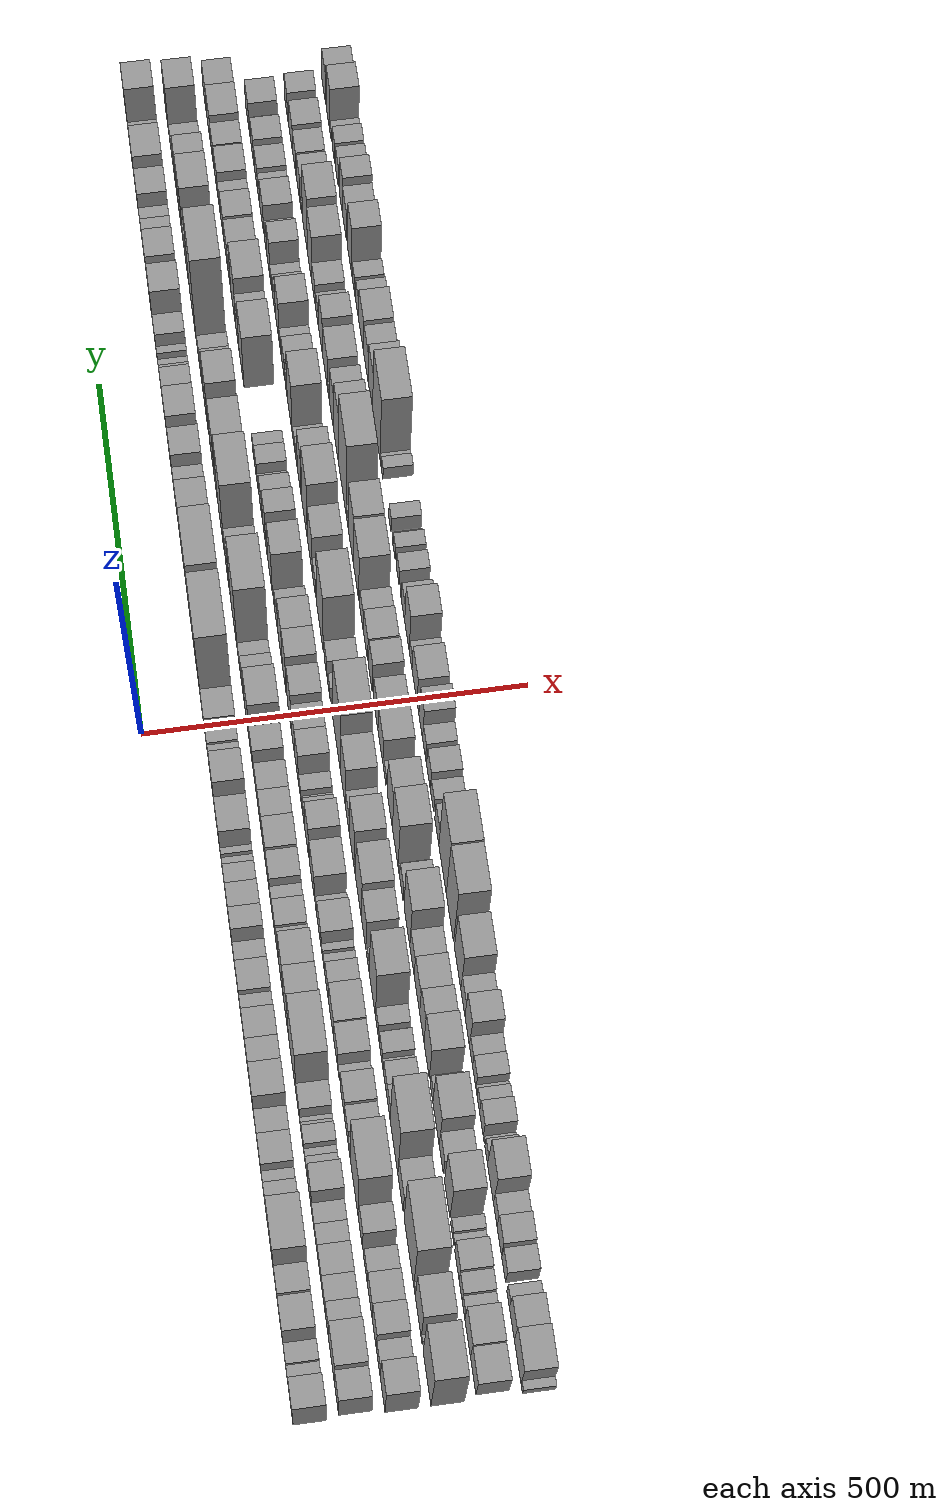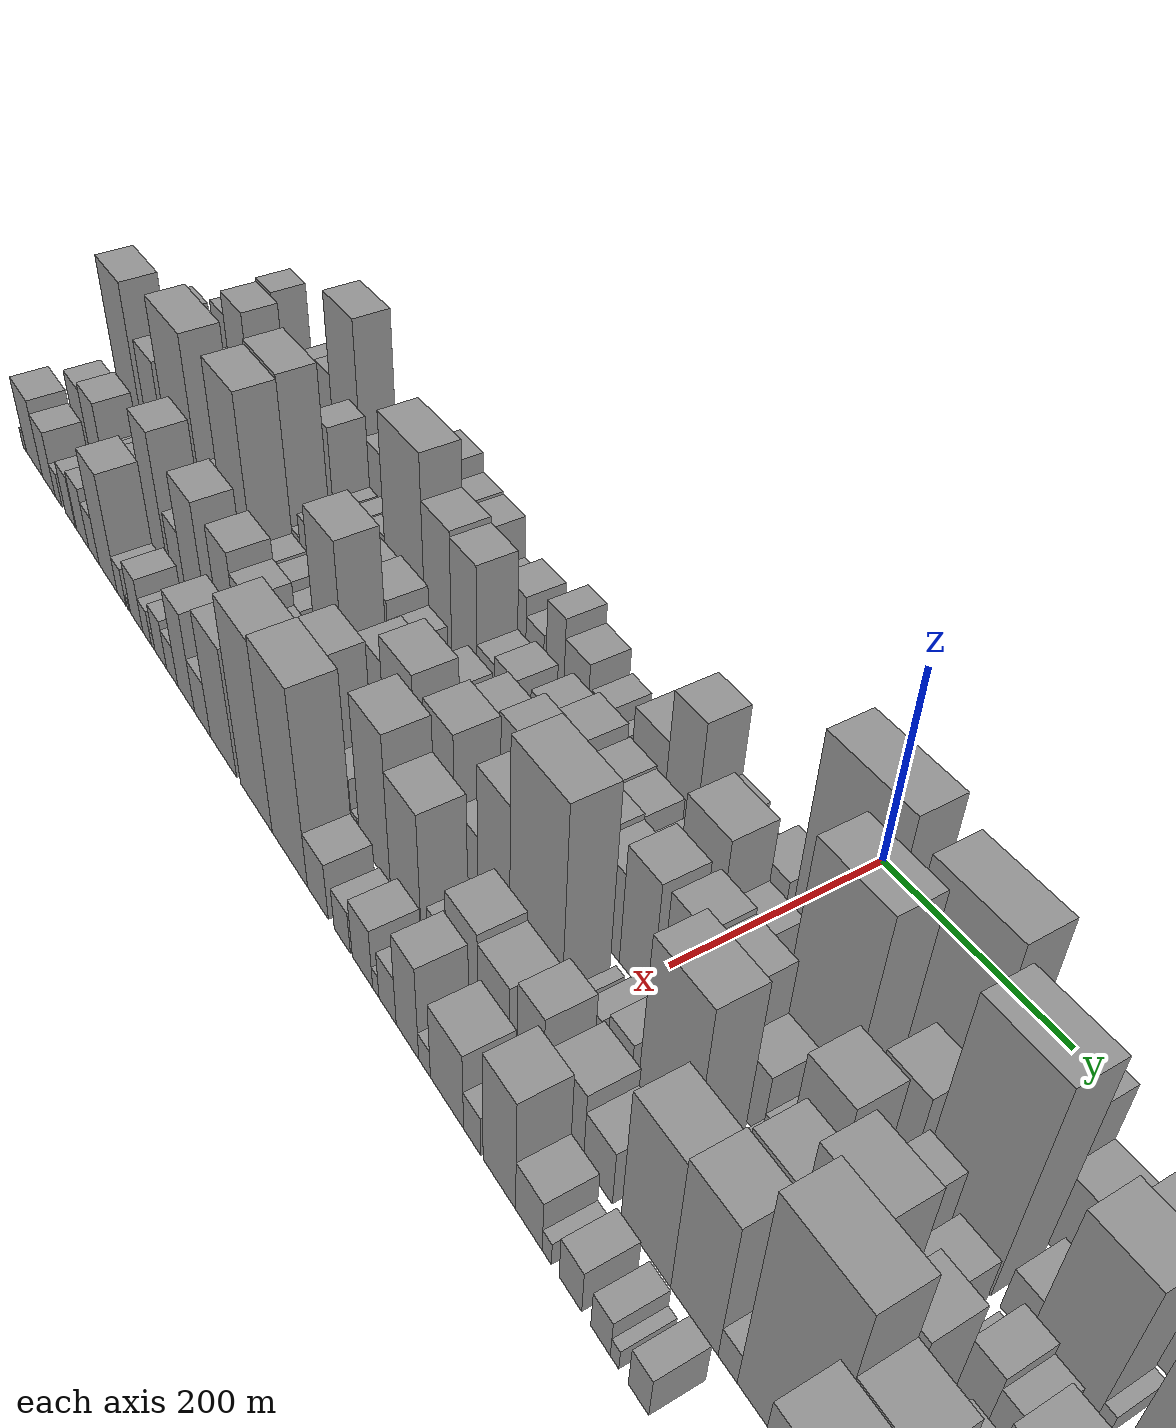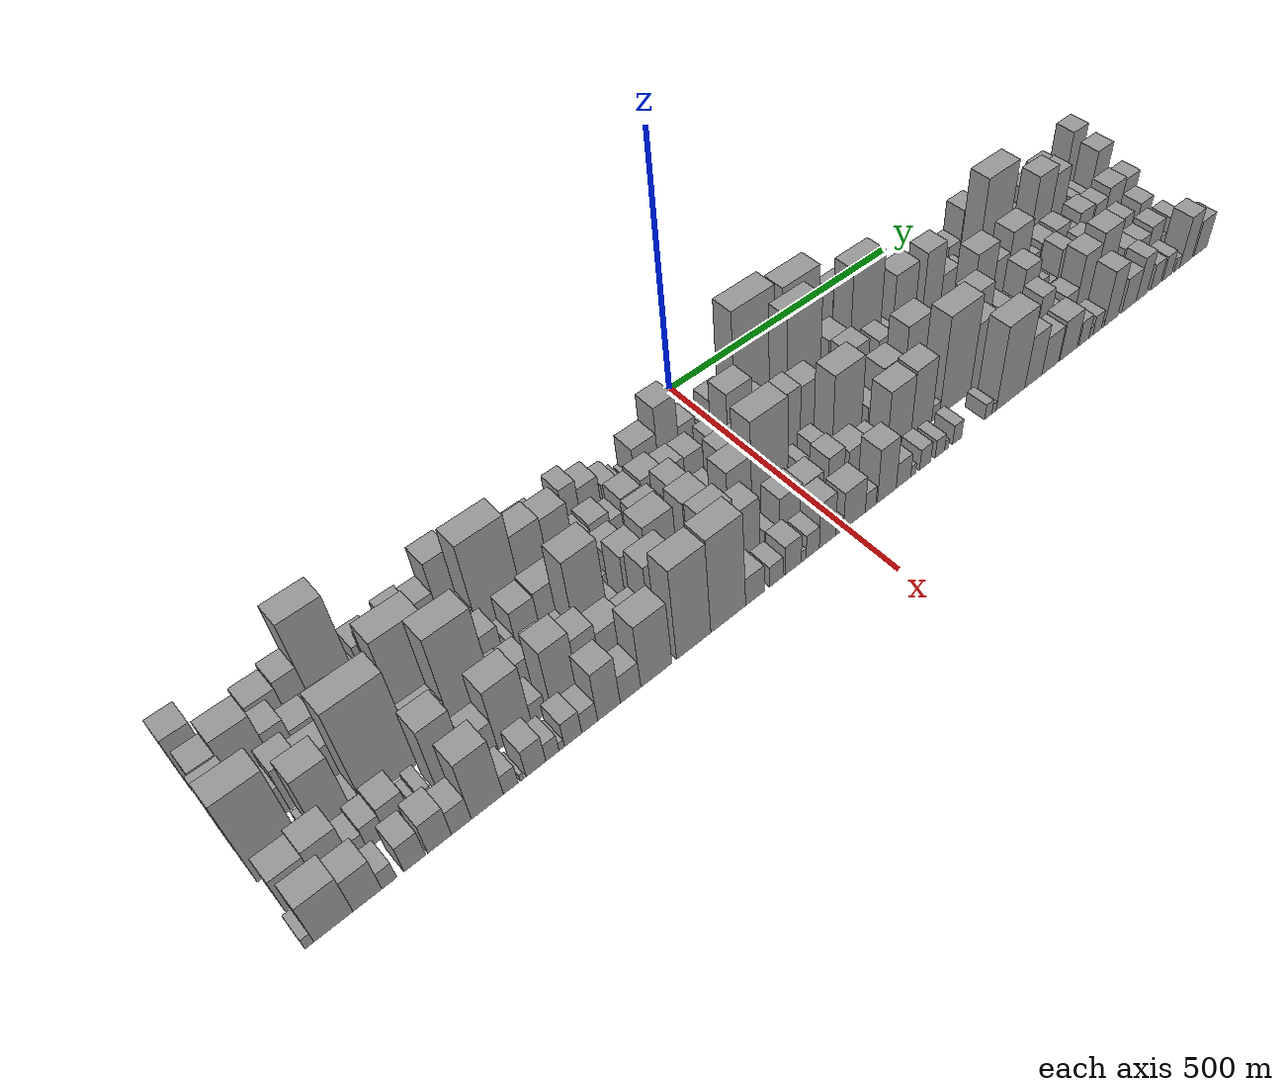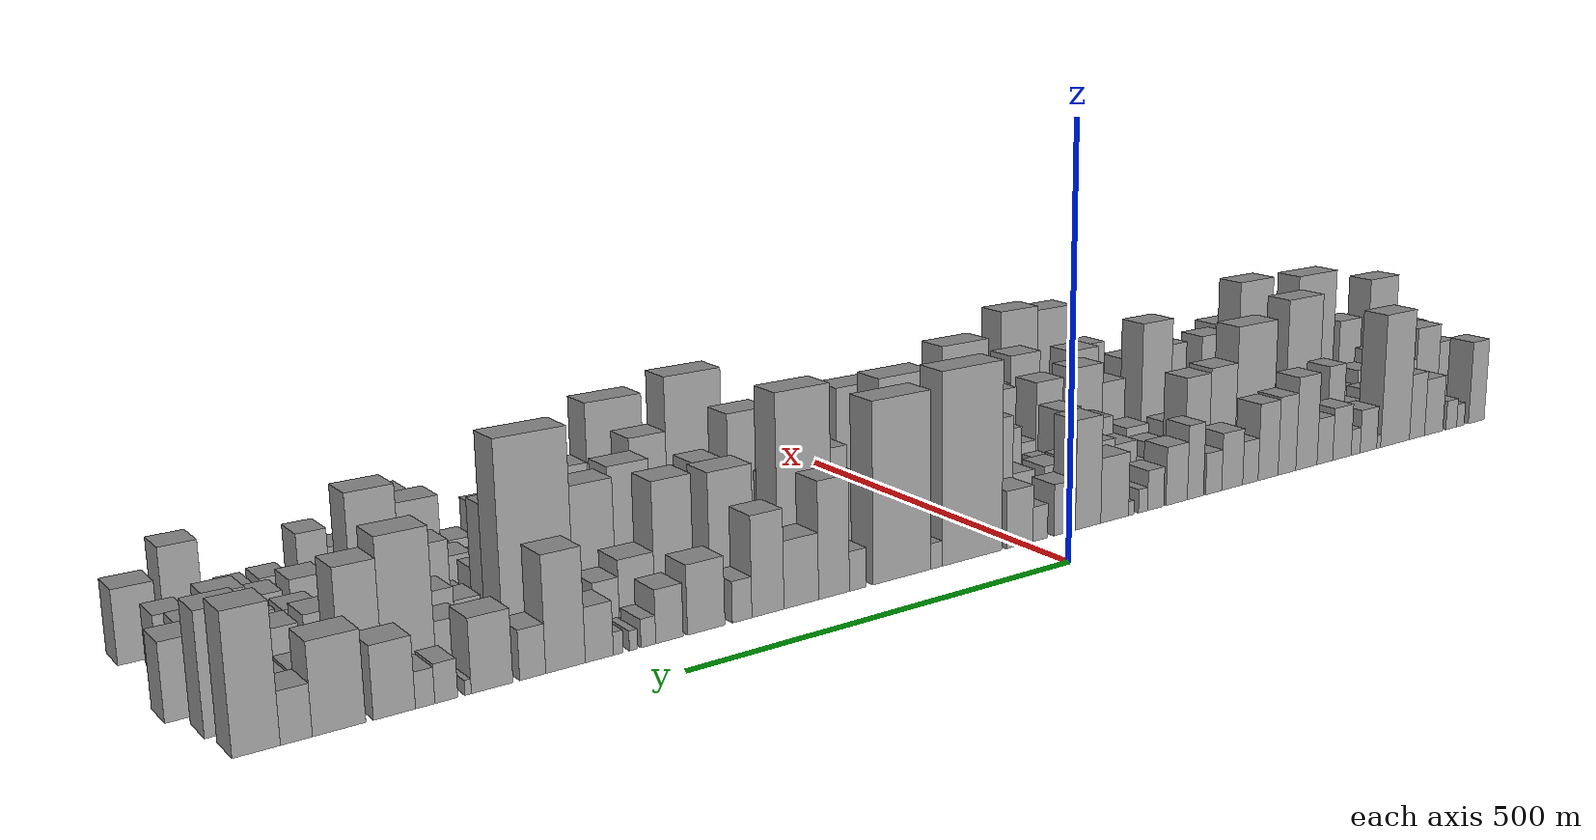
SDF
<sdf version="1.6">
 <world name="default">
  <scene>
   <sky><clouds><speed>12</speed></clouds></sky>
   <ambient>0.4 0.4 0.4 1</ambient>
   <background>0.7 0.7 0.7 1</background>
   <shadows>1</shadows>
  </scene>
  <gravity>0 0 -9.8066</gravity>
  <magnetic_field>6e-06 2.3e-05 -4.2e-05</magnetic_field>
  <physics default="0" name="default_physics" type="ode">
   <ode>
    <solver>
     <type>quick</type>
     <iters>10</iters>
     <sor>1.0</sor>
     <use_dynamic_moi_rescaling>0</use_dynamic_moi_rescaling>
    </solver>
    <constraints>
     <cfm>0</cfm>
     <erp>0.2</erp>
     <contact_max_correcting_vel>100</contact_max_correcting_vel>
     <contact_surface_layer>0.001</contact_surface_layer>
    </constraints>
   </ode>
   <max_step_size>0.004</max_step_size>
   <real_time_factor>1</real_time_factor>
   <real_time_update_rate>250</real_time_update_rate>
  </physics>
  <light name="sun" type="directional">
   <pose>0 0 10 0 0 0</pose>
   <diffuse>0.8 0.8 0.8 1</diffuse>
   <specular>0.2 0.2 0.2 1</specular>
   <attenuation>
    <range>1000</range>
    <constant>0.9</constant>
    <linear>0.01</linear>
    <quadratic>0.001</quadratic>
   </attenuation>
   <direction>-0.5 0.1 -0.9</direction>
  </light>
  <model name="building_1">
   <static>1</static>
   <pose>100.0000 -871.1596 0 0.000000 0.000000 0.000000</pose>
   <link name="link">
    <pose>0 0 60.00 0 0 0</pose>
    <collision name="collision"><geometry><box><size>40.0000 37.6807 120.0000</size></box></geometry></collision>
    <visual name="visual">
     <cast_shadows>0</cast_shadows>
     <geometry><box><size>40.0000 37.6807 120.0000</size></box></geometry>
     <material>
      <script>
       <uri>model://grey_wall/materials/scripts</uri>
       <uri>model://grey_wall/materials/textures</uri>
       <name>vrc/grey_wall</name>
      </script>
     </material>
    </visual>
   </link>
  </model>
  <model name="building_2">
   <static>1</static>
   <pose>100.0000 -833.4585 0 0.000000 0.000000 0.000000</pose>
   <link name="link">
    <pose>0 0 16.50 0 0 0</pose>
    <collision name="collision"><geometry><box><size>40.0000 17.7216 33.0000</size></box></geometry></collision>
    <visual name="visual">
     <cast_shadows>0</cast_shadows>
     <geometry><box><size>40.0000 17.7216 33.0000</size></box></geometry>
     <material>
      <script>
       <uri>model://grey_wall/materials/scripts</uri>
       <uri>model://grey_wall/materials/textures</uri>
       <name>vrc/grey_wall</name>
      </script>
     </material>
    </visual>
   </link>
  </model>
  <model name="building_3">
   <static>1</static>
   <pose>100.0000 -812.0558 0 0.000000 0.000000 0.000000</pose>
   <link name="link">
    <pose>0 0 21.00 0 0 0</pose>
    <collision name="collision"><geometry><box><size>40.0000 25.0839 42.0000</size></box></geometry></collision>
    <visual name="visual">
     <cast_shadows>0</cast_shadows>
     <geometry><box><size>40.0000 25.0839 42.0000</size></box></geometry>
     <material>
      <script>
       <uri>model://grey_wall/materials/scripts</uri>
       <uri>model://grey_wall/materials/textures</uri>
       <name>vrc/grey_wall</name>
      </script>
     </material>
    </visual>
   </link>
  </model>
  <model name="building_4">
   <static>1</static>
   <pose>100.0000 -771.5161 0 0.000000 0.000000 0.000000</pose>
   <link name="link">
    <pose>0 0 40.50 0 0 0</pose>
    <collision name="collision"><geometry><box><size>40.0000 41.9954 81.0000</size></box></geometry></collision>
    <visual name="visual">
     <cast_shadows>0</cast_shadows>
     <geometry><box><size>40.0000 41.9954 81.0000</size></box></geometry>
     <material>
      <script>
       <uri>model://grey_wall/materials/scripts</uri>
       <uri>model://grey_wall/materials/textures</uri>
       <name>vrc/grey_wall</name>
      </script>
     </material>
    </visual>
   </link>
  </model>
  <model name="building_5">
   <static>1</static>
   <pose>100.0000 -733.6429 0 0.000000 0.000000 0.000000</pose>
   <link name="link">
    <pose>0 0 46.50 0 0 0</pose>
    <collision name="collision"><geometry><box><size>40.0000 33.7510 93.0000</size></box></geometry></collision>
    <visual name="visual">
     <cast_shadows>0</cast_shadows>
     <geometry><box><size>40.0000 33.7510 93.0000</size></box></geometry>
     <material>
      <script>
       <uri>model://grey_wall/materials/scripts</uri>
       <uri>model://grey_wall/materials/textures</uri>
       <name>vrc/grey_wall</name>
      </script>
     </material>
    </visual>
   </link>
  </model>
  <model name="building_6">
   <static>1</static>
   <pose>100.0000 -685.0312 0 0.000000 0.000000 0.000000</pose>
   <link name="link">
    <pose>0 0 93.00 0 0 0</pose>
    <collision name="collision"><geometry><box><size>40.0000 63.4724 186.0000</size></box></geometry></collision>
    <visual name="visual">
     <cast_shadows>0</cast_shadows>
     <geometry><box><size>40.0000 63.4724 186.0000</size></box></geometry>
     <material>
      <script>
       <uri>model://grey_wall/materials/scripts</uri>
       <uri>model://grey_wall/materials/textures</uri>
       <name>vrc/grey_wall</name>
      </script>
     </material>
    </visual>
   </link>
  </model>
  <model name="building_7">
   <static>1</static>
   <pose>100.0000 -649.1838 0 0.000000 0.000000 0.000000</pose>
   <link name="link">
    <pose>0 0 9.00 0 0 0</pose>
    <collision name="collision"><geometry><box><size>40.0000 8.2226 18.0000</size></box></geometry></collision>
    <visual name="visual">
     <cast_shadows>0</cast_shadows>
     <geometry><box><size>40.0000 8.2226 18.0000</size></box></geometry>
     <material>
      <script>
       <uri>model://grey_wall/materials/scripts</uri>
       <uri>model://grey_wall/materials/textures</uri>
       <name>vrc/grey_wall</name>
      </script>
     </material>
    </visual>
   </link>
  </model>
  <model name="building_8">
   <static>1</static>
   <pose>100.0000 -627.2576 0 0.000000 0.000000 0.000000</pose>
   <link name="link">
    <pose>0 0 30.00 0 0 0</pose>
    <collision name="collision"><geometry><box><size>40.0000 35.6298 60.0000</size></box></geometry></collision>
    <visual name="visual">
     <cast_shadows>0</cast_shadows>
     <geometry><box><size>40.0000 35.6298 60.0000</size></box></geometry>
     <material>
      <script>
       <uri>model://grey_wall/materials/scripts</uri>
       <uri>model://grey_wall/materials/textures</uri>
       <name>vrc/grey_wall</name>
      </script>
     </material>
    </visual>
   </link>
  </model>
  <model name="building_9">
   <static>1</static>
   <pose>100.0000 -600.0099 0 0.000000 0.000000 0.000000</pose>
   <link name="link">
    <pose>0 0 18.00 0 0 0</pose>
    <collision name="collision"><geometry><box><size>40.0000 18.8656 36.0000</size></box></geometry></collision>
    <visual name="visual">
     <cast_shadows>0</cast_shadows>
     <geometry><box><size>40.0000 18.8656 36.0000</size></box></geometry>
     <material>
      <script>
       <uri>model://grey_wall/materials/scripts</uri>
       <uri>model://grey_wall/materials/textures</uri>
       <name>vrc/grey_wall</name>
      </script>
     </material>
    </visual>
   </link>
  </model>
  <model name="building_10">
   <static>1</static>
   <pose>100.0000 -571.3462 0 0.000000 0.000000 0.000000</pose>
   <link name="link">
    <pose>0 0 36.00 0 0 0</pose>
    <collision name="collision"><geometry><box><size>40.0000 38.4618 72.0000</size></box></geometry></collision>
    <visual name="visual">
     <cast_shadows>0</cast_shadows>
     <geometry><box><size>40.0000 38.4618 72.0000</size></box></geometry>
     <material>
      <script>
       <uri>model://grey_wall/materials/scripts</uri>
       <uri>model://grey_wall/materials/textures</uri>
       <name>vrc/grey_wall</name>
      </script>
     </material>
    </visual>
   </link>
  </model>
  <model name="building_11">
   <static>1</static>
   <pose>100.0000 -536.1605 0 0.000000 0.000000 0.000000</pose>
   <link name="link">
    <pose>0 0 31.50 0 0 0</pose>
    <collision name="collision"><geometry><box><size>40.0000 31.9096 63.0000</size></box></geometry></collision>
    <visual name="visual">
     <cast_shadows>0</cast_shadows>
     <geometry><box><size>40.0000 31.9096 63.0000</size></box></geometry>
     <material>
      <script>
       <uri>model://grey_wall/materials/scripts</uri>
       <uri>model://grey_wall/materials/textures</uri>
       <name>vrc/grey_wall</name>
      </script>
     </material>
    </visual>
   </link>
  </model>
  <model name="building_12">
   <static>1</static>
   <pose>100.0000 -498.8971 0 0.000000 0.000000 0.000000</pose>
   <link name="link">
    <pose>0 0 63.00 0 0 0</pose>
    <collision name="collision"><geometry><box><size>40.0000 42.6172 126.0000</size></box></geometry></collision>
    <visual name="visual">
     <cast_shadows>0</cast_shadows>
     <geometry><box><size>40.0000 42.6172 126.0000</size></box></geometry>
     <material>
      <script>
       <uri>model://grey_wall/materials/scripts</uri>
       <uri>model://grey_wall/materials/textures</uri>
       <name>vrc/grey_wall</name>
      </script>
     </material>
    </visual>
   </link>
  </model>
  <model name="building_13">
   <static>1</static>
   <pose>100.0000 -460.0980 0 0.000000 0.000000 0.000000</pose>
   <link name="link">
    <pose>0 0 52.50 0 0 0</pose>
    <collision name="collision"><geometry><box><size>40.0000 34.9809 105.0000</size></box></geometry></collision>
    <visual name="visual">
     <cast_shadows>0</cast_shadows>
     <geometry><box><size>40.0000 34.9809 105.0000</size></box></geometry>
     <material>
      <script>
       <uri>model://grey_wall/materials/scripts</uri>
       <uri>model://grey_wall/materials/textures</uri>
       <name>vrc/grey_wall</name>
      </script>
     </material>
    </visual>
   </link>
  </model>
  <model name="building_14">
   <static>1</static>
   <pose>100.0000 -423.3521 0 0.000000 0.000000 0.000000</pose>
   <link name="link">
    <pose>0 0 51.00 0 0 0</pose>
    <collision name="collision"><geometry><box><size>40.0000 38.5110 102.0000</size></box></geometry></collision>
    <visual name="visual">
     <cast_shadows>0</cast_shadows>
     <geometry><box><size>40.0000 38.5110 102.0000</size></box></geometry>
     <material>
      <script>
       <uri>model://grey_wall/materials/scripts</uri>
       <uri>model://grey_wall/materials/textures</uri>
       <name>vrc/grey_wall</name>
      </script>
     </material>
    </visual>
   </link>
  </model>
  <model name="building_15">
   <static>1</static>
   <pose>100.0000 -389.4801 0 0.000000 0.000000 0.000000</pose>
   <link name="link">
    <pose>0 0 28.50 0 0 0</pose>
    <collision name="collision"><geometry><box><size>40.0000 29.2329 57.0000</size></box></geometry></collision>
    <visual name="visual">
     <cast_shadows>0</cast_shadows>
     <geometry><box><size>40.0000 29.2329 57.0000</size></box></geometry>
     <material>
      <script>
       <uri>model://grey_wall/materials/scripts</uri>
       <uri>model://grey_wall/materials/textures</uri>
       <name>vrc/grey_wall</name>
      </script>
     </material>
    </visual>
   </link>
  </model>
  <model name="building_16">
   <static>1</static>
   <pose>100.0000 -355.2615 0 0.000000 0.000000 0.000000</pose>
   <link name="link">
    <pose>0 0 37.50 0 0 0</pose>
    <collision name="collision"><geometry><box><size>40.0000 39.2045 75.0000</size></box></geometry></collision>
    <visual name="visual">
     <cast_shadows>0</cast_shadows>
     <geometry><box><size>40.0000 39.2045 75.0000</size></box></geometry>
     <material>
      <script>
       <uri>model://grey_wall/materials/scripts</uri>
       <uri>model://grey_wall/materials/textures</uri>
       <name>vrc/grey_wall</name>
      </script>
     </material>
    </visual>
   </link>
  </model>
  <model name="building_17">
   <static>1</static>
   <pose>100.0000 -320.9686 0 0.000000 0.000000 0.000000</pose>
   <link name="link">
    <pose>0 0 27.00 0 0 0</pose>
    <collision name="collision"><geometry><box><size>40.0000 29.3813 54.0000</size></box></geometry></collision>
    <visual name="visual">
     <cast_shadows>0</cast_shadows>
     <geometry><box><size>40.0000 29.3813 54.0000</size></box></geometry>
     <material>
      <script>
       <uri>model://grey_wall/materials/scripts</uri>
       <uri>model://grey_wall/materials/textures</uri>
       <name>vrc/grey_wall</name>
      </script>
     </material>
    </visual>
   </link>
  </model>
  <model name="building_18">
   <static>1</static>
   <pose>100.0000 -287.8208 0 0.000000 0.000000 0.000000</pose>
   <link name="link">
    <pose>0 0 48.00 0 0 0</pose>
    <collision name="collision"><geometry><box><size>40.0000 28.9144 96.0000</size></box></geometry></collision>
    <visual name="visual">
     <cast_shadows>0</cast_shadows>
     <geometry><box><size>40.0000 28.9144 96.0000</size></box></geometry>
     <material>
      <script>
       <uri>model://grey_wall/materials/scripts</uri>
       <uri>model://grey_wall/materials/textures</uri>
       <name>vrc/grey_wall</name>
      </script>
     </material>
    </visual>
   </link>
  </model>
  <model name="building_19">
   <static>1</static>
   <pose>100.0000 -254.4728 0 0.000000 0.000000 0.000000</pose>
   <link name="link">
    <pose>0 0 37.50 0 0 0</pose>
    <collision name="collision"><geometry><box><size>40.0000 37.7816 75.0000</size></box></geometry></collision>
    <visual name="visual">
     <cast_shadows>0</cast_shadows>
     <geometry><box><size>40.0000 37.7816 75.0000</size></box></geometry>
     <material>
      <script>
       <uri>model://grey_wall/materials/scripts</uri>
       <uri>model://grey_wall/materials/textures</uri>
       <name>vrc/grey_wall</name>
      </script>
     </material>
    </visual>
   </link>
  </model>
  <model name="building_20">
   <static>1</static>
   <pose>100.0000 -217.5189 0 0.000000 0.000000 0.000000</pose>
   <link name="link">
    <pose>0 0 25.50 0 0 0</pose>
    <collision name="collision"><geometry><box><size>40.0000 28.1261 51.0000</size></box></geometry></collision>
    <visual name="visual">
     <cast_shadows>0</cast_shadows>
     <geometry><box><size>40.0000 28.1261 51.0000</size></box></geometry>
     <material>
      <script>
       <uri>model://grey_wall/materials/scripts</uri>
       <uri>model://grey_wall/materials/textures</uri>
       <name>vrc/grey_wall</name>
      </script>
     </material>
    </visual>
   </link>
  </model>
  <model name="building_21">
   <static>1</static>
   <pose>100.0000 -195.7694 0 0.000000 0.000000 0.000000</pose>
   <link name="link">
    <pose>0 0 15.00 0 0 0</pose>
    <collision name="collision"><geometry><box><size>40.0000 15.3728 30.0000</size></box></geometry></collision>
    <visual name="visual">
     <cast_shadows>0</cast_shadows>
     <geometry><box><size>40.0000 15.3728 30.0000</size></box></geometry>
     <material>
      <script>
       <uri>model://grey_wall/materials/scripts</uri>
       <uri>model://grey_wall/materials/textures</uri>
       <name>vrc/grey_wall</name>
      </script>
     </material>
    </visual>
   </link>
  </model>
  <model name="building_22">
   <static>1</static>
   <pose>100.0000 -175.6057 0 0.000000 0.000000 0.000000</pose>
   <link name="link">
    <pose>0 0 9.00 0 0 0</pose>
    <collision name="collision"><geometry><box><size>40.0000 8.9547 18.0000</size></box></geometry></collision>
    <visual name="visual">
     <cast_shadows>0</cast_shadows>
     <geometry><box><size>40.0000 8.9547 18.0000</size></box></geometry>
     <material>
      <script>
       <uri>model://grey_wall/materials/scripts</uri>
       <uri>model://grey_wall/materials/textures</uri>
       <name>vrc/grey_wall</name>
      </script>
     </material>
    </visual>
   </link>
  </model>
  <model name="building_23">
   <static>1</static>
   <pose>100.0000 -147.9106 0 0.000000 0.000000 0.000000</pose>
   <link name="link">
    <pose>0 0 40.50 0 0 0</pose>
    <collision name="collision"><geometry><box><size>40.0000 46.4355 81.0000</size></box></geometry></collision>
    <visual name="visual">
     <cast_shadows>0</cast_shadows>
     <geometry><box><size>40.0000 46.4355 81.0000</size></box></geometry>
     <material>
      <script>
       <uri>model://grey_wall/materials/scripts</uri>
       <uri>model://grey_wall/materials/textures</uri>
       <name>vrc/grey_wall</name>
      </script>
     </material>
    </visual>
   </link>
  </model>
  <model name="building_24">
   <static>1</static>
   <pose>100.0000 -103.9873 0 0.000000 0.000000 0.000000</pose>
   <link name="link">
    <pose>0 0 67.50 0 0 0</pose>
    <collision name="collision"><geometry><box><size>40.0000 41.4111 135.0000</size></box></geometry></collision>
    <visual name="visual">
     <cast_shadows>0</cast_shadows>
     <geometry><box><size>40.0000 41.4111 135.0000</size></box></geometry>
     <material>
      <script>
       <uri>model://grey_wall/materials/scripts</uri>
       <uri>model://grey_wall/materials/textures</uri>
       <name>vrc/grey_wall</name>
      </script>
     </material>
    </visual>
   </link>
  </model>
  <model name="building_25">
   <static>1</static>
   <pose>100.0000 -66.1264 0 0.000000 0.000000 0.000000</pose>
   <link name="link">
    <pose>0 0 31.50 0 0 0</pose>
    <collision name="collision"><geometry><box><size>40.0000 34.3106 63.0000</size></box></geometry></collision>
    <visual name="visual">
     <cast_shadows>0</cast_shadows>
     <geometry><box><size>40.0000 34.3106 63.0000</size></box></geometry>
     <material>
      <script>
       <uri>model://grey_wall/materials/scripts</uri>
       <uri>model://grey_wall/materials/textures</uri>
       <name>vrc/grey_wall</name>
      </script>
     </material>
    </visual>
   </link>
  </model>
  <model name="building_26">
   <static>1</static>
   <pose>100.0000 -27.5412 0 0.000000 0.000000 0.000000</pose>
   <link name="link">
    <pose>0 0 21.00 0 0 0</pose>
    <collision name="collision"><geometry><box><size>40.0000 22.8598 42.0000</size></box></geometry></collision>
    <visual name="visual">
     <cast_shadows>0</cast_shadows>
     <geometry><box><size>40.0000 22.8598 42.0000</size></box></geometry>
     <material>
      <script>
       <uri>model://grey_wall/materials/scripts</uri>
       <uri>model://grey_wall/materials/textures</uri>
       <name>vrc/grey_wall</name>
      </script>
     </material>
    </visual>
   </link>
  </model>
  <model name="building_27">
   <static>1</static>
   <pose>100.0000 4.2147 0 0.000000 0.000000 0.000000</pose>
   <link name="link">
    <pose>0 0 34.50 0 0 0</pose>
    <collision name="collision"><geometry><box><size>40.0000 40.6521 69.0000</size></box></geometry></collision>
    <visual name="visual">
     <cast_shadows>0</cast_shadows>
     <geometry><box><size>40.0000 40.6521 69.0000</size></box></geometry>
     <material>
      <script>
       <uri>model://grey_wall/materials/scripts</uri>
       <uri>model://grey_wall/materials/textures</uri>
       <name>vrc/grey_wall</name>
      </script>
     </material>
    </visual>
   </link>
  </model>
  <model name="building_28">
   <static>1</static>
   <pose>100.0000 75.6349 0 0.000000 0.000000 0.000000</pose>
   <link name="link">
    <pose>0 0 112.50 0 0 0</pose>
    <collision name="collision"><geometry><box><size>40.0000 88.1882 225.0000</size></box></geometry></collision>
    <visual name="visual">
     <cast_shadows>0</cast_shadows>
     <geometry><box><size>40.0000 88.1882 225.0000</size></box></geometry>
     <material>
      <script>
       <uri>model://grey_wall/materials/scripts</uri>
       <uri>model://grey_wall/materials/textures</uri>
       <name>vrc/grey_wall</name>
      </script>
     </material>
    </visual>
   </link>
  </model>
  <model name="building_29">
   <static>1</static>
   <pose>100.0000 127.7942 0 0.000000 0.000000 0.000000</pose>
   <link name="link">
    <pose>0 0 15.00 0 0 0</pose>
    <collision name="collision"><geometry><box><size>40.0000 16.1303 30.0000</size></box></geometry></collision>
    <visual name="visual">
     <cast_shadows>0</cast_shadows>
     <geometry><box><size>40.0000 16.1303 30.0000</size></box></geometry>
     <material>
      <script>
       <uri>model://grey_wall/materials/scripts</uri>
       <uri>model://grey_wall/materials/textures</uri>
       <name>vrc/grey_wall</name>
      </script>
     </material>
    </visual>
   </link>
  </model>
  <model name="building_30">
   <static>1</static>
   <pose>100.0000 175.9468 0 0.000000 0.000000 0.000000</pose>
   <link name="link">
    <pose>0 0 103.50 0 0 0</pose>
    <collision name="collision"><geometry><box><size>40.0000 80.1750 207.0000</size></box></geometry></collision>
    <visual name="visual">
     <cast_shadows>0</cast_shadows>
     <geometry><box><size>40.0000 80.1750 207.0000</size></box></geometry>
     <material>
      <script>
       <uri>model://grey_wall/materials/scripts</uri>
       <uri>model://grey_wall/materials/textures</uri>
       <name>vrc/grey_wall</name>
      </script>
     </material>
    </visual>
   </link>
  </model>
  <model name="building_31">
   <static>1</static>
   <pose>100.0000 236.4385 0 0.000000 0.000000 0.000000</pose>
   <link name="link">
    <pose>0 0 22.50 0 0 0</pose>
    <collision name="collision"><geometry><box><size>40.0000 22.8084 45.0000</size></box></geometry></collision>
    <visual name="visual">
     <cast_shadows>0</cast_shadows>
     <geometry><box><size>40.0000 22.8084 45.0000</size></box></geometry>
     <material>
      <script>
       <uri>model://grey_wall/materials/scripts</uri>
       <uri>model://grey_wall/materials/textures</uri>
       <name>vrc/grey_wall</name>
      </script>
     </material>
    </visual>
   </link>
  </model>
  <model name="building_32">
   <static>1</static>
   <pose>100.0000 268.0821 0 0.000000 0.000000 0.000000</pose>
   <link name="link">
    <pose>0 0 66.00 0 0 0</pose>
    <collision name="collision"><geometry><box><size>40.0000 40.4787 132.0000</size></box></geometry></collision>
    <visual name="visual">
     <cast_shadows>0</cast_shadows>
     <geometry><box><size>40.0000 40.4787 132.0000</size></box></geometry>
     <material>
      <script>
       <uri>model://grey_wall/materials/scripts</uri>
       <uri>model://grey_wall/materials/textures</uri>
       <name>vrc/grey_wall</name>
      </script>
     </material>
    </visual>
   </link>
  </model>
  <model name="building_33">
   <static>1</static>
   <pose>100.0000 310.4709 0 0.000000 0.000000 0.000000</pose>
   <link name="link">
    <pose>0 0 37.50 0 0 0</pose>
    <collision name="collision"><geometry><box><size>40.0000 44.2989 75.0000</size></box></geometry></collision>
    <visual name="visual">
     <cast_shadows>0</cast_shadows>
     <geometry><box><size>40.0000 44.2989 75.0000</size></box></geometry>
     <material>
      <script>
       <uri>model://grey_wall/materials/scripts</uri>
       <uri>model://grey_wall/materials/textures</uri>
       <name>vrc/grey_wall</name>
      </script>
     </material>
    </visual>
   </link>
  </model>
  <model name="building_34">
   <static>1</static>
   <pose>100.0000 352.6324 0 0.000000 0.000000 0.000000</pose>
   <link name="link">
    <pose>0 0 55.50 0 0 0</pose>
    <collision name="collision"><geometry><box><size>40.0000 40.0242 111.0000</size></box></geometry></collision>
    <visual name="visual">
     <cast_shadows>0</cast_shadows>
     <geometry><box><size>40.0000 40.0242 111.0000</size></box></geometry>
     <material>
      <script>
       <uri>model://grey_wall/materials/scripts</uri>
       <uri>model://grey_wall/materials/textures</uri>
       <name>vrc/grey_wall</name>
      </script>
     </material>
    </visual>
   </link>
  </model>
  <model name="building_35">
   <static>1</static>
   <pose>100.0000 384.6178 0 0.000000 0.000000 0.000000</pose>
   <link name="link">
    <pose>0 0 22.50 0 0 0</pose>
    <collision name="collision"><geometry><box><size>40.0000 23.9466 45.0000</size></box></geometry></collision>
    <visual name="visual">
     <cast_shadows>0</cast_shadows>
     <geometry><box><size>40.0000 23.9466 45.0000</size></box></geometry>
     <material>
      <script>
       <uri>model://grey_wall/materials/scripts</uri>
       <uri>model://grey_wall/materials/textures</uri>
       <name>vrc/grey_wall</name>
      </script>
     </material>
    </visual>
   </link>
  </model>
  <model name="building_36">
   <static>1</static>
   <pose>100.0000 427.8317 0 0.000000 0.000000 0.000000</pose>
   <link name="link">
    <pose>0 0 37.50 0 0 0</pose>
    <collision name="collision"><geometry><box><size>40.0000 44.4813 75.0000</size></box></geometry></collision>
    <visual name="visual">
     <cast_shadows>0</cast_shadows>
     <geometry><box><size>40.0000 44.4813 75.0000</size></box></geometry>
     <material>
      <script>
       <uri>model://grey_wall/materials/scripts</uri>
       <uri>model://grey_wall/materials/textures</uri>
       <name>vrc/grey_wall</name>
      </script>
     </material>
    </visual>
   </link>
  </model>
  <model name="building_37">
   <static>1</static>
   <pose>100.0000 470.9186 0 0.000000 0.000000 0.000000</pose>
   <link name="link">
    <pose>0 0 28.50 0 0 0</pose>
    <collision name="collision"><geometry><box><size>40.0000 31.6924 57.0000</size></box></geometry></collision>
    <visual name="visual">
     <cast_shadows>0</cast_shadows>
     <geometry><box><size>40.0000 31.6924 57.0000</size></box></geometry>
     <material>
      <script>
       <uri>model://grey_wall/materials/scripts</uri>
       <uri>model://grey_wall/materials/textures</uri>
       <name>vrc/grey_wall</name>
      </script>
     </material>
    </visual>
   </link>
  </model>
  <model name="building_38">
   <static>1</static>
   <pose>100.0000 495.1675 0 0.000000 0.000000 0.000000</pose>
   <link name="link">
    <pose>0 0 15.00 0 0 0</pose>
    <collision name="collision"><geometry><box><size>40.0000 16.8054 30.0000</size></box></geometry></collision>
    <visual name="visual">
     <cast_shadows>0</cast_shadows>
     <geometry><box><size>40.0000 16.8054 30.0000</size></box></geometry>
     <material>
      <script>
       <uri>model://grey_wall/materials/scripts</uri>
       <uri>model://grey_wall/materials/textures</uri>
       <name>vrc/grey_wall</name>
      </script>
     </material>
    </visual>
   </link>
  </model>
  <model name="building_39">
   <static>1</static>
   <pose>100.0000 512.1227 0 0.000000 0.000000 0.000000</pose>
   <link name="link">
    <pose>0 0 10.50 0 0 0</pose>
    <collision name="collision"><geometry><box><size>40.0000 9.1050 21.0000</size></box></geometry></collision>
    <visual name="visual">
     <cast_shadows>0</cast_shadows>
     <geometry><box><size>40.0000 9.1050 21.0000</size></box></geometry>
     <material>
      <script>
       <uri>model://grey_wall/materials/scripts</uri>
       <uri>model://grey_wall/materials/textures</uri>
       <name>vrc/grey_wall</name>
      </script>
     </material>
    </visual>
   </link>
  </model>
  <model name="building_40">
   <static>1</static>
   <pose>100.0000 529.0819 0 0.000000 0.000000 0.000000</pose>
   <link name="link">
    <pose>0 0 12.00 0 0 0</pose>
    <collision name="collision"><geometry><box><size>40.0000 10.8135 24.0000</size></box></geometry></collision>
    <visual name="visual">
     <cast_shadows>0</cast_shadows>
     <geometry><box><size>40.0000 10.8135 24.0000</size></box></geometry>
     <material>
      <script>
       <uri>model://grey_wall/materials/scripts</uri>
       <uri>model://grey_wall/materials/textures</uri>
       <name>vrc/grey_wall</name>
      </script>
     </material>
    </visual>
   </link>
  </model>
  <model name="building_41">
   <static>1</static>
   <pose>100.0000 549.8728 0 0.000000 0.000000 0.000000</pose>
   <link name="link">
    <pose>0 0 28.50 0 0 0</pose>
    <collision name="collision"><geometry><box><size>40.0000 30.7684 57.0000</size></box></geometry></collision>
    <visual name="visual">
     <cast_shadows>0</cast_shadows>
     <geometry><box><size>40.0000 30.7684 57.0000</size></box></geometry>
     <material>
      <script>
       <uri>model://grey_wall/materials/scripts</uri>
       <uri>model://grey_wall/materials/textures</uri>
       <name>vrc/grey_wall</name>
      </script>
     </material>
    </visual>
   </link>
  </model>
  <model name="building_42">
   <static>1</static>
   <pose>100.0000 586.4591 0 0.000000 0.000000 0.000000</pose>
   <link name="link">
    <pose>0 0 60.00 0 0 0</pose>
    <collision name="collision"><geometry><box><size>40.0000 42.4041 120.0000</size></box></geometry></collision>
    <visual name="visual">
     <cast_shadows>0</cast_shadows>
     <geometry><box><size>40.0000 42.4041 120.0000</size></box></geometry>
     <material>
      <script>
       <uri>model://grey_wall/materials/scripts</uri>
       <uri>model://grey_wall/materials/textures</uri>
       <name>vrc/grey_wall</name>
      </script>
     </material>
    </visual>
   </link>
  </model>
  <model name="building_43">
   <static>1</static>
   <pose>100.0000 621.3131 0 0.000000 0.000000 0.000000</pose>
   <link name="link">
    <pose>0 0 25.50 0 0 0</pose>
    <collision name="collision"><geometry><box><size>40.0000 27.3041 51.0000</size></box></geometry></collision>
    <visual name="visual">
     <cast_shadows>0</cast_shadows>
     <geometry><box><size>40.0000 27.3041 51.0000</size></box></geometry>
     <material>
      <script>
       <uri>model://grey_wall/materials/scripts</uri>
       <uri>model://grey_wall/materials/textures</uri>
       <name>vrc/grey_wall</name>
      </script>
     </material>
    </visual>
   </link>
  </model>
  <model name="building_44">
   <static>1</static>
   <pose>100.0000 663.0718 0 0.000000 0.000000 0.000000</pose>
   <link name="link">
    <pose>0 0 37.50 0 0 0</pose>
    <collision name="collision"><geometry><box><size>40.0000 42.2133 75.0000</size></box></geometry></collision>
    <visual name="visual">
     <cast_shadows>0</cast_shadows>
     <geometry><box><size>40.0000 42.2133 75.0000</size></box></geometry>
     <material>
      <script>
       <uri>model://grey_wall/materials/scripts</uri>
       <uri>model://grey_wall/materials/textures</uri>
       <name>vrc/grey_wall</name>
      </script>
     </material>
    </visual>
   </link>
  </model>
  <model name="building_45">
   <static>1</static>
   <pose>100.0000 687.4106 0 0.000000 0.000000 0.000000</pose>
   <link name="link">
    <pose>0 0 7.50 0 0 0</pose>
    <collision name="collision"><geometry><box><size>40.0000 6.4641 15.0000</size></box></geometry></collision>
    <visual name="visual">
     <cast_shadows>0</cast_shadows>
     <geometry><box><size>40.0000 6.4641 15.0000</size></box></geometry>
     <material>
      <script>
       <uri>model://grey_wall/materials/scripts</uri>
       <uri>model://grey_wall/materials/textures</uri>
       <name>vrc/grey_wall</name>
      </script>
     </material>
    </visual>
   </link>
  </model>
  <model name="building_46">
   <static>1</static>
   <pose>100.0000 708.9300 0 0.000000 0.000000 0.000000</pose>
   <link name="link">
    <pose>0 0 19.50 0 0 0</pose>
    <collision name="collision"><geometry><box><size>40.0000 22.5746 39.0000</size></box></geometry></collision>
    <visual name="visual">
     <cast_shadows>0</cast_shadows>
     <geometry><box><size>40.0000 22.5746 39.0000</size></box></geometry>
     <material>
      <script>
       <uri>model://grey_wall/materials/scripts</uri>
       <uri>model://grey_wall/materials/textures</uri>
       <name>vrc/grey_wall</name>
      </script>
     </material>
    </visual>
   </link>
  </model>
  <model name="building_47">
   <static>1</static>
   <pose>100.0000 729.6130 0 0.000000 0.000000 0.000000</pose>
   <link name="link">
    <pose>0 0 18.00 0 0 0</pose>
    <collision name="collision"><geometry><box><size>40.0000 18.7915 36.0000</size></box></geometry></collision>
    <visual name="visual">
     <cast_shadows>0</cast_shadows>
     <geometry><box><size>40.0000 18.7915 36.0000</size></box></geometry>
     <material>
      <script>
       <uri>model://grey_wall/materials/scripts</uri>
       <uri>model://grey_wall/materials/textures</uri>
       <name>vrc/grey_wall</name>
      </script>
     </material>
    </visual>
   </link>
  </model>
  <model name="building_48">
   <static>1</static>
   <pose>100.0000 759.0133 0 0.000000 0.000000 0.000000</pose>
   <link name="link">
    <pose>0 0 36.00 0 0 0</pose>
    <collision name="collision"><geometry><box><size>40.0000 40.0090 72.0000</size></box></geometry></collision>
    <visual name="visual">
     <cast_shadows>0</cast_shadows>
     <geometry><box><size>40.0000 40.0090 72.0000</size></box></geometry>
     <material>
      <script>
       <uri>model://grey_wall/materials/scripts</uri>
       <uri>model://grey_wall/materials/textures</uri>
       <name>vrc/grey_wall</name>
      </script>
     </material>
    </visual>
   </link>
  </model>
  <model name="building_49">
   <static>1</static>
   <pose>100.0000 810.4328 0 0.000000 0.000000 0.000000</pose>
   <link name="link">
    <pose>0 0 45.00 0 0 0</pose>
    <collision name="collision"><geometry><box><size>40.0000 48.8301 90.0000</size></box></geometry></collision>
    <visual name="visual">
     <cast_shadows>0</cast_shadows>
     <geometry><box><size>40.0000 48.8301 90.0000</size></box></geometry>
     <material>
      <script>
       <uri>model://grey_wall/materials/scripts</uri>
       <uri>model://grey_wall/materials/textures</uri>
       <name>vrc/grey_wall</name>
      </script>
     </material>
    </visual>
   </link>
  </model>
  <model name="building_50">
   <static>1</static>
   <pose>100.0000 849.0841 0 0.000000 0.000000 0.000000</pose>
   <link name="link">
    <pose>0 0 25.50 0 0 0</pose>
    <collision name="collision"><geometry><box><size>40.0000 28.4724 51.0000</size></box></geometry></collision>
    <visual name="visual">
     <cast_shadows>0</cast_shadows>
     <geometry><box><size>40.0000 28.4724 51.0000</size></box></geometry>
     <material>
      <script>
       <uri>model://grey_wall/materials/scripts</uri>
       <uri>model://grey_wall/materials/textures</uri>
       <name>vrc/grey_wall</name>
      </script>
     </material>
    </visual>
   </link>
  </model>
  <model name="building_51">
   <static>1</static>
   <pose>100.0000 884.3247 0 0.000000 0.000000 0.000000</pose>
   <link name="link">
    <pose>0 0 67.50 0 0 0</pose>
    <collision name="collision"><geometry><box><size>40.0000 42.0088 135.0000</size></box></geometry></collision>
    <visual name="visual">
     <cast_shadows>0</cast_shadows>
     <geometry><box><size>40.0000 42.0088 135.0000</size></box></geometry>
     <material>
      <script>
       <uri>model://grey_wall/materials/scripts</uri>
       <uri>model://grey_wall/materials/textures</uri>
       <name>vrc/grey_wall</name>
      </script>
     </material>
    </visual>
   </link>
  </model>
  <model name="building_52">
   <static>1</static>
   <pose>155.0000 -868.0021 0 0.000000 0.000000 0.000000</pose>
   <link name="link">
    <pose>0 0 55.50 0 0 0</pose>
    <collision name="collision"><geometry><box><size>40.0000 35.9958 111.0000</size></box></geometry></collision>
    <visual name="visual">
     <cast_shadows>0</cast_shadows>
     <geometry><box><size>40.0000 35.9958 111.0000</size></box></geometry>
     <material>
      <script>
       <uri>model://grey_wall/materials/scripts</uri>
       <uri>model://grey_wall/materials/textures</uri>
       <name>vrc/grey_wall</name>
      </script>
     </material>
    </visual>
   </link>
  </model>
  <model name="building_53">
   <static>1</static>
   <pose>155.0000 -823.8686 0 0.000000 0.000000 0.000000</pose>
   <link name="link">
    <pose>0 0 69.00 0 0 0</pose>
    <collision name="collision"><geometry><box><size>40.0000 52.2713 138.0000</size></box></geometry></collision>
    <visual name="visual">
     <cast_shadows>0</cast_shadows>
     <geometry><box><size>40.0000 52.2713 138.0000</size></box></geometry>
     <material>
      <script>
       <uri>model://grey_wall/materials/scripts</uri>
       <uri>model://grey_wall/materials/textures</uri>
       <name>vrc/grey_wall</name>
      </script>
     </material>
    </visual>
   </link>
  </model>
  <model name="building_54">
   <static>1</static>
   <pose>155.0000 -782.2657 0 0.000000 0.000000 0.000000</pose>
   <link name="link">
    <pose>0 0 46.50 0 0 0</pose>
    <collision name="collision"><geometry><box><size>40.0000 30.9345 93.0000</size></box></geometry></collision>
    <visual name="visual">
     <cast_shadows>0</cast_shadows>
     <geometry><box><size>40.0000 30.9345 93.0000</size></box></geometry>
     <material>
      <script>
       <uri>model://grey_wall/materials/scripts</uri>
       <uri>model://grey_wall/materials/textures</uri>
       <name>vrc/grey_wall</name>
      </script>
     </material>
    </visual>
   </link>
  </model>
  <model name="building_55">
   <static>1</static>
   <pose>155.0000 -748.6677 0 0.000000 0.000000 0.000000</pose>
   <link name="link">
    <pose>0 0 31.50 0 0 0</pose>
    <collision name="collision"><geometry><box><size>40.0000 36.2615 63.0000</size></box></geometry></collision>
    <visual name="visual">
     <cast_shadows>0</cast_shadows>
     <geometry><box><size>40.0000 36.2615 63.0000</size></box></geometry>
     <material>
      <script>
       <uri>model://grey_wall/materials/scripts</uri>
       <uri>model://grey_wall/materials/textures</uri>
       <name>vrc/grey_wall</name>
      </script>
     </material>
    </visual>
   </link>
  </model>
  <model name="building_56">
   <static>1</static>
   <pose>155.0000 -712.0140 0 0.000000 0.000000 0.000000</pose>
   <link name="link">
    <pose>0 0 31.50 0 0 0</pose>
    <collision name="collision"><geometry><box><size>40.0000 37.0459 63.0000</size></box></geometry></collision>
    <visual name="visual">
     <cast_shadows>0</cast_shadows>
     <geometry><box><size>40.0000 37.0459 63.0000</size></box></geometry>
     <material>
      <script>
       <uri>model://grey_wall/materials/scripts</uri>
       <uri>model://grey_wall/materials/textures</uri>
       <name>vrc/grey_wall</name>
      </script>
     </material>
    </visual>
   </link>
  </model>
  <model name="building_57">
   <static>1</static>
   <pose>155.0000 -679.3171 0 0.000000 0.000000 0.000000</pose>
   <link name="link">
    <pose>0 0 24.00 0 0 0</pose>
    <collision name="collision"><geometry><box><size>40.0000 28.3479 48.0000</size></box></geometry></collision>
    <visual name="visual">
     <cast_shadows>0</cast_shadows>
     <geometry><box><size>40.0000 28.3479 48.0000</size></box></geometry>
     <material>
      <script>
       <uri>model://grey_wall/materials/scripts</uri>
       <uri>model://grey_wall/materials/textures</uri>
       <name>vrc/grey_wall</name>
      </script>
     </material>
    </visual>
   </link>
  </model>
  <model name="building_58">
   <static>1</static>
   <pose>155.0000 -652.4565 0 0.000000 0.000000 0.000000</pose>
   <link name="link">
    <pose>0 0 24.00 0 0 0</pose>
    <collision name="collision"><geometry><box><size>40.0000 25.3733 48.0000</size></box></geometry></collision>
    <visual name="visual">
     <cast_shadows>0</cast_shadows>
     <geometry><box><size>40.0000 25.3733 48.0000</size></box></geometry>
     <material>
      <script>
       <uri>model://grey_wall/materials/scripts</uri>
       <uri>model://grey_wall/materials/textures</uri>
       <name>vrc/grey_wall</name>
      </script>
     </material>
    </visual>
   </link>
  </model>
  <model name="building_59">
   <static>1</static>
   <pose>155.0000 -622.4694 0 0.000000 0.000000 0.000000</pose>
   <link name="link">
    <pose>0 0 55.50 0 0 0</pose>
    <collision name="collision"><geometry><box><size>40.0000 34.6010 111.0000</size></box></geometry></collision>
    <visual name="visual">
     <cast_shadows>0</cast_shadows>
     <geometry><box><size>40.0000 34.6010 111.0000</size></box></geometry>
     <material>
      <script>
       <uri>model://grey_wall/materials/scripts</uri>
       <uri>model://grey_wall/materials/textures</uri>
       <name>vrc/grey_wall</name>
      </script>
     </material>
    </visual>
   </link>
  </model>
  <model name="building_60">
   <static>1</static>
   <pose>155.0000 -596.7132 0 0.000000 0.000000 0.000000</pose>
   <link name="link">
    <pose>0 0 15.00 0 0 0</pose>
    <collision name="collision"><geometry><box><size>40.0000 16.9114 30.0000</size></box></geometry></collision>
    <visual name="visual">
     <cast_shadows>0</cast_shadows>
     <geometry><box><size>40.0000 16.9114 30.0000</size></box></geometry>
     <material>
      <script>
       <uri>model://grey_wall/materials/scripts</uri>
       <uri>model://grey_wall/materials/textures</uri>
       <name>vrc/grey_wall</name>
      </script>
     </material>
    </visual>
   </link>
  </model>
  <model name="building_61">
   <static>1</static>
   <pose>155.0000 -582.6528 0 0.000000 0.000000 0.000000</pose>
   <link name="link">
    <pose>0 0 12.00 0 0 0</pose>
    <collision name="collision"><geometry><box><size>40.0000 11.2093 24.0000</size></box></geometry></collision>
    <visual name="visual">
     <cast_shadows>0</cast_shadows>
     <geometry><box><size>40.0000 11.2093 24.0000</size></box></geometry>
     <material>
      <script>
       <uri>model://grey_wall/materials/scripts</uri>
       <uri>model://grey_wall/materials/textures</uri>
       <name>vrc/grey_wall</name>
      </script>
     </material>
    </visual>
   </link>
  </model>
  <model name="building_62">
   <static>1</static>
   <pose>155.0000 -571.9498 0 0.000000 0.000000 0.000000</pose>
   <link name="link">
    <pose>0 0 10.50 0 0 0</pose>
    <collision name="collision"><geometry><box><size>40.0000 10.1967 21.0000</size></box></geometry></collision>
    <visual name="visual">
     <cast_shadows>0</cast_shadows>
     <geometry><box><size>40.0000 10.1967 21.0000</size></box></geometry>
     <material>
      <script>
       <uri>model://grey_wall/materials/scripts</uri>
       <uri>model://grey_wall/materials/textures</uri>
       <name>vrc/grey_wall</name>
      </script>
     </material>
    </visual>
   </link>
  </model>
  <model name="building_63">
   <static>1</static>
   <pose>155.0000 -555.0204 0 0.000000 0.000000 0.000000</pose>
   <link name="link">
    <pose>0 0 22.50 0 0 0</pose>
    <collision name="collision"><geometry><box><size>40.0000 23.6621 45.0000</size></box></geometry></collision>
    <visual name="visual">
     <cast_shadows>0</cast_shadows>
     <geometry><box><size>40.0000 23.6621 45.0000</size></box></geometry>
     <material>
      <script>
       <uri>model://grey_wall/materials/scripts</uri>
       <uri>model://grey_wall/materials/textures</uri>
       <name>vrc/grey_wall</name>
      </script>
     </material>
    </visual>
   </link>
  </model>
  <model name="building_64">
   <static>1</static>
   <pose>155.0000 -538.4896 0 0.000000 0.000000 0.000000</pose>
   <link name="link">
    <pose>0 0 10.50 0 0 0</pose>
    <collision name="collision"><geometry><box><size>40.0000 9.3997 21.0000</size></box></geometry></collision>
    <visual name="visual">
     <cast_shadows>0</cast_shadows>
     <geometry><box><size>40.0000 9.3997 21.0000</size></box></geometry>
     <material>
      <script>
       <uri>model://grey_wall/materials/scripts</uri>
       <uri>model://grey_wall/materials/textures</uri>
       <name>vrc/grey_wall</name>
      </script>
     </material>
    </visual>
   </link>
  </model>
  <model name="building_65">
   <static>1</static>
   <pose>155.0000 -530.0611 0 0.000000 0.000000 0.000000</pose>
   <link name="link">
    <pose>0 0 7.50 0 0 0</pose>
    <collision name="collision"><geometry><box><size>40.0000 7.4572 15.0000</size></box></geometry></collision>
    <visual name="visual">
     <cast_shadows>0</cast_shadows>
     <geometry><box><size>40.0000 7.4572 15.0000</size></box></geometry>
     <material>
      <script>
       <uri>model://grey_wall/materials/scripts</uri>
       <uri>model://grey_wall/materials/textures</uri>
       <name>vrc/grey_wall</name>
      </script>
     </material>
    </visual>
   </link>
  </model>
  <model name="building_66">
   <static>1</static>
   <pose>155.0000 -510.1614 0 0.000000 0.000000 0.000000</pose>
   <link name="link">
    <pose>0 0 28.50 0 0 0</pose>
    <collision name="collision"><geometry><box><size>40.0000 32.3422 57.0000</size></box></geometry></collision>
    <visual name="visual">
     <cast_shadows>0</cast_shadows>
     <geometry><box><size>40.0000 32.3422 57.0000</size></box></geometry>
     <material>
      <script>
       <uri>model://grey_wall/materials/scripts</uri>
       <uri>model://grey_wall/materials/textures</uri>
       <name>vrc/grey_wall</name>
      </script>
     </material>
    </visual>
   </link>
  </model>
  <model name="building_67">
   <static>1</static>
   <pose>155.0000 -456.3791 0 0.000000 0.000000 0.000000</pose>
   <link name="link">
    <pose>0 0 96.00 0 0 0</pose>
    <collision name="collision"><geometry><box><size>40.0000 75.2224 192.0000</size></box></geometry></collision>
    <visual name="visual">
     <cast_shadows>0</cast_shadows>
     <geometry><box><size>40.0000 75.2224 192.0000</size></box></geometry>
     <material>
      <script>
       <uri>model://grey_wall/materials/scripts</uri>
       <uri>model://grey_wall/materials/textures</uri>
       <name>vrc/grey_wall</name>
      </script>
     </material>
    </visual>
   </link>
  </model>
  <model name="building_68">
   <static>1</static>
   <pose>155.0000 -394.0830 0 0.000000 0.000000 0.000000</pose>
   <link name="link">
    <pose>0 0 72.00 0 0 0</pose>
    <collision name="collision"><geometry><box><size>40.0000 49.3697 144.0000</size></box></geometry></collision>
    <visual name="visual">
     <cast_shadows>0</cast_shadows>
     <geometry><box><size>40.0000 49.3697 144.0000</size></box></geometry>
     <material>
      <script>
       <uri>model://grey_wall/materials/scripts</uri>
       <uri>model://grey_wall/materials/textures</uri>
       <name>vrc/grey_wall</name>
      </script>
     </material>
    </visual>
   </link>
  </model>
  <model name="building_69">
   <static>1</static>
   <pose>155.0000 -347.0937 0 0.000000 0.000000 0.000000</pose>
   <link name="link">
    <pose>0 0 69.00 0 0 0</pose>
    <collision name="collision"><geometry><box><size>40.0000 44.6090 138.0000</size></box></geometry></collision>
    <visual name="visual">
     <cast_shadows>0</cast_shadows>
     <geometry><box><size>40.0000 44.6090 138.0000</size></box></geometry>
     <material>
      <script>
       <uri>model://grey_wall/materials/scripts</uri>
       <uri>model://grey_wall/materials/textures</uri>
       <name>vrc/grey_wall</name>
      </script>
     </material>
    </visual>
   </link>
  </model>
  <model name="building_70">
   <static>1</static>
   <pose>155.0000 -310.0410 0 0.000000 0.000000 0.000000</pose>
   <link name="link">
    <pose>0 0 27.00 0 0 0</pose>
    <collision name="collision"><geometry><box><size>40.0000 29.4963 54.0000</size></box></geometry></collision>
    <visual name="visual">
     <cast_shadows>0</cast_shadows>
     <geometry><box><size>40.0000 29.4963 54.0000</size></box></geometry>
     <material>
      <script>
       <uri>model://grey_wall/materials/scripts</uri>
       <uri>model://grey_wall/materials/textures</uri>
       <name>vrc/grey_wall</name>
      </script>
     </material>
    </visual>
   </link>
  </model>
  <model name="building_71">
   <static>1</static>
   <pose>155.0000 -277.7967 0 0.000000 0.000000 0.000000</pose>
   <link name="link">
    <pose>0 0 31.50 0 0 0</pose>
    <collision name="collision"><geometry><box><size>40.0000 34.9924 63.0000</size></box></geometry></collision>
    <visual name="visual">
     <cast_shadows>0</cast_shadows>
     <geometry><box><size>40.0000 34.9924 63.0000</size></box></geometry>
     <material>
      <script>
       <uri>model://grey_wall/materials/scripts</uri>
       <uri>model://grey_wall/materials/textures</uri>
       <name>vrc/grey_wall</name>
      </script>
     </material>
    </visual>
   </link>
  </model>
  <model name="building_72">
   <static>1</static>
   <pose>155.0000 -248.8470 0 0.000000 0.000000 0.000000</pose>
   <link name="link">
    <pose>0 0 21.00 0 0 0</pose>
    <collision name="collision"><geometry><box><size>40.0000 22.9069 42.0000</size></box></geometry></collision>
    <visual name="visual">
     <cast_shadows>0</cast_shadows>
     <geometry><box><size>40.0000 22.9069 42.0000</size></box></geometry>
     <material>
      <script>
       <uri>model://grey_wall/materials/scripts</uri>
       <uri>model://grey_wall/materials/textures</uri>
       <name>vrc/grey_wall</name>
      </script>
     </material>
    </visual>
   </link>
  </model>
  <model name="building_73">
   <static>1</static>
   <pose>155.0000 -218.4721 0 0.000000 0.000000 0.000000</pose>
   <link name="link">
    <pose>0 0 36.00 0 0 0</pose>
    <collision name="collision"><geometry><box><size>40.0000 37.8429 72.0000</size></box></geometry></collision>
    <visual name="visual">
     <cast_shadows>0</cast_shadows>
     <geometry><box><size>40.0000 37.8429 72.0000</size></box></geometry>
     <material>
      <script>
       <uri>model://grey_wall/materials/scripts</uri>
       <uri>model://grey_wall/materials/textures</uri>
       <name>vrc/grey_wall</name>
      </script>
     </material>
    </visual>
   </link>
  </model>
  <model name="building_74">
   <static>1</static>
   <pose>155.0000 -178.7710 0 0.000000 0.000000 0.000000</pose>
   <link name="link">
    <pose>0 0 40.50 0 0 0</pose>
    <collision name="collision"><geometry><box><size>40.0000 41.5594 81.0000</size></box></geometry></collision>
    <visual name="visual">
     <cast_shadows>0</cast_shadows>
     <geometry><box><size>40.0000 41.5594 81.0000</size></box></geometry>
     <material>
      <script>
       <uri>model://grey_wall/materials/scripts</uri>
       <uri>model://grey_wall/materials/textures</uri>
       <name>vrc/grey_wall</name>
      </script>
     </material>
    </visual>
   </link>
  </model>
  <model name="building_75">
   <static>1</static>
   <pose>155.0000 -136.8236 0 0.000000 0.000000 0.000000</pose>
   <link name="link">
    <pose>0 0 34.50 0 0 0</pose>
    <collision name="collision"><geometry><box><size>40.0000 36.3355 69.0000</size></box></geometry></collision>
    <visual name="visual">
     <cast_shadows>0</cast_shadows>
     <geometry><box><size>40.0000 36.3355 69.0000</size></box></geometry>
     <material>
      <script>
       <uri>model://grey_wall/materials/scripts</uri>
       <uri>model://grey_wall/materials/textures</uri>
       <name>vrc/grey_wall</name>
      </script>
     </material>
    </visual>
   </link>
  </model>
  <model name="building_76">
   <static>1</static>
   <pose>155.0000 -100.0804 0 0.000000 0.000000 0.000000</pose>
   <link name="link">
    <pose>0 0 33.00 0 0 0</pose>
    <collision name="collision"><geometry><box><size>40.0000 37.1510 66.0000</size></box></geometry></collision>
    <visual name="visual">
     <cast_shadows>0</cast_shadows>
     <geometry><box><size>40.0000 37.1510 66.0000</size></box></geometry>
     <material>
      <script>
       <uri>model://grey_wall/materials/scripts</uri>
       <uri>model://grey_wall/materials/textures</uri>
       <name>vrc/grey_wall</name>
      </script>
     </material>
    </visual>
   </link>
  </model>
  <model name="building_77">
   <static>1</static>
   <pose>155.0000 -77.2413 0 0.000000 0.000000 0.000000</pose>
   <link name="link">
    <pose>0 0 10.50 0 0 0</pose>
    <collision name="collision"><geometry><box><size>40.0000 8.5272 21.0000</size></box></geometry></collision>
    <visual name="visual">
     <cast_shadows>0</cast_shadows>
     <geometry><box><size>40.0000 8.5272 21.0000</size></box></geometry>
     <material>
      <script>
       <uri>model://grey_wall/materials/scripts</uri>
       <uri>model://grey_wall/materials/textures</uri>
       <name>vrc/grey_wall</name>
      </script>
     </material>
    </visual>
   </link>
  </model>
  <model name="building_78">
   <static>1</static>
   <pose>155.0000 -48.8258 0 0.000000 0.000000 0.000000</pose>
   <link name="link">
    <pose>0 0 33.00 0 0 0</pose>
    <collision name="collision"><geometry><box><size>40.0000 34.3039 66.0000</size></box></geometry></collision>
    <visual name="visual">
     <cast_shadows>0</cast_shadows>
     <geometry><box><size>40.0000 34.3039 66.0000</size></box></geometry>
     <material>
      <script>
       <uri>model://grey_wall/materials/scripts</uri>
       <uri>model://grey_wall/materials/textures</uri>
       <name>vrc/grey_wall</name>
      </script>
     </material>
    </visual>
   </link>
  </model>
  <model name="building_79">
   <static>1</static>
   <pose>155.0000 -6.0133 0 0.000000 0.000000 0.000000</pose>
   <link name="link">
    <pose>0 0 69.00 0 0 0</pose>
    <collision name="collision"><geometry><box><size>40.0000 51.3212 138.0000</size></box></geometry></collision>
    <visual name="visual">
     <cast_shadows>0</cast_shadows>
     <geometry><box><size>40.0000 51.3212 138.0000</size></box></geometry>
     <material>
      <script>
       <uri>model://grey_wall/materials/scripts</uri>
       <uri>model://grey_wall/materials/textures</uri>
       <name>vrc/grey_wall</name>
      </script>
     </material>
    </visual>
   </link>
  </model>
  <model name="building_80">
   <static>1</static>
   <pose>155.0000 39.8770 0 0.000000 0.000000 0.000000</pose>
   <link name="link">
    <pose>0 0 37.50 0 0 0</pose>
    <collision name="collision"><geometry><box><size>40.0000 40.4593 75.0000</size></box></geometry></collision>
    <visual name="visual">
     <cast_shadows>0</cast_shadows>
     <geometry><box><size>40.0000 40.4593 75.0000</size></box></geometry>
     <material>
      <script>
       <uri>model://grey_wall/materials/scripts</uri>
       <uri>model://grey_wall/materials/textures</uri>
       <name>vrc/grey_wall</name>
      </script>
     </material>
    </visual>
   </link>
  </model>
  <model name="building_81">
   <static>1</static>
   <pose>155.0000 81.4177 0 0.000000 0.000000 0.000000</pose>
   <link name="link">
    <pose>0 0 19.50 0 0 0</pose>
    <collision name="collision"><geometry><box><size>40.0000 22.6221 39.0000</size></box></geometry></collision>
    <visual name="visual">
     <cast_shadows>0</cast_shadows>
     <geometry><box><size>40.0000 22.6221 39.0000</size></box></geometry>
     <material>
      <script>
       <uri>model://grey_wall/materials/scripts</uri>
       <uri>model://grey_wall/materials/textures</uri>
       <name>vrc/grey_wall</name>
      </script>
     </material>
    </visual>
   </link>
  </model>
  <model name="building_82">
   <static>1</static>
   <pose>155.0000 129.2748 0 0.000000 0.000000 0.000000</pose>
   <link name="link">
    <pose>0 0 106.50 0 0 0</pose>
    <collision name="collision"><geometry><box><size>40.0000 73.0922 213.0000</size></box></geometry></collision>
    <visual name="visual">
     <cast_shadows>0</cast_shadows>
     <geometry><box><size>40.0000 73.0922 213.0000</size></box></geometry>
     <material>
      <script>
       <uri>model://grey_wall/materials/scripts</uri>
       <uri>model://grey_wall/materials/textures</uri>
       <name>vrc/grey_wall</name>
      </script>
     </material>
    </visual>
   </link>
  </model>
  <model name="building_83">
   <static>1</static>
   <pose>155.0000 169.4314 0 0.000000 0.000000 0.000000</pose>
   <link name="link">
    <pose>0 0 7.50 0 0 0</pose>
    <collision name="collision"><geometry><box><size>40.0000 7.2210 15.0000</size></box></geometry></collision>
    <visual name="visual">
     <cast_shadows>0</cast_shadows>
     <geometry><box><size>40.0000 7.2210 15.0000</size></box></geometry>
     <material>
      <script>
       <uri>model://grey_wall/materials/scripts</uri>
       <uri>model://grey_wall/materials/textures</uri>
       <name>vrc/grey_wall</name>
      </script>
     </material>
    </visual>
   </link>
  </model>
  <model name="building_84">
   <static>1</static>
   <pose>155.0000 203.7730 0 0.000000 0.000000 0.000000</pose>
   <link name="link">
    <pose>0 0 52.50 0 0 0</pose>
    <collision name="collision"><geometry><box><size>40.0000 41.4621 105.0000</size></box></geometry></collision>
    <visual name="visual">
     <cast_shadows>0</cast_shadows>
     <geometry><box><size>40.0000 41.4621 105.0000</size></box></geometry>
     <material>
      <script>
       <uri>model://grey_wall/materials/scripts</uri>
       <uri>model://grey_wall/materials/textures</uri>
       <name>vrc/grey_wall</name>
      </script>
     </material>
    </visual>
   </link>
  </model>
  <model name="building_85">
   <static>1</static>
   <pose>155.0000 267.9622 0 0.000000 0.000000 0.000000</pose>
   <link name="link">
    <pose>0 0 109.50 0 0 0</pose>
    <collision name="collision"><geometry><box><size>40.0000 70.9164 219.0000</size></box></geometry></collision>
    <visual name="visual">
     <cast_shadows>0</cast_shadows>
     <geometry><box><size>40.0000 70.9164 219.0000</size></box></geometry>
     <material>
      <script>
       <uri>model://grey_wall/materials/scripts</uri>
       <uri>model://grey_wall/materials/textures</uri>
       <name>vrc/grey_wall</name>
      </script>
     </material>
    </visual>
   </link>
  </model>
  <model name="building_86">
   <static>1</static>
   <pose>155.0000 322.9409 0 0.000000 0.000000 0.000000</pose>
   <link name="link">
    <pose>0 0 22.50 0 0 0</pose>
    <collision name="collision"><geometry><box><size>40.0000 23.0409 45.0000</size></box></geometry></collision>
    <visual name="visual">
     <cast_shadows>0</cast_shadows>
     <geometry><box><size>40.0000 23.0409 45.0000</size></box></geometry>
     <material>
      <script>
       <uri>model://grey_wall/materials/scripts</uri>
       <uri>model://grey_wall/materials/textures</uri>
       <name>vrc/grey_wall</name>
      </script>
     </material>
    </visual>
   </link>
  </model>
  <model name="building_87">
   <static>1</static>
   <pose>155.0000 361.7019 0 0.000000 0.000000 0.000000</pose>
   <link name="link">
    <pose>0 0 73.50 0 0 0</pose>
    <collision name="collision"><geometry><box><size>40.0000 54.4810 147.0000</size></box></geometry></collision>
    <visual name="visual">
     <cast_shadows>0</cast_shadows>
     <geometry><box><size>40.0000 54.4810 147.0000</size></box></geometry>
     <material>
      <script>
       <uri>model://grey_wall/materials/scripts</uri>
       <uri>model://grey_wall/materials/textures</uri>
       <name>vrc/grey_wall</name>
      </script>
     </material>
    </visual>
   </link>
  </model>
  <model name="building_88">
   <static>1</static>
   <pose>155.0000 393.8146 0 0.000000 0.000000 0.000000</pose>
   <link name="link">
    <pose>0 0 10.50 0 0 0</pose>
    <collision name="collision"><geometry><box><size>40.0000 9.7444 21.0000</size></box></geometry></collision>
    <visual name="visual">
     <cast_shadows>0</cast_shadows>
     <geometry><box><size>40.0000 9.7444 21.0000</size></box></geometry>
     <material>
      <script>
       <uri>model://grey_wall/materials/scripts</uri>
       <uri>model://grey_wall/materials/textures</uri>
       <name>vrc/grey_wall</name>
      </script>
     </material>
    </visual>
   </link>
  </model>
  <model name="building_89">
   <static>1</static>
   <pose>155.0000 432.0430 0 0.000000 0.000000 0.000000</pose>
   <link name="link">
    <pose>0 0 75.00 0 0 0</pose>
    <collision name="collision"><geometry><box><size>40.0000 46.7124 150.0000</size></box></geometry></collision>
    <visual name="visual">
     <cast_shadows>0</cast_shadows>
     <geometry><box><size>40.0000 46.7124 150.0000</size></box></geometry>
     <material>
      <script>
       <uri>model://grey_wall/materials/scripts</uri>
       <uri>model://grey_wall/materials/textures</uri>
       <name>vrc/grey_wall</name>
      </script>
     </material>
    </visual>
   </link>
  </model>
  <model name="building_90">
   <static>1</static>
   <pose>155.0000 476.1677 0 0.000000 0.000000 0.000000</pose>
   <link name="link">
    <pose>0 0 37.50 0 0 0</pose>
    <collision name="collision"><geometry><box><size>40.0000 41.5370 75.0000</size></box></geometry></collision>
    <visual name="visual">
     <cast_shadows>0</cast_shadows>
     <geometry><box><size>40.0000 41.5370 75.0000</size></box></geometry>
     <material>
      <script>
       <uri>model://grey_wall/materials/scripts</uri>
       <uri>model://grey_wall/materials/textures</uri>
       <name>vrc/grey_wall</name>
      </script>
     </material>
    </visual>
   </link>
  </model>
  <model name="building_91">
   <static>1</static>
   <pose>155.0000 511.8424 0 0.000000 0.000000 0.000000</pose>
   <link name="link">
    <pose>0 0 28.50 0 0 0</pose>
    <collision name="collision"><geometry><box><size>40.0000 29.8126 57.0000</size></box></geometry></collision>
    <visual name="visual">
     <cast_shadows>0</cast_shadows>
     <geometry><box><size>40.0000 29.8126 57.0000</size></box></geometry>
     <material>
      <script>
       <uri>model://grey_wall/materials/scripts</uri>
       <uri>model://grey_wall/materials/textures</uri>
       <name>vrc/grey_wall</name>
      </script>
     </material>
    </visual>
   </link>
  </model>
  <model name="building_92">
   <static>1</static>
   <pose>155.0000 532.4043 0 0.000000 0.000000 0.000000</pose>
   <link name="link">
    <pose>0 0 12.00 0 0 0</pose>
    <collision name="collision"><geometry><box><size>40.0000 11.3112 24.0000</size></box></geometry></collision>
    <visual name="visual">
     <cast_shadows>0</cast_shadows>
     <geometry><box><size>40.0000 11.3112 24.0000</size></box></geometry>
     <material>
      <script>
       <uri>model://grey_wall/materials/scripts</uri>
       <uri>model://grey_wall/materials/textures</uri>
       <name>vrc/grey_wall</name>
      </script>
     </material>
    </visual>
   </link>
  </model>
  <model name="building_93">
   <static>1</static>
   <pose>155.0000 585.9668 0 0.000000 0.000000 0.000000</pose>
   <link name="link">
    <pose>0 0 112.50 0 0 0</pose>
    <collision name="collision"><geometry><box><size>40.0000 77.8137 225.0000</size></box></geometry></collision>
    <visual name="visual">
     <cast_shadows>0</cast_shadows>
     <geometry><box><size>40.0000 77.8137 225.0000</size></box></geometry>
     <material>
      <script>
       <uri>model://grey_wall/materials/scripts</uri>
       <uri>model://grey_wall/materials/textures</uri>
       <name>vrc/grey_wall</name>
      </script>
     </material>
    </visual>
   </link>
  </model>
  <model name="building_94">
   <static>1</static>
   <pose>155.0000 648.2021 0 0.000000 0.000000 0.000000</pose>
   <link name="link">
    <pose>0 0 25.50 0 0 0</pose>
    <collision name="collision"><geometry><box><size>40.0000 28.6569 51.0000</size></box></geometry></collision>
    <visual name="visual">
     <cast_shadows>0</cast_shadows>
     <geometry><box><size>40.0000 28.6569 51.0000</size></box></geometry>
     <material>
      <script>
       <uri>model://grey_wall/materials/scripts</uri>
       <uri>model://grey_wall/materials/textures</uri>
       <name>vrc/grey_wall</name>
      </script>
     </material>
    </visual>
   </link>
  </model>
  <model name="building_95">
   <static>1</static>
   <pose>155.0000 678.3458 0 0.000000 0.000000 0.000000</pose>
   <link name="link">
    <pose>0 0 28.50 0 0 0</pose>
    <collision name="collision"><geometry><box><size>40.0000 31.6305 57.0000</size></box></geometry></collision>
    <visual name="visual">
     <cast_shadows>0</cast_shadows>
     <geometry><box><size>40.0000 31.6305 57.0000</size></box></geometry>
     <material>
      <script>
       <uri>model://grey_wall/materials/scripts</uri>
       <uri>model://grey_wall/materials/textures</uri>
       <name>vrc/grey_wall</name>
      </script>
     </material>
    </visual>
   </link>
  </model>
  <model name="building_96">
   <static>1</static>
   <pose>155.0000 720.3767 0 0.000000 0.000000 0.000000</pose>
   <link name="link">
    <pose>0 0 76.50 0 0 0</pose>
    <collision name="collision"><geometry><box><size>40.0000 52.4313 153.0000</size></box></geometry></collision>
    <visual name="visual">
     <cast_shadows>0</cast_shadows>
     <geometry><box><size>40.0000 52.4313 153.0000</size></box></geometry>
     <material>
      <script>
       <uri>model://grey_wall/materials/scripts</uri>
       <uri>model://grey_wall/materials/textures</uri>
       <name>vrc/grey_wall</name>
      </script>
     </material>
    </visual>
   </link>
  </model>
  <model name="building_97">
   <static>1</static>
   <pose>155.0000 767.0884 0 0.000000 0.000000 0.000000</pose>
   <link name="link">
    <pose>0 0 66.00 0 0 0</pose>
    <collision name="collision"><geometry><box><size>40.0000 40.9922 132.0000</size></box></geometry></collision>
    <visual name="visual">
     <cast_shadows>0</cast_shadows>
     <geometry><box><size>40.0000 40.9922 132.0000</size></box></geometry>
     <material>
      <script>
       <uri>model://grey_wall/materials/scripts</uri>
       <uri>model://grey_wall/materials/textures</uri>
       <name>vrc/grey_wall</name>
      </script>
     </material>
    </visual>
   </link>
  </model>
  <model name="building_98">
   <static>1</static>
   <pose>155.0000 801.6660 0 0.000000 0.000000 0.000000</pose>
   <link name="link">
    <pose>0 0 19.50 0 0 0</pose>
    <collision name="collision"><geometry><box><size>40.0000 20.1630 39.0000</size></box></geometry></collision>
    <visual name="visual">
     <cast_shadows>0</cast_shadows>
     <geometry><box><size>40.0000 20.1630 39.0000</size></box></geometry>
     <material>
      <script>
       <uri>model://grey_wall/materials/scripts</uri>
       <uri>model://grey_wall/materials/textures</uri>
       <name>vrc/grey_wall</name>
      </script>
     </material>
    </visual>
   </link>
  </model>
  <model name="building_99">
   <static>1</static>
   <pose>155.0000 823.0206 0 0.000000 0.000000 0.000000</pose>
   <link name="link">
    <pose>0 0 22.50 0 0 0</pose>
    <collision name="collision"><geometry><box><size>40.0000 22.5461 45.0000</size></box></geometry></collision>
    <visual name="visual">
     <cast_shadows>0</cast_shadows>
     <geometry><box><size>40.0000 22.5461 45.0000</size></box></geometry>
     <material>
      <script>
       <uri>model://grey_wall/materials/scripts</uri>
       <uri>model://grey_wall/materials/textures</uri>
       <name>vrc/grey_wall</name>
      </script>
     </material>
    </visual>
   </link>
  </model>
  <model name="building_100">
   <static>1</static>
   <pose>155.0000 846.1812 0 0.000000 0.000000 0.000000</pose>
   <link name="link">
    <pose>0 0 21.00 0 0 0</pose>
    <collision name="collision"><geometry><box><size>40.0000 23.7752 42.0000</size></box></geometry></collision>
    <visual name="visual">
     <cast_shadows>0</cast_shadows>
     <geometry><box><size>40.0000 23.7752 42.0000</size></box></geometry>
     <material>
      <script>
       <uri>model://grey_wall/materials/scripts</uri>
       <uri>model://grey_wall/materials/textures</uri>
       <name>vrc/grey_wall</name>
      </script>
     </material>
    </visual>
   </link>
  </model>
  <model name="building_101">
   <static>1</static>
   <pose>155.0000 889.3087 0 0.000000 0.000000 0.000000</pose>
   <link name="link">
    <pose>0 0 60.00 0 0 0</pose>
    <collision name="collision"><geometry><box><size>40.0000 44.4796 120.0000</size></box></geometry></collision>
    <visual name="visual">
     <cast_shadows>0</cast_shadows>
     <geometry><box><size>40.0000 44.4796 120.0000</size></box></geometry>
     <material>
      <script>
       <uri>model://grey_wall/materials/scripts</uri>
       <uri>model://grey_wall/materials/textures</uri>
       <name>vrc/grey_wall</name>
      </script>
     </material>
    </visual>
   </link>
  </model>
  <model name="building_102">
   <static>1</static>
   <pose>210.0000 -869.7920 0 0.000000 0.000000 0.000000</pose>
   <link name="link">
    <pose>0 0 64.50 0 0 0</pose>
    <collision name="collision"><geometry><box><size>40.0000 40.4159 129.0000</size></box></geometry></collision>
    <visual name="visual">
     <cast_shadows>0</cast_shadows>
     <geometry><box><size>40.0000 40.4159 129.0000</size></box></geometry>
     <material>
      <script>
       <uri>model://grey_wall/materials/scripts</uri>
       <uri>model://grey_wall/materials/textures</uri>
       <name>vrc/grey_wall</name>
      </script>
     </material>
    </visual>
   </link>
  </model>
  <model name="building_103">
   <static>1</static>
   <pose>210.0000 -832.0099 0 0.000000 0.000000 0.000000</pose>
   <link name="link">
    <pose>0 0 30.00 0 0 0</pose>
    <collision name="collision"><geometry><box><size>40.0000 35.1484 60.0000</size></box></geometry></collision>
    <visual name="visual">
     <cast_shadows>0</cast_shadows>
     <geometry><box><size>40.0000 35.1484 60.0000</size></box></geometry>
     <material>
      <script>
       <uri>model://grey_wall/materials/scripts</uri>
       <uri>model://grey_wall/materials/textures</uri>
       <name>vrc/grey_wall</name>
      </script>
     </material>
    </visual>
   </link>
  </model>
  <model name="building_104">
   <static>1</static>
   <pose>210.0000 -795.7693 0 0.000000 0.000000 0.000000</pose>
   <link name="link">
    <pose>0 0 48.00 0 0 0</pose>
    <collision name="collision"><geometry><box><size>40.0000 37.3328 96.0000</size></box></geometry></collision>
    <visual name="visual">
     <cast_shadows>0</cast_shadows>
     <geometry><box><size>40.0000 37.3328 96.0000</size></box></geometry>
     <material>
      <script>
       <uri>model://grey_wall/materials/scripts</uri>
       <uri>model://grey_wall/materials/textures</uri>
       <name>vrc/grey_wall</name>
      </script>
     </material>
    </visual>
   </link>
  </model>
  <model name="building_105">
   <static>1</static>
   <pose>210.0000 -756.6601 0 0.000000 0.000000 0.000000</pose>
   <link name="link">
    <pose>0 0 37.50 0 0 0</pose>
    <collision name="collision"><geometry><box><size>40.0000 40.8856 75.0000</size></box></geometry></collision>
    <visual name="visual">
     <cast_shadows>0</cast_shadows>
     <geometry><box><size>40.0000 40.8856 75.0000</size></box></geometry>
     <material>
      <script>
       <uri>model://grey_wall/materials/scripts</uri>
       <uri>model://grey_wall/materials/textures</uri>
       <name>vrc/grey_wall</name>
      </script>
     </material>
    </visual>
   </link>
  </model>
  <model name="building_106">
   <static>1</static>
   <pose>210.0000 -720.0202 0 0.000000 0.000000 0.000000</pose>
   <link name="link">
    <pose>0 0 27.00 0 0 0</pose>
    <collision name="collision"><geometry><box><size>40.0000 32.3942 54.0000</size></box></geometry></collision>
    <visual name="visual">
     <cast_shadows>0</cast_shadows>
     <geometry><box><size>40.0000 32.3942 54.0000</size></box></geometry>
     <material>
      <script>
       <uri>model://grey_wall/materials/scripts</uri>
       <uri>model://grey_wall/materials/textures</uri>
       <name>vrc/grey_wall</name>
      </script>
     </material>
    </visual>
   </link>
  </model>
  <model name="building_107">
   <static>1</static>
   <pose>210.0000 -676.7951 0 0.000000 0.000000 0.000000</pose>
   <link name="link">
    <pose>0 0 46.50 0 0 0</pose>
    <collision name="collision"><geometry><box><size>40.0000 34.0562 93.0000</size></box></geometry></collision>
    <visual name="visual">
     <cast_shadows>0</cast_shadows>
     <geometry><box><size>40.0000 34.0562 93.0000</size></box></geometry>
     <material>
      <script>
       <uri>model://grey_wall/materials/scripts</uri>
       <uri>model://grey_wall/materials/textures</uri>
       <name>vrc/grey_wall</name>
      </script>
     </material>
    </visual>
   </link>
  </model>
  <model name="building_108">
   <static>1</static>
   <pose>210.0000 -616.2414 0 0.000000 0.000000 0.000000</pose>
   <link name="link">
    <pose>0 0 99.00 0 0 0</pose>
    <collision name="collision"><geometry><box><size>40.0000 71.0511 198.0000</size></box></geometry></collision>
    <visual name="visual">
     <cast_shadows>0</cast_shadows>
     <geometry><box><size>40.0000 71.0511 198.0000</size></box></geometry>
     <material>
      <script>
       <uri>model://grey_wall/materials/scripts</uri>
       <uri>model://grey_wall/materials/textures</uri>
       <name>vrc/grey_wall</name>
      </script>
     </material>
    </visual>
   </link>
  </model>
  <model name="building_109">
   <static>1</static>
   <pose>210.0000 -571.4158 0 0.000000 0.000000 0.000000</pose>
   <link name="link">
    <pose>0 0 16.50 0 0 0</pose>
    <collision name="collision"><geometry><box><size>40.0000 18.6002 33.0000</size></box></geometry></collision>
    <visual name="visual">
     <cast_shadows>0</cast_shadows>
     <geometry><box><size>40.0000 18.6002 33.0000</size></box></geometry>
     <material>
      <script>
       <uri>model://grey_wall/materials/scripts</uri>
       <uri>model://grey_wall/materials/textures</uri>
       <name>vrc/grey_wall</name>
      </script>
     </material>
    </visual>
   </link>
  </model>
  <model name="building_110">
   <static>1</static>
   <pose>210.0000 -545.7513 0 0.000000 0.000000 0.000000</pose>
   <link name="link">
    <pose>0 0 30.00 0 0 0</pose>
    <collision name="collision"><geometry><box><size>40.0000 32.7287 60.0000</size></box></geometry></collision>
    <visual name="visual">
     <cast_shadows>0</cast_shadows>
     <geometry><box><size>40.0000 32.7287 60.0000</size></box></geometry>
     <material>
      <script>
       <uri>model://grey_wall/materials/scripts</uri>
       <uri>model://grey_wall/materials/textures</uri>
       <name>vrc/grey_wall</name>
      </script>
     </material>
    </visual>
   </link>
  </model>
  <model name="building_111">
   <static>1</static>
   <pose>210.0000 -510.2477 0 0.000000 0.000000 0.000000</pose>
   <link name="link">
    <pose>0 0 36.00 0 0 0</pose>
    <collision name="collision"><geometry><box><size>40.0000 38.2786 72.0000</size></box></geometry></collision>
    <visual name="visual">
     <cast_shadows>0</cast_shadows>
     <geometry><box><size>40.0000 38.2786 72.0000</size></box></geometry>
     <material>
      <script>
       <uri>model://grey_wall/materials/scripts</uri>
       <uri>model://grey_wall/materials/textures</uri>
       <name>vrc/grey_wall</name>
      </script>
     </material>
    </visual>
   </link>
  </model>
  <model name="building_112">
   <static>1</static>
   <pose>210.0000 -476.8454 0 0.000000 0.000000 0.000000</pose>
   <link name="link">
    <pose>0 0 13.50 0 0 0</pose>
    <collision name="collision"><geometry><box><size>40.0000 12.5260 27.0000</size></box></geometry></collision>
    <visual name="visual">
     <cast_shadows>0</cast_shadows>
     <geometry><box><size>40.0000 12.5260 27.0000</size></box></geometry>
     <material>
      <script>
       <uri>model://grey_wall/materials/scripts</uri>
       <uri>model://grey_wall/materials/textures</uri>
       <name>vrc/grey_wall</name>
      </script>
     </material>
    </visual>
   </link>
  </model>
  <model name="building_113">
   <static>1</static>
   <pose>210.0000 -450.6379 0 0.000000 0.000000 0.000000</pose>
   <link name="link">
    <pose>0 0 39.00 0 0 0</pose>
    <collision name="collision"><geometry><box><size>40.0000 39.8889 78.0000</size></box></geometry></collision>
    <visual name="visual">
     <cast_shadows>0</cast_shadows>
     <geometry><box><size>40.0000 39.8889 78.0000</size></box></geometry>
     <material>
      <script>
       <uri>model://grey_wall/materials/scripts</uri>
       <uri>model://grey_wall/materials/textures</uri>
       <name>vrc/grey_wall</name>
      </script>
     </material>
    </visual>
   </link>
  </model>
  <model name="building_114">
   <static>1</static>
   <pose>210.0000 -406.1249 0 0.000000 0.000000 0.000000</pose>
   <link name="link">
    <pose>0 0 42.00 0 0 0</pose>
    <collision name="collision"><geometry><box><size>40.0000 49.1372 84.0000</size></box></geometry></collision>
    <visual name="visual">
     <cast_shadows>0</cast_shadows>
     <geometry><box><size>40.0000 49.1372 84.0000</size></box></geometry>
     <material>
      <script>
       <uri>model://grey_wall/materials/scripts</uri>
       <uri>model://grey_wall/materials/textures</uri>
       <name>vrc/grey_wall</name>
      </script>
     </material>
    </visual>
   </link>
  </model>
  <model name="building_115">
   <static>1</static>
   <pose>210.0000 -365.1897 0 0.000000 0.000000 0.000000</pose>
   <link name="link">
    <pose>0 0 31.50 0 0 0</pose>
    <collision name="collision"><geometry><box><size>40.0000 32.7331 63.0000</size></box></geometry></collision>
    <visual name="visual">
     <cast_shadows>0</cast_shadows>
     <geometry><box><size>40.0000 32.7331 63.0000</size></box></geometry>
     <material>
      <script>
       <uri>model://grey_wall/materials/scripts</uri>
       <uri>model://grey_wall/materials/textures</uri>
       <name>vrc/grey_wall</name>
      </script>
     </material>
    </visual>
   </link>
  </model>
  <model name="building_116">
   <static>1</static>
   <pose>210.0000 -339.4777 0 0.000000 0.000000 0.000000</pose>
   <link name="link">
    <pose>0 0 16.50 0 0 0</pose>
    <collision name="collision"><geometry><box><size>40.0000 18.6907 33.0000</size></box></geometry></collision>
    <visual name="visual">
     <cast_shadows>0</cast_shadows>
     <geometry><box><size>40.0000 18.6907 33.0000</size></box></geometry>
     <material>
      <script>
       <uri>model://grey_wall/materials/scripts</uri>
       <uri>model://grey_wall/materials/textures</uri>
       <name>vrc/grey_wall</name>
      </script>
     </material>
    </visual>
   </link>
  </model>
  <model name="building_117">
   <static>1</static>
   <pose>210.0000 -318.1316 0 0.000000 0.000000 0.000000</pose>
   <link name="link">
    <pose>0 0 10.50 0 0 0</pose>
    <collision name="collision"><geometry><box><size>40.0000 10.0016 21.0000</size></box></geometry></collision>
    <visual name="visual">
     <cast_shadows>0</cast_shadows>
     <geometry><box><size>40.0000 10.0016 21.0000</size></box></geometry>
     <material>
      <script>
       <uri>model://grey_wall/materials/scripts</uri>
       <uri>model://grey_wall/materials/textures</uri>
       <name>vrc/grey_wall</name>
      </script>
     </material>
    </visual>
   </link>
  </model>
  <model name="building_118">
   <static>1</static>
   <pose>210.0000 -292.8404 0 0.000000 0.000000 0.000000</pose>
   <link name="link">
    <pose>0 0 34.50 0 0 0</pose>
    <collision name="collision"><geometry><box><size>40.0000 40.5808 69.0000</size></box></geometry></collision>
    <visual name="visual">
     <cast_shadows>0</cast_shadows>
     <geometry><box><size>40.0000 40.5808 69.0000</size></box></geometry>
     <material>
      <script>
       <uri>model://grey_wall/materials/scripts</uri>
       <uri>model://grey_wall/materials/textures</uri>
       <name>vrc/grey_wall</name>
      </script>
     </material>
    </visual>
   </link>
  </model>
  <model name="building_119">
   <static>1</static>
   <pose>210.0000 -261.7344 0 0.000000 0.000000 0.000000</pose>
   <link name="link">
    <pose>0 0 15.00 0 0 0</pose>
    <collision name="collision"><geometry><box><size>40.0000 15.6313 30.0000</size></box></geometry></collision>
    <visual name="visual">
     <cast_shadows>0</cast_shadows>
     <geometry><box><size>40.0000 15.6313 30.0000</size></box></geometry>
     <material>
      <script>
       <uri>model://grey_wall/materials/scripts</uri>
       <uri>model://grey_wall/materials/textures</uri>
       <name>vrc/grey_wall</name>
      </script>
     </material>
    </visual>
   </link>
  </model>
  <model name="building_120">
   <static>1</static>
   <pose>210.0000 -223.8262 0 0.000000 0.000000 0.000000</pose>
   <link name="link">
    <pose>0 0 45.00 0 0 0</pose>
    <collision name="collision"><geometry><box><size>40.0000 48.1849 90.0000</size></box></geometry></collision>
    <visual name="visual">
     <cast_shadows>0</cast_shadows>
     <geometry><box><size>40.0000 48.1849 90.0000</size></box></geometry>
     <material>
      <script>
       <uri>model://grey_wall/materials/scripts</uri>
       <uri>model://grey_wall/materials/textures</uri>
       <name>vrc/grey_wall</name>
      </script>
     </material>
    </visual>
   </link>
  </model>
  <model name="building_121">
   <static>1</static>
   <pose>210.0000 -174.4764 0 0.000000 0.000000 0.000000</pose>
   <link name="link">
    <pose>0 0 55.50 0 0 0</pose>
    <collision name="collision"><geometry><box><size>40.0000 36.5147 111.0000</size></box></geometry></collision>
    <visual name="visual">
     <cast_shadows>0</cast_shadows>
     <geometry><box><size>40.0000 36.5147 111.0000</size></box></geometry>
     <material>
      <script>
       <uri>model://grey_wall/materials/scripts</uri>
       <uri>model://grey_wall/materials/textures</uri>
       <name>vrc/grey_wall</name>
      </script>
     </material>
    </visual>
   </link>
  </model>
  <model name="building_122">
   <static>1</static>
   <pose>210.0000 -143.3797 0 0.000000 0.000000 0.000000</pose>
   <link name="link">
    <pose>0 0 25.50 0 0 0</pose>
    <collision name="collision"><geometry><box><size>40.0000 25.6786 51.0000</size></box></geometry></collision>
    <visual name="visual">
     <cast_shadows>0</cast_shadows>
     <geometry><box><size>40.0000 25.6786 51.0000</size></box></geometry>
     <material>
      <script>
       <uri>model://grey_wall/materials/scripts</uri>
       <uri>model://grey_wall/materials/textures</uri>
       <name>vrc/grey_wall</name>
      </script>
     </material>
    </visual>
   </link>
  </model>
  <model name="building_123">
   <static>1</static>
   <pose>210.0000 -122.2338 0 0.000000 0.000000 0.000000</pose>
   <link name="link">
    <pose>0 0 10.50 0 0 0</pose>
    <collision name="collision"><geometry><box><size>40.0000 8.6133 21.0000</size></box></geometry></collision>
    <visual name="visual">
     <cast_shadows>0</cast_shadows>
     <geometry><box><size>40.0000 8.6133 21.0000</size></box></geometry>
     <material>
      <script>
       <uri>model://grey_wall/materials/scripts</uri>
       <uri>model://grey_wall/materials/textures</uri>
       <name>vrc/grey_wall</name>
      </script>
     </material>
    </visual>
   </link>
  </model>
  <model name="building_124">
   <static>1</static>
   <pose>210.0000 -107.1232 0 0.000000 0.000000 0.000000</pose>
   <link name="link">
    <pose>0 0 21.00 0 0 0</pose>
    <collision name="collision"><geometry><box><size>40.0000 21.6079 42.0000</size></box></geometry></collision>
    <visual name="visual">
     <cast_shadows>0</cast_shadows>
     <geometry><box><size>40.0000 21.6079 42.0000</size></box></geometry>
     <material>
      <script>
       <uri>model://grey_wall/materials/scripts</uri>
       <uri>model://grey_wall/materials/textures</uri>
       <name>vrc/grey_wall</name>
      </script>
     </material>
    </visual>
   </link>
  </model>
  <model name="building_125">
   <static>1</static>
   <pose>210.0000 -75.4646 0 0.000000 0.000000 0.000000</pose>
   <link name="link">
    <pose>0 0 51.00 0 0 0</pose>
    <collision name="collision"><geometry><box><size>40.0000 35.7093 102.0000</size></box></geometry></collision>
    <visual name="visual">
     <cast_shadows>0</cast_shadows>
     <geometry><box><size>40.0000 35.7093 102.0000</size></box></geometry>
     <material>
      <script>
       <uri>model://grey_wall/materials/scripts</uri>
       <uri>model://grey_wall/materials/textures</uri>
       <name>vrc/grey_wall</name>
      </script>
     </material>
    </visual>
   </link>
  </model>
  <model name="building_126">
   <static>1</static>
   <pose>210.0000 -39.4611 0 0.000000 0.000000 0.000000</pose>
   <link name="link">
    <pose>0 0 48.00 0 0 0</pose>
    <collision name="collision"><geometry><box><size>40.0000 36.2976 96.0000</size></box></geometry></collision>
    <visual name="visual">
     <cast_shadows>0</cast_shadows>
     <geometry><box><size>40.0000 36.2976 96.0000</size></box></geometry>
     <material>
      <script>
       <uri>model://grey_wall/materials/scripts</uri>
       <uri>model://grey_wall/materials/textures</uri>
       <name>vrc/grey_wall</name>
      </script>
     </material>
    </visual>
   </link>
  </model>
  <model name="building_127">
   <static>1</static>
   <pose>210.0000 -1.0134 0 0.000000 0.000000 0.000000</pose>
   <link name="link">
    <pose>0 0 63.00 0 0 0</pose>
    <collision name="collision"><geometry><box><size>40.0000 40.5979 126.0000</size></box></geometry></collision>
    <visual name="visual">
     <cast_shadows>0</cast_shadows>
     <geometry><box><size>40.0000 40.5979 126.0000</size></box></geometry>
     <material>
      <script>
       <uri>model://grey_wall/materials/scripts</uri>
       <uri>model://grey_wall/materials/textures</uri>
       <name>vrc/grey_wall</name>
      </script>
     </material>
    </visual>
   </link>
  </model>
  <model name="building_128">
   <static>1</static>
   <pose>210.0000 48.7160 0 0.000000 0.000000 0.000000</pose>
   <link name="link">
    <pose>0 0 64.50 0 0 0</pose>
    <collision name="collision"><geometry><box><size>40.0000 38.8609 129.0000</size></box></geometry></collision>
    <visual name="visual">
     <cast_shadows>0</cast_shadows>
     <geometry><box><size>40.0000 38.8609 129.0000</size></box></geometry>
     <material>
      <script>
       <uri>model://grey_wall/materials/scripts</uri>
       <uri>model://grey_wall/materials/textures</uri>
       <name>vrc/grey_wall</name>
      </script>
     </material>
    </visual>
   </link>
  </model>
  <model name="building_129">
   <static>1</static>
   <pose>210.0000 90.2143 0 0.000000 0.000000 0.000000</pose>
   <link name="link">
    <pose>0 0 61.50 0 0 0</pose>
    <collision name="collision"><geometry><box><size>40.0000 44.1357 123.0000</size></box></geometry></collision>
    <visual name="visual">
     <cast_shadows>0</cast_shadows>
     <geometry><box><size>40.0000 44.1357 123.0000</size></box></geometry>
     <material>
      <script>
       <uri>model://grey_wall/materials/scripts</uri>
       <uri>model://grey_wall/materials/textures</uri>
       <name>vrc/grey_wall</name>
      </script>
     </material>
    </visual>
   </link>
  </model>
  <model name="building_130">
   <static>1</static>
   <pose>210.0000 129.6789 0 0.000000 0.000000 0.000000</pose>
   <link name="link">
    <pose>0 0 34.50 0 0 0</pose>
    <collision name="collision"><geometry><box><size>40.0000 34.7935 69.0000</size></box></geometry></collision>
    <visual name="visual">
     <cast_shadows>0</cast_shadows>
     <geometry><box><size>40.0000 34.7935 69.0000</size></box></geometry>
     <material>
      <script>
       <uri>model://grey_wall/materials/scripts</uri>
       <uri>model://grey_wall/materials/textures</uri>
       <name>vrc/grey_wall</name>
      </script>
     </material>
    </visual>
   </link>
  </model>
  <model name="building_131">
   <static>1</static>
   <pose>210.0000 155.0085 0 0.000000 0.000000 0.000000</pose>
   <link name="link">
    <pose>0 0 15.00 0 0 0</pose>
    <collision name="collision"><geometry><box><size>40.0000 15.8657 30.0000</size></box></geometry></collision>
    <visual name="visual">
     <cast_shadows>0</cast_shadows>
     <geometry><box><size>40.0000 15.8657 30.0000</size></box></geometry>
     <material>
      <script>
       <uri>model://grey_wall/materials/scripts</uri>
       <uri>model://grey_wall/materials/textures</uri>
       <name>vrc/grey_wall</name>
      </script>
     </material>
    </visual>
   </link>
  </model>
  <model name="building_132">
   <static>1</static>
   <pose>210.0000 193.5037 0 0.000000 0.000000 0.000000</pose>
   <link name="link">
    <pose>0 0 63.00 0 0 0</pose>
    <collision name="collision"><geometry><box><size>40.0000 45.1246 126.0000</size></box></geometry></collision>
    <visual name="visual">
     <cast_shadows>0</cast_shadows>
     <geometry><box><size>40.0000 45.1246 126.0000</size></box></geometry>
     <material>
      <script>
       <uri>model://grey_wall/materials/scripts</uri>
       <uri>model://grey_wall/materials/textures</uri>
       <name>vrc/grey_wall</name>
      </script>
     </material>
    </visual>
   </link>
  </model>
  <model name="building_133">
   <static>1</static>
   <pose>210.0000 225.0941 0 0.000000 0.000000 0.000000</pose>
   <link name="link">
    <pose>0 0 9.00 0 0 0</pose>
    <collision name="collision"><geometry><box><size>40.0000 8.0562 18.0000</size></box></geometry></collision>
    <visual name="visual">
     <cast_shadows>0</cast_shadows>
     <geometry><box><size>40.0000 8.0562 18.0000</size></box></geometry>
     <material>
      <script>
       <uri>model://grey_wall/materials/scripts</uri>
       <uri>model://grey_wall/materials/textures</uri>
       <name>vrc/grey_wall</name>
      </script>
     </material>
    </visual>
   </link>
  </model>
  <model name="building_134">
   <static>1</static>
   <pose>210.0000 233.9001 0 0.000000 0.000000 0.000000</pose>
   <link name="link">
    <pose>0 0 10.50 0 0 0</pose>
    <collision name="collision"><geometry><box><size>40.0000 9.5558 21.0000</size></box></geometry></collision>
    <visual name="visual">
     <cast_shadows>0</cast_shadows>
     <geometry><box><size>40.0000 9.5558 21.0000</size></box></geometry>
     <material>
      <script>
       <uri>model://grey_wall/materials/scripts</uri>
       <uri>model://grey_wall/materials/textures</uri>
       <name>vrc/grey_wall</name>
      </script>
     </material>
    </visual>
   </link>
  </model>
  <model name="building_135">
   <static>1</static>
   <pose>210.0000 254.8909 0 0.000000 0.000000 0.000000</pose>
   <link name="link">
    <pose>0 0 52.50 0 0 0</pose>
    <collision name="collision"><geometry><box><size>40.0000 32.4257 105.0000</size></box></geometry></collision>
    <visual name="visual">
     <cast_shadows>0</cast_shadows>
     <geometry><box><size>40.0000 32.4257 105.0000</size></box></geometry>
     <material>
      <script>
       <uri>model://grey_wall/materials/scripts</uri>
       <uri>model://grey_wall/materials/textures</uri>
       <name>vrc/grey_wall</name>
      </script>
     </material>
    </visual>
   </link>
  </model>
  <model name="building_136">
   <static>1</static>
   <pose>210.0000 292.4346 0 0.000000 0.000000 0.000000</pose>
   <link name="link">
    <pose>0 0 33.00 0 0 0</pose>
    <collision name="collision"><geometry><box><size>40.0000 34.6618 66.0000</size></box></geometry></collision>
    <visual name="visual">
     <cast_shadows>0</cast_shadows>
     <geometry><box><size>40.0000 34.6618 66.0000</size></box></geometry>
     <material>
      <script>
       <uri>model://grey_wall/materials/scripts</uri>
       <uri>model://grey_wall/materials/textures</uri>
       <name>vrc/grey_wall</name>
      </script>
     </material>
    </visual>
   </link>
  </model>
  <model name="building_137">
   <static>1</static>
   <pose>210.0000 325.6963 0 0.000000 0.000000 0.000000</pose>
   <link name="link">
    <pose>0 0 12.00 0 0 0</pose>
    <collision name="collision"><geometry><box><size>40.0000 11.8617 24.0000</size></box></geometry></collision>
    <visual name="visual">
     <cast_shadows>0</cast_shadows>
     <geometry><box><size>40.0000 11.8617 24.0000</size></box></geometry>
     <material>
      <script>
       <uri>model://grey_wall/materials/scripts</uri>
       <uri>model://grey_wall/materials/textures</uri>
       <name>vrc/grey_wall</name>
      </script>
     </material>
    </visual>
   </link>
  </model>
  <model name="building_138">
   <static>1</static>
   <pose>210.0000 345.3453 0 0.000000 0.000000 0.000000</pose>
   <link name="link">
    <pose>0 0 27.00 0 0 0</pose>
    <collision name="collision"><geometry><box><size>40.0000 27.4362 54.0000</size></box></geometry></collision>
    <visual name="visual">
     <cast_shadows>0</cast_shadows>
     <geometry><box><size>40.0000 27.4362 54.0000</size></box></geometry>
     <material>
      <script>
       <uri>model://grey_wall/materials/scripts</uri>
       <uri>model://grey_wall/materials/textures</uri>
       <name>vrc/grey_wall</name>
      </script>
     </material>
    </visual>
   </link>
  </model>
  <model name="building_139">
   <static>1</static>
   <pose>210.0000 370.4909 0 0.000000 0.000000 0.000000</pose>
   <link name="link">
    <pose>0 0 21.00 0 0 0</pose>
    <collision name="collision"><geometry><box><size>40.0000 22.8548 42.0000</size></box></geometry></collision>
    <visual name="visual">
     <cast_shadows>0</cast_shadows>
     <geometry><box><size>40.0000 22.8548 42.0000</size></box></geometry>
     <material>
      <script>
       <uri>model://grey_wall/materials/scripts</uri>
       <uri>model://grey_wall/materials/textures</uri>
       <name>vrc/grey_wall</name>
      </script>
     </material>
    </visual>
   </link>
  </model>
  <model name="building_140">
   <static>1</static>
   <pose>210.0000 496.8057 0 0.000000 0.000000 0.000000</pose>
   <link name="link">
    <pose>0 0 72.00 0 0 0</pose>
    <collision name="collision"><geometry><box><size>40.0000 53.2583 144.0000</size></box></geometry></collision>
    <visual name="visual">
     <cast_shadows>0</cast_shadows>
     <geometry><box><size>40.0000 53.2583 144.0000</size></box></geometry>
     <material>
      <script>
       <uri>model://grey_wall/materials/scripts</uri>
       <uri>model://grey_wall/materials/textures</uri>
       <name>vrc/grey_wall</name>
      </script>
     </material>
    </visual>
   </link>
  </model>
  <model name="building_141">
   <static>1</static>
   <pose>210.0000 541.0816 0 0.000000 0.000000 0.000000</pose>
   <link name="link">
    <pose>0 0 49.50 0 0 0</pose>
    <collision name="collision"><geometry><box><size>40.0000 35.2934 99.0000</size></box></geometry></collision>
    <visual name="visual">
     <cast_shadows>0</cast_shadows>
     <geometry><box><size>40.0000 35.2934 99.0000</size></box></geometry>
     <material>
      <script>
       <uri>model://grey_wall/materials/scripts</uri>
       <uri>model://grey_wall/materials/textures</uri>
       <name>vrc/grey_wall</name>
      </script>
     </material>
    </visual>
   </link>
  </model>
  <model name="building_142">
   <static>1</static>
   <pose>210.0000 586.0598 0 0.000000 0.000000 0.000000</pose>
   <link name="link">
    <pose>0 0 70.50 0 0 0</pose>
    <collision name="collision"><geometry><box><size>40.0000 54.6629 141.0000</size></box></geometry></collision>
    <visual name="visual">
     <cast_shadows>0</cast_shadows>
     <geometry><box><size>40.0000 54.6629 141.0000</size></box></geometry>
     <material>
      <script>
       <uri>model://grey_wall/materials/scripts</uri>
       <uri>model://grey_wall/materials/textures</uri>
       <name>vrc/grey_wall</name>
      </script>
     </material>
    </visual>
   </link>
  </model>
  <model name="building_143">
   <static>1</static>
   <pose>210.0000 617.5673 0 0.000000 0.000000 0.000000</pose>
   <link name="link">
    <pose>0 0 9.00 0 0 0</pose>
    <collision name="collision"><geometry><box><size>40.0000 8.3521 18.0000</size></box></geometry></collision>
    <visual name="visual">
     <cast_shadows>0</cast_shadows>
     <geometry><box><size>40.0000 8.3521 18.0000</size></box></geometry>
     <material>
      <script>
       <uri>model://grey_wall/materials/scripts</uri>
       <uri>model://grey_wall/materials/textures</uri>
       <name>vrc/grey_wall</name>
      </script>
     </material>
    </visual>
   </link>
  </model>
  <model name="building_144">
   <static>1</static>
   <pose>210.0000 635.7502 0 0.000000 0.000000 0.000000</pose>
   <link name="link">
    <pose>0 0 25.50 0 0 0</pose>
    <collision name="collision"><geometry><box><size>40.0000 28.0137 51.0000</size></box></geometry></collision>
    <visual name="visual">
     <cast_shadows>0</cast_shadows>
     <geometry><box><size>40.0000 28.0137 51.0000</size></box></geometry>
     <material>
      <script>
       <uri>model://grey_wall/materials/scripts</uri>
       <uri>model://grey_wall/materials/textures</uri>
       <name>vrc/grey_wall</name>
      </script>
     </material>
    </visual>
   </link>
  </model>
  <model name="building_145">
   <static>1</static>
   <pose>210.0000 669.5220 0 0.000000 0.000000 0.000000</pose>
   <link name="link">
    <pose>0 0 33.00 0 0 0</pose>
    <collision name="collision"><geometry><box><size>40.0000 39.5300 66.0000</size></box></geometry></collision>
    <visual name="visual">
     <cast_shadows>0</cast_shadows>
     <geometry><box><size>40.0000 39.5300 66.0000</size></box></geometry>
     <material>
      <script>
       <uri>model://grey_wall/materials/scripts</uri>
       <uri>model://grey_wall/materials/textures</uri>
       <name>vrc/grey_wall</name>
      </script>
     </material>
    </visual>
   </link>
  </model>
  <model name="building_146">
   <static>1</static>
   <pose>210.0000 708.9794 0 0.000000 0.000000 0.000000</pose>
   <link name="link">
    <pose>0 0 36.00 0 0 0</pose>
    <collision name="collision"><geometry><box><size>40.0000 39.3848 72.0000</size></box></geometry></collision>
    <visual name="visual">
     <cast_shadows>0</cast_shadows>
     <geometry><box><size>40.0000 39.3848 72.0000</size></box></geometry>
     <material>
      <script>
       <uri>model://grey_wall/materials/scripts</uri>
       <uri>model://grey_wall/materials/textures</uri>
       <name>vrc/grey_wall</name>
      </script>
     </material>
    </visual>
   </link>
  </model>
  <model name="building_147">
   <static>1</static>
   <pose>210.0000 744.5570 0 0.000000 0.000000 0.000000</pose>
   <link name="link">
    <pose>0 0 24.00 0 0 0</pose>
    <collision name="collision"><geometry><box><size>40.0000 25.7705 48.0000</size></box></geometry></collision>
    <visual name="visual">
     <cast_shadows>0</cast_shadows>
     <geometry><box><size>40.0000 25.7705 48.0000</size></box></geometry>
     <material>
      <script>
       <uri>model://grey_wall/materials/scripts</uri>
       <uri>model://grey_wall/materials/textures</uri>
       <name>vrc/grey_wall</name>
      </script>
     </material>
    </visual>
   </link>
  </model>
  <model name="building_148">
   <static>1</static>
   <pose>210.0000 777.9944 0 0.000000 0.000000 0.000000</pose>
   <link name="link">
    <pose>0 0 36.00 0 0 0</pose>
    <collision name="collision"><geometry><box><size>40.0000 41.1043 72.0000</size></box></geometry></collision>
    <visual name="visual">
     <cast_shadows>0</cast_shadows>
     <geometry><box><size>40.0000 41.1043 72.0000</size></box></geometry>
     <material>
      <script>
       <uri>model://grey_wall/materials/scripts</uri>
       <uri>model://grey_wall/materials/textures</uri>
       <name>vrc/grey_wall</name>
      </script>
     </material>
    </visual>
   </link>
  </model>
  <model name="building_149">
   <static>1</static>
   <pose>210.0000 821.1472 0 0.000000 0.000000 0.000000</pose>
   <link name="link">
    <pose>0 0 33.00 0 0 0</pose>
    <collision name="collision"><geometry><box><size>40.0000 35.2014 66.0000</size></box></geometry></collision>
    <visual name="visual">
     <cast_shadows>0</cast_shadows>
     <geometry><box><size>40.0000 35.2014 66.0000</size></box></geometry>
     <material>
      <script>
       <uri>model://grey_wall/materials/scripts</uri>
       <uri>model://grey_wall/materials/textures</uri>
       <name>vrc/grey_wall</name>
      </script>
     </material>
    </visual>
   </link>
  </model>
  <model name="building_150">
   <static>1</static>
   <pose>210.0000 863.0113 0 0.000000 0.000000 0.000000</pose>
   <link name="link">
    <pose>0 0 42.00 0 0 0</pose>
    <collision name="collision"><geometry><box><size>40.0000 48.5268 84.0000</size></box></geometry></collision>
    <visual name="visual">
     <cast_shadows>0</cast_shadows>
     <geometry><box><size>40.0000 48.5268 84.0000</size></box></geometry>
     <material>
      <script>
       <uri>model://grey_wall/materials/scripts</uri>
       <uri>model://grey_wall/materials/textures</uri>
       <name>vrc/grey_wall</name>
      </script>
     </material>
    </visual>
   </link>
  </model>
  <model name="building_151">
   <static>1</static>
   <pose>210.0000 908.4599 0 0.000000 0.000000 0.000000</pose>
   <link name="link">
    <pose>0 0 39.00 0 0 0</pose>
    <collision name="collision"><geometry><box><size>40.0000 42.3704 78.0000</size></box></geometry></collision>
    <visual name="visual">
     <cast_shadows>0</cast_shadows>
     <geometry><box><size>40.0000 42.3704 78.0000</size></box></geometry>
     <material>
      <script>
       <uri>model://grey_wall/materials/scripts</uri>
       <uri>model://grey_wall/materials/textures</uri>
       <name>vrc/grey_wall</name>
      </script>
     </material>
    </visual>
   </link>
  </model>
  <model name="building_152">
   <static>1</static>
   <pose>265.0000 -857.5514 0 0.000000 0.000000 0.000000</pose>
   <link name="link">
    <pose>0 0 94.50 0 0 0</pose>
    <collision name="collision"><geometry><box><size>40.0000 64.8972 189.0000</size></box></geometry></collision>
    <visual name="visual">
     <cast_shadows>0</cast_shadows>
     <geometry><box><size>40.0000 64.8972 189.0000</size></box></geometry>
     <material>
      <script>
       <uri>model://grey_wall/materials/scripts</uri>
       <uri>model://grey_wall/materials/textures</uri>
       <name>vrc/grey_wall</name>
      </script>
     </material>
    </visual>
   </link>
  </model>
  <model name="building_153">
   <static>1</static>
   <pose>265.0000 -812.6289 0 0.000000 0.000000 0.000000</pose>
   <link name="link">
    <pose>0 0 10.50 0 0 0</pose>
    <collision name="collision"><geometry><box><size>40.0000 8.9478 21.0000</size></box></geometry></collision>
    <visual name="visual">
     <cast_shadows>0</cast_shadows>
     <geometry><box><size>40.0000 8.9478 21.0000</size></box></geometry>
     <material>
      <script>
       <uri>model://grey_wall/materials/scripts</uri>
       <uri>model://grey_wall/materials/textures</uri>
       <name>vrc/grey_wall</name>
      </script>
     </material>
    </visual>
   </link>
  </model>
  <model name="building_154">
   <static>1</static>
   <pose>265.0000 -783.6729 0 0.000000 0.000000 0.000000</pose>
   <link name="link">
    <pose>0 0 67.50 0 0 0</pose>
    <collision name="collision"><geometry><box><size>40.0000 48.9642 135.0000</size></box></geometry></collision>
    <visual name="visual">
     <cast_shadows>0</cast_shadows>
     <geometry><box><size>40.0000 48.9642 135.0000</size></box></geometry>
     <material>
      <script>
       <uri>model://grey_wall/materials/scripts</uri>
       <uri>model://grey_wall/materials/textures</uri>
       <name>vrc/grey_wall</name>
      </script>
     </material>
    </visual>
   </link>
  </model>
  <model name="building_155">
   <static>1</static>
   <pose>265.0000 -752.5032 0 0.000000 0.000000 0.000000</pose>
   <link name="link">
    <pose>0 0 13.50 0 0 0</pose>
    <collision name="collision"><geometry><box><size>40.0000 13.3753 27.0000</size></box></geometry></collision>
    <visual name="visual">
     <cast_shadows>0</cast_shadows>
     <geometry><box><size>40.0000 13.3753 27.0000</size></box></geometry>
     <material>
      <script>
       <uri>model://grey_wall/materials/scripts</uri>
       <uri>model://grey_wall/materials/textures</uri>
       <name>vrc/grey_wall</name>
      </script>
     </material>
    </visual>
   </link>
  </model>
  <model name="building_156">
   <static>1</static>
   <pose>265.0000 -704.7738 0 0.000000 0.000000 0.000000</pose>
   <link name="link">
    <pose>0 0 106.50 0 0 0</pose>
    <collision name="collision"><geometry><box><size>40.0000 82.0834 213.0000</size></box></geometry></collision>
    <visual name="visual">
     <cast_shadows>0</cast_shadows>
     <geometry><box><size>40.0000 82.0834 213.0000</size></box></geometry>
     <material>
      <script>
       <uri>model://grey_wall/materials/scripts</uri>
       <uri>model://grey_wall/materials/textures</uri>
       <name>vrc/grey_wall</name>
      </script>
     </material>
    </visual>
   </link>
  </model>
  <model name="building_157">
   <static>1</static>
   <pose>265.0000 -631.7012 0 0.000000 0.000000 0.000000</pose>
   <link name="link">
    <pose>0 0 40.50 0 0 0</pose>
    <collision name="collision"><geometry><box><size>40.0000 46.0619 81.0000</size></box></geometry></collision>
    <visual name="visual">
     <cast_shadows>0</cast_shadows>
     <geometry><box><size>40.0000 46.0619 81.0000</size></box></geometry>
     <material>
      <script>
       <uri>model://grey_wall/materials/scripts</uri>
       <uri>model://grey_wall/materials/textures</uri>
       <name>vrc/grey_wall</name>
      </script>
     </material>
    </visual>
   </link>
  </model>
  <model name="building_158">
   <static>1</static>
   <pose>265.0000 -574.9108 0 0.000000 0.000000 0.000000</pose>
   <link name="link">
    <pose>0 0 109.50 0 0 0</pose>
    <collision name="collision"><geometry><box><size>40.0000 67.5189 219.0000</size></box></geometry></collision>
    <visual name="visual">
     <cast_shadows>0</cast_shadows>
     <geometry><box><size>40.0000 67.5189 219.0000</size></box></geometry>
     <material>
      <script>
       <uri>model://grey_wall/materials/scripts</uri>
       <uri>model://grey_wall/materials/textures</uri>
       <name>vrc/grey_wall</name>
      </script>
     </material>
    </visual>
   </link>
  </model>
  <model name="building_159">
   <static>1</static>
   <pose>265.0000 -525.6639 0 0.000000 0.000000 0.000000</pose>
   <link name="link">
    <pose>0 0 28.50 0 0 0</pose>
    <collision name="collision"><geometry><box><size>40.0000 30.9749 57.0000</size></box></geometry></collision>
    <visual name="visual">
     <cast_shadows>0</cast_shadows>
     <geometry><box><size>40.0000 30.9749 57.0000</size></box></geometry>
     <material>
      <script>
       <uri>model://grey_wall/materials/scripts</uri>
       <uri>model://grey_wall/materials/textures</uri>
       <name>vrc/grey_wall</name>
      </script>
     </material>
    </visual>
   </link>
  </model>
  <model name="building_160">
   <static>1</static>
   <pose>265.0000 -495.1890 0 0.000000 0.000000 0.000000</pose>
   <link name="link">
    <pose>0 0 27.00 0 0 0</pose>
    <collision name="collision"><geometry><box><size>40.0000 29.9749 54.0000</size></box></geometry></collision>
    <visual name="visual">
     <cast_shadows>0</cast_shadows>
     <geometry><box><size>40.0000 29.9749 54.0000</size></box></geometry>
     <material>
      <script>
       <uri>model://grey_wall/materials/scripts</uri>
       <uri>model://grey_wall/materials/textures</uri>
       <name>vrc/grey_wall</name>
      </script>
     </material>
    </visual>
   </link>
  </model>
  <model name="building_161">
   <static>1</static>
   <pose>265.0000 -474.9305 0 0.000000 0.000000 0.000000</pose>
   <link name="link">
    <pose>0 0 12.00 0 0 0</pose>
    <collision name="collision"><geometry><box><size>40.0000 10.5421 24.0000</size></box></geometry></collision>
    <visual name="visual">
     <cast_shadows>0</cast_shadows>
     <geometry><box><size>40.0000 10.5421 24.0000</size></box></geometry>
     <material>
      <script>
       <uri>model://grey_wall/materials/scripts</uri>
       <uri>model://grey_wall/materials/textures</uri>
       <name>vrc/grey_wall</name>
      </script>
     </material>
    </visual>
   </link>
  </model>
  <model name="building_162">
   <static>1</static>
   <pose>265.0000 -455.9233 0 0.000000 0.000000 0.000000</pose>
   <link name="link">
    <pose>0 0 25.50 0 0 0</pose>
    <collision name="collision"><geometry><box><size>40.0000 27.4722 51.0000</size></box></geometry></collision>
    <visual name="visual">
     <cast_shadows>0</cast_shadows>
     <geometry><box><size>40.0000 27.4722 51.0000</size></box></geometry>
     <material>
      <script>
       <uri>model://grey_wall/materials/scripts</uri>
       <uri>model://grey_wall/materials/textures</uri>
       <name>vrc/grey_wall</name>
      </script>
     </material>
    </visual>
   </link>
  </model>
  <model name="building_163">
   <static>1</static>
   <pose>265.0000 -437.7830 0 0.000000 0.000000 0.000000</pose>
   <link name="link">
    <pose>0 0 9.00 0 0 0</pose>
    <collision name="collision"><geometry><box><size>40.0000 8.8083 18.0000</size></box></geometry></collision>
    <visual name="visual">
     <cast_shadows>0</cast_shadows>
     <geometry><box><size>40.0000 8.8083 18.0000</size></box></geometry>
     <material>
      <script>
       <uri>model://grey_wall/materials/scripts</uri>
       <uri>model://grey_wall/materials/textures</uri>
       <name>vrc/grey_wall</name>
      </script>
     </material>
    </visual>
   </link>
  </model>
  <model name="building_164">
   <static>1</static>
   <pose>265.0000 -421.6040 0 0.000000 0.000000 0.000000</pose>
   <link name="link">
    <pose>0 0 22.50 0 0 0</pose>
    <collision name="collision"><geometry><box><size>40.0000 23.5497 45.0000</size></box></geometry></collision>
    <visual name="visual">
     <cast_shadows>0</cast_shadows>
     <geometry><box><size>40.0000 23.5497 45.0000</size></box></geometry>
     <material>
      <script>
       <uri>model://grey_wall/materials/scripts</uri>
       <uri>model://grey_wall/materials/textures</uri>
       <name>vrc/grey_wall</name>
      </script>
     </material>
    </visual>
   </link>
  </model>
  <model name="building_165">
   <static>1</static>
   <pose>265.0000 -381.7592 0 0.000000 0.000000 0.000000</pose>
   <link name="link">
    <pose>0 0 93.00 0 0 0</pose>
    <collision name="collision"><geometry><box><size>40.0000 56.1399 186.0000</size></box></geometry></collision>
    <visual name="visual">
     <cast_shadows>0</cast_shadows>
     <geometry><box><size>40.0000 56.1399 186.0000</size></box></geometry>
     <material>
      <script>
       <uri>model://grey_wall/materials/scripts</uri>
       <uri>model://grey_wall/materials/textures</uri>
       <name>vrc/grey_wall</name>
      </script>
     </material>
    </visual>
   </link>
  </model>
  <model name="building_166">
   <static>1</static>
   <pose>265.0000 -342.5719 0 0.000000 0.000000 0.000000</pose>
   <link name="link">
    <pose>0 0 21.00 0 0 0</pose>
    <collision name="collision"><geometry><box><size>40.0000 22.2348 42.0000</size></box></geometry></collision>
    <visual name="visual">
     <cast_shadows>0</cast_shadows>
     <geometry><box><size>40.0000 22.2348 42.0000</size></box></geometry>
     <material>
      <script>
       <uri>model://grey_wall/materials/scripts</uri>
       <uri>model://grey_wall/materials/textures</uri>
       <name>vrc/grey_wall</name>
      </script>
     </material>
    </visual>
   </link>
  </model>
  <model name="building_167">
   <static>1</static>
   <pose>265.0000 -302.0483 0 0.000000 0.000000 0.000000</pose>
   <link name="link">
    <pose>0 0 58.50 0 0 0</pose>
    <collision name="collision"><geometry><box><size>40.0000 40.8124 117.0000</size></box></geometry></collision>
    <visual name="visual">
     <cast_shadows>0</cast_shadows>
     <geometry><box><size>40.0000 40.8124 117.0000</size></box></geometry>
     <material>
      <script>
       <uri>model://grey_wall/materials/scripts</uri>
       <uri>model://grey_wall/materials/textures</uri>
       <name>vrc/grey_wall</name>
      </script>
     </material>
    </visual>
   </link>
  </model>
  <model name="building_168">
   <static>1</static>
   <pose>265.0000 -254.9798 0 0.000000 0.000000 0.000000</pose>
   <link name="link">
    <pose>0 0 72.00 0 0 0</pose>
    <collision name="collision"><geometry><box><size>40.0000 53.3245 144.0000</size></box></geometry></collision>
    <visual name="visual">
     <cast_shadows>0</cast_shadows>
     <geometry><box><size>40.0000 53.3245 144.0000</size></box></geometry>
     <material>
      <script>
       <uri>model://grey_wall/materials/scripts</uri>
       <uri>model://grey_wall/materials/textures</uri>
       <name>vrc/grey_wall</name>
      </script>
     </material>
    </visual>
   </link>
  </model>
  <model name="building_169">
   <static>1</static>
   <pose>265.0000 -219.9789 0 0.000000 0.000000 0.000000</pose>
   <link name="link">
    <pose>0 0 16.50 0 0 0</pose>
    <collision name="collision"><geometry><box><size>40.0000 16.6774 33.0000</size></box></geometry></collision>
    <visual name="visual">
     <cast_shadows>0</cast_shadows>
     <geometry><box><size>40.0000 16.6774 33.0000</size></box></geometry>
     <material>
      <script>
       <uri>model://grey_wall/materials/scripts</uri>
       <uri>model://grey_wall/materials/textures</uri>
       <name>vrc/grey_wall</name>
      </script>
     </material>
    </visual>
   </link>
  </model>
  <model name="building_170">
   <static>1</static>
   <pose>265.0000 -188.6385 0 0.000000 0.000000 0.000000</pose>
   <link name="link">
    <pose>0 0 67.50 0 0 0</pose>
    <collision name="collision"><geometry><box><size>40.0000 46.0034 135.0000</size></box></geometry></collision>
    <visual name="visual">
     <cast_shadows>0</cast_shadows>
     <geometry><box><size>40.0000 46.0034 135.0000</size></box></geometry>
     <material>
      <script>
       <uri>model://grey_wall/materials/scripts</uri>
       <uri>model://grey_wall/materials/textures</uri>
       <name>vrc/grey_wall</name>
      </script>
     </material>
    </visual>
   </link>
  </model>
  <model name="building_171">
   <static>1</static>
   <pose>265.0000 -148.5338 0 0.000000 0.000000 0.000000</pose>
   <link name="link">
    <pose>0 0 30.00 0 0 0</pose>
    <collision name="collision"><geometry><box><size>40.0000 34.2059 60.0000</size></box></geometry></collision>
    <visual name="visual">
     <cast_shadows>0</cast_shadows>
     <geometry><box><size>40.0000 34.2059 60.0000</size></box></geometry>
     <material>
      <script>
       <uri>model://grey_wall/materials/scripts</uri>
       <uri>model://grey_wall/materials/textures</uri>
       <name>vrc/grey_wall</name>
      </script>
     </material>
    </visual>
   </link>
  </model>
  <model name="building_172">
   <static>1</static>
   <pose>265.0000 -108.0663 0 0.000000 0.000000 0.000000</pose>
   <link name="link">
    <pose>0 0 67.50 0 0 0</pose>
    <collision name="collision"><geometry><box><size>40.0000 46.7291 135.0000</size></box></geometry></collision>
    <visual name="visual">
     <cast_shadows>0</cast_shadows>
     <geometry><box><size>40.0000 46.7291 135.0000</size></box></geometry>
     <material>
      <script>
       <uri>model://grey_wall/materials/scripts</uri>
       <uri>model://grey_wall/materials/textures</uri>
       <name>vrc/grey_wall</name>
      </script>
     </material>
    </visual>
   </link>
  </model>
  <model name="building_173">
   <static>1</static>
   <pose>265.0000 -48.2982 0 0.000000 0.000000 0.000000</pose>
   <link name="link">
    <pose>0 0 102.00 0 0 0</pose>
    <collision name="collision"><geometry><box><size>40.0000 72.8071 204.0000</size></box></geometry></collision>
    <visual name="visual">
     <cast_shadows>0</cast_shadows>
     <geometry><box><size>40.0000 72.8071 204.0000</size></box></geometry>
     <material>
      <script>
       <uri>model://grey_wall/materials/scripts</uri>
       <uri>model://grey_wall/materials/textures</uri>
       <name>vrc/grey_wall</name>
      </script>
     </material>
    </visual>
   </link>
  </model>
  <model name="building_174">
   <static>1</static>
   <pose>265.0000 0.7067 0 0.000000 0.000000 0.000000</pose>
   <link name="link">
    <pose>0 0 12.00 0 0 0</pose>
    <collision name="collision"><geometry><box><size>40.0000 11.2027 24.0000</size></box></geometry></collision>
    <visual name="visual">
     <cast_shadows>0</cast_shadows>
     <geometry><box><size>40.0000 11.2027 24.0000</size></box></geometry>
     <material>
      <script>
       <uri>model://grey_wall/materials/scripts</uri>
       <uri>model://grey_wall/materials/textures</uri>
       <name>vrc/grey_wall</name>
      </script>
     </material>
    </visual>
   </link>
  </model>
  <model name="building_175">
   <static>1</static>
   <pose>265.0000 26.6366 0 0.000000 0.000000 0.000000</pose>
   <link name="link">
    <pose>0 0 18.00 0 0 0</pose>
    <collision name="collision"><geometry><box><size>40.0000 20.6572 36.0000</size></box></geometry></collision>
    <visual name="visual">
     <cast_shadows>0</cast_shadows>
     <geometry><box><size>40.0000 20.6572 36.0000</size></box></geometry>
     <material>
      <script>
       <uri>model://grey_wall/materials/scripts</uri>
       <uri>model://grey_wall/materials/textures</uri>
       <name>vrc/grey_wall</name>
      </script>
     </material>
    </visual>
   </link>
  </model>
  <model name="building_176">
   <static>1</static>
   <pose>265.0000 60.2432 0 0.000000 0.000000 0.000000</pose>
   <link name="link">
    <pose>0 0 27.00 0 0 0</pose>
    <collision name="collision"><geometry><box><size>40.0000 28.5559 54.0000</size></box></geometry></collision>
    <visual name="visual">
     <cast_shadows>0</cast_shadows>
     <geometry><box><size>40.0000 28.5559 54.0000</size></box></geometry>
     <material>
      <script>
       <uri>model://grey_wall/materials/scripts</uri>
       <uri>model://grey_wall/materials/textures</uri>
       <name>vrc/grey_wall</name>
      </script>
     </material>
    </visual>
   </link>
  </model>
  <model name="building_177">
   <static>1</static>
   <pose>265.0000 114.3531 0 0.000000 0.000000 0.000000</pose>
   <link name="link">
    <pose>0 0 88.50 0 0 0</pose>
    <collision name="collision"><geometry><box><size>40.0000 63.6639 177.0000</size></box></geometry></collision>
    <visual name="visual">
     <cast_shadows>0</cast_shadows>
     <geometry><box><size>40.0000 63.6639 177.0000</size></box></geometry>
     <material>
      <script>
       <uri>model://grey_wall/materials/scripts</uri>
       <uri>model://grey_wall/materials/textures</uri>
       <name>vrc/grey_wall</name>
      </script>
     </material>
    </visual>
   </link>
  </model>
  <model name="building_178">
   <static>1</static>
   <pose>265.0000 149.9125 0 0.000000 0.000000 0.000000</pose>
   <link name="link">
    <pose>0 0 9.00 0 0 0</pose>
    <collision name="collision"><geometry><box><size>40.0000 7.4548 18.0000</size></box></geometry></collision>
    <visual name="visual">
     <cast_shadows>0</cast_shadows>
     <geometry><box><size>40.0000 7.4548 18.0000</size></box></geometry>
     <material>
      <script>
       <uri>model://grey_wall/materials/scripts</uri>
       <uri>model://grey_wall/materials/textures</uri>
       <name>vrc/grey_wall</name>
      </script>
     </material>
    </visual>
   </link>
  </model>
  <model name="building_179">
   <static>1</static>
   <pose>265.0000 175.7255 0 0.000000 0.000000 0.000000</pose>
   <link name="link">
    <pose>0 0 27.00 0 0 0</pose>
    <collision name="collision"><geometry><box><size>40.0000 30.1713 54.0000</size></box></geometry></collision>
    <visual name="visual">
     <cast_shadows>0</cast_shadows>
     <geometry><box><size>40.0000 30.1713 54.0000</size></box></geometry>
     <material>
      <script>
       <uri>model://grey_wall/materials/scripts</uri>
       <uri>model://grey_wall/materials/textures</uri>
       <name>vrc/grey_wall</name>
      </script>
     </material>
    </visual>
   </link>
  </model>
  <model name="building_180">
   <static>1</static>
   <pose>265.0000 213.1099 0 0.000000 0.000000 0.000000</pose>
   <link name="link">
    <pose>0 0 58.50 0 0 0</pose>
    <collision name="collision"><geometry><box><size>40.0000 44.5974 117.0000</size></box></geometry></collision>
    <visual name="visual">
     <cast_shadows>0</cast_shadows>
     <geometry><box><size>40.0000 44.5974 117.0000</size></box></geometry>
     <material>
      <script>
       <uri>model://grey_wall/materials/scripts</uri>
       <uri>model://grey_wall/materials/textures</uri>
       <name>vrc/grey_wall</name>
      </script>
     </material>
    </visual>
   </link>
  </model>
  <model name="building_181">
   <static>1</static>
   <pose>265.0000 267.8308 0 0.000000 0.000000 0.000000</pose>
   <link name="link">
    <pose>0 0 85.50 0 0 0</pose>
    <collision name="collision"><geometry><box><size>40.0000 54.8445 171.0000</size></box></geometry></collision>
    <visual name="visual">
     <cast_shadows>0</cast_shadows>
     <geometry><box><size>40.0000 54.8445 171.0000</size></box></geometry>
     <material>
      <script>
       <uri>model://grey_wall/materials/scripts</uri>
       <uri>model://grey_wall/materials/textures</uri>
       <name>vrc/grey_wall</name>
      </script>
     </material>
    </visual>
   </link>
  </model>
  <model name="building_182">
   <static>1</static>
   <pose>265.0000 322.8962 0 0.000000 0.000000 0.000000</pose>
   <link name="link">
    <pose>0 0 61.50 0 0 0</pose>
    <collision name="collision"><geometry><box><size>40.0000 37.2862 123.0000</size></box></geometry></collision>
    <visual name="visual">
     <cast_shadows>0</cast_shadows>
     <geometry><box><size>40.0000 37.2862 123.0000</size></box></geometry>
     <material>
      <script>
       <uri>model://grey_wall/materials/scripts</uri>
       <uri>model://grey_wall/materials/textures</uri>
       <name>vrc/grey_wall</name>
      </script>
     </material>
    </visual>
   </link>
  </model>
  <model name="building_183">
   <static>1</static>
   <pose>265.0000 347.2115 0 0.000000 0.000000 0.000000</pose>
   <link name="link">
    <pose>0 0 12.00 0 0 0</pose>
    <collision name="collision"><geometry><box><size>40.0000 11.3444 24.0000</size></box></geometry></collision>
    <visual name="visual">
     <cast_shadows>0</cast_shadows>
     <geometry><box><size>40.0000 11.3444 24.0000</size></box></geometry>
     <material>
      <script>
       <uri>model://grey_wall/materials/scripts</uri>
       <uri>model://grey_wall/materials/textures</uri>
       <name>vrc/grey_wall</name>
      </script>
     </material>
    </visual>
   </link>
  </model>
  <model name="building_184">
   <static>1</static>
   <pose>265.0000 362.8229 0 0.000000 0.000000 0.000000</pose>
   <link name="link">
    <pose>0 0 18.00 0 0 0</pose>
    <collision name="collision"><geometry><box><size>40.0000 19.8783 36.0000</size></box></geometry></collision>
    <visual name="visual">
     <cast_shadows>0</cast_shadows>
     <geometry><box><size>40.0000 19.8783 36.0000</size></box></geometry>
     <material>
      <script>
       <uri>model://grey_wall/materials/scripts</uri>
       <uri>model://grey_wall/materials/textures</uri>
       <name>vrc/grey_wall</name>
      </script>
     </material>
    </visual>
   </link>
  </model>
  <model name="building_185">
   <static>1</static>
   <pose>265.0000 381.4397 0 0.000000 0.000000 0.000000</pose>
   <link name="link">
    <pose>0 0 15.00 0 0 0</pose>
    <collision name="collision"><geometry><box><size>40.0000 17.3554 30.0000</size></box></geometry></collision>
    <visual name="visual">
     <cast_shadows>0</cast_shadows>
     <geometry><box><size>40.0000 17.3554 30.0000</size></box></geometry>
     <material>
      <script>
       <uri>model://grey_wall/materials/scripts</uri>
       <uri>model://grey_wall/materials/textures</uri>
       <name>vrc/grey_wall</name>
      </script>
     </material>
    </visual>
   </link>
  </model>
  <model name="building_186">
   <static>1</static>
   <pose>265.0000 421.3776 0 0.000000 0.000000 0.000000</pose>
   <link name="link">
    <pose>0 0 69.00 0 0 0</pose>
    <collision name="collision"><geometry><box><size>40.0000 50.5204 138.0000</size></box></geometry></collision>
    <visual name="visual">
     <cast_shadows>0</cast_shadows>
     <geometry><box><size>40.0000 50.5204 138.0000</size></box></geometry>
     <material>
      <script>
       <uri>model://grey_wall/materials/scripts</uri>
       <uri>model://grey_wall/materials/textures</uri>
       <name>vrc/grey_wall</name>
      </script>
     </material>
    </visual>
   </link>
  </model>
  <model name="building_187">
   <static>1</static>
   <pose>265.0000 457.3657 0 0.000000 0.000000 0.000000</pose>
   <link name="link">
    <pose>0 0 21.00 0 0 0</pose>
    <collision name="collision"><geometry><box><size>40.0000 21.4558 42.0000</size></box></geometry></collision>
    <visual name="visual">
     <cast_shadows>0</cast_shadows>
     <geometry><box><size>40.0000 21.4558 42.0000</size></box></geometry>
     <material>
      <script>
       <uri>model://grey_wall/materials/scripts</uri>
       <uri>model://grey_wall/materials/textures</uri>
       <name>vrc/grey_wall</name>
      </script>
     </material>
    </visual>
   </link>
  </model>
  <model name="building_188">
   <static>1</static>
   <pose>265.0000 491.3283 0 0.000000 0.000000 0.000000</pose>
   <link name="link">
    <pose>0 0 30.00 0 0 0</pose>
    <collision name="collision"><geometry><box><size>40.0000 34.4693 60.0000</size></box></geometry></collision>
    <visual name="visual">
     <cast_shadows>0</cast_shadows>
     <geometry><box><size>40.0000 34.4693 60.0000</size></box></geometry>
     <material>
      <script>
       <uri>model://grey_wall/materials/scripts</uri>
       <uri>model://grey_wall/materials/textures</uri>
       <name>vrc/grey_wall</name>
      </script>
     </material>
    </visual>
   </link>
  </model>
  <model name="building_189">
   <static>1</static>
   <pose>265.0000 519.4069 0 0.000000 0.000000 0.000000</pose>
   <link name="link">
    <pose>0 0 21.00 0 0 0</pose>
    <collision name="collision"><geometry><box><size>40.0000 21.6880 42.0000</size></box></geometry></collision>
    <visual name="visual">
     <cast_shadows>0</cast_shadows>
     <geometry><box><size>40.0000 21.6880 42.0000</size></box></geometry>
     <material>
      <script>
       <uri>model://grey_wall/materials/scripts</uri>
       <uri>model://grey_wall/materials/textures</uri>
       <name>vrc/grey_wall</name>
      </script>
     </material>
    </visual>
   </link>
  </model>
  <model name="building_190">
   <static>1</static>
   <pose>265.0000 550.5508 0 0.000000 0.000000 0.000000</pose>
   <link name="link">
    <pose>0 0 55.50 0 0 0</pose>
    <collision name="collision"><geometry><box><size>40.0000 40.5996 111.0000</size></box></geometry></collision>
    <visual name="visual">
     <cast_shadows>0</cast_shadows>
     <geometry><box><size>40.0000 40.5996 111.0000</size></box></geometry>
     <material>
      <script>
       <uri>model://grey_wall/materials/scripts</uri>
       <uri>model://grey_wall/materials/textures</uri>
       <name>vrc/grey_wall</name>
      </script>
     </material>
    </visual>
   </link>
  </model>
  <model name="building_191">
   <static>1</static>
   <pose>265.0000 586.9004 0 0.000000 0.000000 0.000000</pose>
   <link name="link">
    <pose>0 0 28.50 0 0 0</pose>
    <collision name="collision"><geometry><box><size>40.0000 32.0996 57.0000</size></box></geometry></collision>
    <visual name="visual">
     <cast_shadows>0</cast_shadows>
     <geometry><box><size>40.0000 32.0996 57.0000</size></box></geometry>
     <material>
      <script>
       <uri>model://grey_wall/materials/scripts</uri>
       <uri>model://grey_wall/materials/textures</uri>
       <name>vrc/grey_wall</name>
      </script>
     </material>
    </visual>
   </link>
  </model>
  <model name="building_192">
   <static>1</static>
   <pose>265.0000 619.0767 0 0.000000 0.000000 0.000000</pose>
   <link name="link">
    <pose>0 0 18.00 0 0 0</pose>
    <collision name="collision"><geometry><box><size>40.0000 20.2529 36.0000</size></box></geometry></collision>
    <visual name="visual">
     <cast_shadows>0</cast_shadows>
     <geometry><box><size>40.0000 20.2529 36.0000</size></box></geometry>
     <material>
      <script>
       <uri>model://grey_wall/materials/scripts</uri>
       <uri>model://grey_wall/materials/textures</uri>
       <name>vrc/grey_wall</name>
      </script>
     </material>
    </visual>
   </link>
  </model>
  <model name="building_193">
   <static>1</static>
   <pose>265.0000 645.2405 0 0.000000 0.000000 0.000000</pose>
   <link name="link">
    <pose>0 0 48.00 0 0 0</pose>
    <collision name="collision"><geometry><box><size>40.0000 32.0748 96.0000</size></box></geometry></collision>
    <visual name="visual">
     <cast_shadows>0</cast_shadows>
     <geometry><box><size>40.0000 32.0748 96.0000</size></box></geometry>
     <material>
      <script>
       <uri>model://grey_wall/materials/scripts</uri>
       <uri>model://grey_wall/materials/textures</uri>
       <name>vrc/grey_wall</name>
      </script>
     </material>
    </visual>
   </link>
  </model>
  <model name="building_194">
   <static>1</static>
   <pose>265.0000 674.8630 0 0.000000 0.000000 0.000000</pose>
   <link name="link">
    <pose>0 0 25.50 0 0 0</pose>
    <collision name="collision"><geometry><box><size>40.0000 27.1702 51.0000</size></box></geometry></collision>
    <visual name="visual">
     <cast_shadows>0</cast_shadows>
     <geometry><box><size>40.0000 27.1702 51.0000</size></box></geometry>
     <material>
      <script>
       <uri>model://grey_wall/materials/scripts</uri>
       <uri>model://grey_wall/materials/textures</uri>
       <name>vrc/grey_wall</name>
      </script>
     </material>
    </visual>
   </link>
  </model>
  <model name="building_195">
   <static>1</static>
   <pose>265.0000 717.8238 0 0.000000 0.000000 0.000000</pose>
   <link name="link">
    <pose>0 0 37.50 0 0 0</pose>
    <collision name="collision"><geometry><box><size>40.0000 40.7514 75.0000</size></box></geometry></collision>
    <visual name="visual">
     <cast_shadows>0</cast_shadows>
     <geometry><box><size>40.0000 40.7514 75.0000</size></box></geometry>
     <material>
      <script>
       <uri>model://grey_wall/materials/scripts</uri>
       <uri>model://grey_wall/materials/textures</uri>
       <name>vrc/grey_wall</name>
      </script>
     </material>
    </visual>
   </link>
  </model>
  <model name="building_196">
   <static>1</static>
   <pose>265.0000 750.7844 0 0.000000 0.000000 0.000000</pose>
   <link name="link">
    <pose>0 0 24.00 0 0 0</pose>
    <collision name="collision"><geometry><box><size>40.0000 25.1699 48.0000</size></box></geometry></collision>
    <visual name="visual">
     <cast_shadows>0</cast_shadows>
     <geometry><box><size>40.0000 25.1699 48.0000</size></box></geometry>
     <material>
      <script>
       <uri>model://grey_wall/materials/scripts</uri>
       <uri>model://grey_wall/materials/textures</uri>
       <name>vrc/grey_wall</name>
      </script>
     </material>
    </visual>
   </link>
  </model>
  <model name="building_197">
   <static>1</static>
   <pose>265.0000 781.0442 0 0.000000 0.000000 0.000000</pose>
   <link name="link">
    <pose>0 0 30.00 0 0 0</pose>
    <collision name="collision"><geometry><box><size>40.0000 35.3497 60.0000</size></box></geometry></collision>
    <visual name="visual">
     <cast_shadows>0</cast_shadows>
     <geometry><box><size>40.0000 35.3497 60.0000</size></box></geometry>
     <material>
      <script>
       <uri>model://grey_wall/materials/scripts</uri>
       <uri>model://grey_wall/materials/textures</uri>
       <name>vrc/grey_wall</name>
      </script>
     </material>
    </visual>
   </link>
  </model>
  <model name="building_198">
   <static>1</static>
   <pose>265.0000 802.3979 0 0.000000 0.000000 0.000000</pose>
   <link name="link">
    <pose>0 0 9.00 0 0 0</pose>
    <collision name="collision"><geometry><box><size>40.0000 7.3576 18.0000</size></box></geometry></collision>
    <visual name="visual">
     <cast_shadows>0</cast_shadows>
     <geometry><box><size>40.0000 7.3576 18.0000</size></box></geometry>
     <material>
      <script>
       <uri>model://grey_wall/materials/scripts</uri>
       <uri>model://grey_wall/materials/textures</uri>
       <name>vrc/grey_wall</name>
      </script>
     </material>
    </visual>
   </link>
  </model>
  <model name="building_199">
   <static>1</static>
   <pose>265.0000 823.7435 0 0.000000 0.000000 0.000000</pose>
   <link name="link">
    <pose>0 0 31.50 0 0 0</pose>
    <collision name="collision"><geometry><box><size>40.0000 35.3336 63.0000</size></box></geometry></collision>
    <visual name="visual">
     <cast_shadows>0</cast_shadows>
     <geometry><box><size>40.0000 35.3336 63.0000</size></box></geometry>
     <material>
      <script>
       <uri>model://grey_wall/materials/scripts</uri>
       <uri>model://grey_wall/materials/textures</uri>
       <name>vrc/grey_wall</name>
      </script>
     </material>
    </visual>
   </link>
  </model>
  <model name="building_200">
   <static>1</static>
   <pose>265.0000 850.4867 0 0.000000 0.000000 0.000000</pose>
   <link name="link">
    <pose>0 0 16.50 0 0 0</pose>
    <collision name="collision"><geometry><box><size>40.0000 18.1528 33.0000</size></box></geometry></collision>
    <visual name="visual">
     <cast_shadows>0</cast_shadows>
     <geometry><box><size>40.0000 18.1528 33.0000</size></box></geometry>
     <material>
      <script>
       <uri>model://grey_wall/materials/scripts</uri>
       <uri>model://grey_wall/materials/textures</uri>
       <name>vrc/grey_wall</name>
      </script>
     </material>
    </visual>
   </link>
  </model>
  <model name="building_201">
   <static>1</static>
   <pose>265.0000 878.3511 0 0.000000 0.000000 0.000000</pose>
   <link name="link">
    <pose>0 0 34.50 0 0 0</pose>
    <collision name="collision"><geometry><box><size>40.0000 37.5761 69.0000</size></box></geometry></collision>
    <visual name="visual">
     <cast_shadows>0</cast_shadows>
     <geometry><box><size>40.0000 37.5761 69.0000</size></box></geometry>
     <material>
      <script>
       <uri>model://grey_wall/materials/scripts</uri>
       <uri>model://grey_wall/materials/textures</uri>
       <name>vrc/grey_wall</name>
      </script>
     </material>
    </visual>
   </link>
  </model>
  <model name="building_202">
   <static>1</static>
   <pose>320.0000 -861.8088 0 0.000000 0.000000 0.000000</pose>
   <link name="link">
    <pose>0 0 39.00 0 0 0</pose>
    <collision name="collision"><geometry><box><size>40.0000 44.3825 78.0000</size></box></geometry></collision>
    <visual name="visual">
     <cast_shadows>0</cast_shadows>
     <geometry><box><size>40.0000 44.3825 78.0000</size></box></geometry>
     <material>
      <script>
       <uri>model://grey_wall/materials/scripts</uri>
       <uri>model://grey_wall/materials/textures</uri>
       <name>vrc/grey_wall</name>
      </script>
     </material>
    </visual>
   </link>
  </model>
  <model name="building_203">
   <static>1</static>
   <pose>320.0000 -816.8881 0 0.000000 0.000000 0.000000</pose>
   <link name="link">
    <pose>0 0 43.50 0 0 0</pose>
    <collision name="collision"><geometry><box><size>40.0000 45.4590 87.0000</size></box></geometry></collision>
    <visual name="visual">
     <cast_shadows>0</cast_shadows>
     <geometry><box><size>40.0000 45.4590 87.0000</size></box></geometry>
     <material>
      <script>
       <uri>model://grey_wall/materials/scripts</uri>
       <uri>model://grey_wall/materials/textures</uri>
       <name>vrc/grey_wall</name>
      </script>
     </material>
    </visual>
   </link>
  </model>
  <model name="building_204">
   <static>1</static>
   <pose>320.0000 -783.3394 0 0.000000 0.000000 0.000000</pose>
   <link name="link">
    <pose>0 0 19.50 0 0 0</pose>
    <collision name="collision"><geometry><box><size>40.0000 21.6383 39.0000</size></box></geometry></collision>
    <visual name="visual">
     <cast_shadows>0</cast_shadows>
     <geometry><box><size>40.0000 21.6383 39.0000</size></box></geometry>
     <material>
      <script>
       <uri>model://grey_wall/materials/scripts</uri>
       <uri>model://grey_wall/materials/textures</uri>
       <name>vrc/grey_wall</name>
      </script>
     </material>
    </visual>
   </link>
  </model>
  <model name="building_205">
   <static>1</static>
   <pose>320.0000 -759.5103 0 0.000000 0.000000 0.000000</pose>
   <link name="link">
    <pose>0 0 25.50 0 0 0</pose>
    <collision name="collision"><geometry><box><size>40.0000 26.0199 51.0000</size></box></geometry></collision>
    <visual name="visual">
     <cast_shadows>0</cast_shadows>
     <geometry><box><size>40.0000 26.0199 51.0000</size></box></geometry>
     <material>
      <script>
       <uri>model://grey_wall/materials/scripts</uri>
       <uri>model://grey_wall/materials/textures</uri>
       <name>vrc/grey_wall</name>
      </script>
     </material>
    </visual>
   </link>
  </model>
  <model name="building_206">
   <static>1</static>
   <pose>320.0000 -728.5249 0 0.000000 0.000000 0.000000</pose>
   <link name="link">
    <pose>0 0 31.50 0 0 0</pose>
    <collision name="collision"><geometry><box><size>40.0000 35.9509 63.0000</size></box></geometry></collision>
    <visual name="visual">
     <cast_shadows>0</cast_shadows>
     <geometry><box><size>40.0000 35.9509 63.0000</size></box></geometry>
     <material>
      <script>
       <uri>model://grey_wall/materials/scripts</uri>
       <uri>model://grey_wall/materials/textures</uri>
       <name>vrc/grey_wall</name>
      </script>
     </material>
    </visual>
   </link>
  </model>
  <model name="building_207">
   <static>1</static>
   <pose>320.0000 -699.4796 0 0.000000 0.000000 0.000000</pose>
   <link name="link">
    <pose>0 0 10.50 0 0 0</pose>
    <collision name="collision"><geometry><box><size>40.0000 10.1396 21.0000</size></box></geometry></collision>
    <visual name="visual">
     <cast_shadows>0</cast_shadows>
     <geometry><box><size>40.0000 10.1396 21.0000</size></box></geometry>
     <material>
      <script>
       <uri>model://grey_wall/materials/scripts</uri>
       <uri>model://grey_wall/materials/textures</uri>
       <name>vrc/grey_wall</name>
      </script>
     </material>
    </visual>
   </link>
  </model>
  <model name="building_208">
   <static>1</static>
   <pose>320.0000 -685.7355 0 0.000000 0.000000 0.000000</pose>
   <link name="link">
    <pose>0 0 16.50 0 0 0</pose>
    <collision name="collision"><geometry><box><size>40.0000 17.3486 33.0000</size></box></geometry></collision>
    <visual name="visual">
     <cast_shadows>0</cast_shadows>
     <geometry><box><size>40.0000 17.3486 33.0000</size></box></geometry>
     <material>
      <script>
       <uri>model://grey_wall/materials/scripts</uri>
       <uri>model://grey_wall/materials/textures</uri>
       <name>vrc/grey_wall</name>
      </script>
     </material>
    </visual>
   </link>
  </model>
  <model name="building_209">
   <static>1</static>
   <pose>320.0000 -647.3328 0 0.000000 0.000000 0.000000</pose>
   <link name="link">
    <pose>0 0 75.00 0 0 0</pose>
    <collision name="collision"><geometry><box><size>40.0000 45.4567 150.0000</size></box></geometry></collision>
    <visual name="visual">
     <cast_shadows>0</cast_shadows>
     <geometry><box><size>40.0000 45.4567 150.0000</size></box></geometry>
     <material>
      <script>
       <uri>model://grey_wall/materials/scripts</uri>
       <uri>model://grey_wall/materials/textures</uri>
       <name>vrc/grey_wall</name>
      </script>
     </material>
    </visual>
   </link>
  </model>
  <model name="building_210">
   <static>1</static>
   <pose>320.0000 -597.7327 0 0.000000 0.000000 0.000000</pose>
   <link name="link">
    <pose>0 0 34.50 0 0 0</pose>
    <collision name="collision"><geometry><box><size>40.0000 35.7436 69.0000</size></box></geometry></collision>
    <visual name="visual">
     <cast_shadows>0</cast_shadows>
     <geometry><box><size>40.0000 35.7436 69.0000</size></box></geometry>
     <material>
      <script>
       <uri>model://grey_wall/materials/scripts</uri>
       <uri>model://grey_wall/materials/textures</uri>
       <name>vrc/grey_wall</name>
      </script>
     </material>
    </visual>
   </link>
  </model>
  <model name="building_211">
   <static>1</static>
   <pose>320.0000 -553.1364 0 0.000000 0.000000 0.000000</pose>
   <link name="link">
    <pose>0 0 67.50 0 0 0</pose>
    <collision name="collision"><geometry><box><size>40.0000 53.4490 135.0000</size></box></geometry></collision>
    <visual name="visual">
     <cast_shadows>0</cast_shadows>
     <geometry><box><size>40.0000 53.4490 135.0000</size></box></geometry>
     <material>
      <script>
       <uri>model://grey_wall/materials/scripts</uri>
       <uri>model://grey_wall/materials/textures</uri>
       <name>vrc/grey_wall</name>
      </script>
     </material>
    </visual>
   </link>
  </model>
  <model name="building_212">
   <static>1</static>
   <pose>320.0000 -514.8476 0 0.000000 0.000000 0.000000</pose>
   <link name="link">
    <pose>0 0 22.50 0 0 0</pose>
    <collision name="collision"><geometry><box><size>40.0000 23.1286 45.0000</size></box></geometry></collision>
    <visual name="visual">
     <cast_shadows>0</cast_shadows>
     <geometry><box><size>40.0000 23.1286 45.0000</size></box></geometry>
     <material>
      <script>
       <uri>model://grey_wall/materials/scripts</uri>
       <uri>model://grey_wall/materials/textures</uri>
       <name>vrc/grey_wall</name>
      </script>
     </material>
    </visual>
   </link>
  </model>
  <model name="building_213">
   <static>1</static>
   <pose>320.0000 -472.4350 0 0.000000 0.000000 0.000000</pose>
   <link name="link">
    <pose>0 0 66.00 0 0 0</pose>
    <collision name="collision"><geometry><box><size>40.0000 45.6965 132.0000</size></box></geometry></collision>
    <visual name="visual">
     <cast_shadows>0</cast_shadows>
     <geometry><box><size>40.0000 45.6965 132.0000</size></box></geometry>
     <material>
      <script>
       <uri>model://grey_wall/materials/scripts</uri>
       <uri>model://grey_wall/materials/textures</uri>
       <name>vrc/grey_wall</name>
      </script>
     </material>
    </visual>
   </link>
  </model>
  <model name="building_214">
   <static>1</static>
   <pose>320.0000 -430.7443 0 0.000000 0.000000 0.000000</pose>
   <link name="link">
    <pose>0 0 55.50 0 0 0</pose>
    <collision name="collision"><geometry><box><size>40.0000 37.6849 111.0000</size></box></geometry></collision>
    <visual name="visual">
     <cast_shadows>0</cast_shadows>
     <geometry><box><size>40.0000 37.6849 111.0000</size></box></geometry>
     <material>
      <script>
       <uri>model://grey_wall/materials/scripts</uri>
       <uri>model://grey_wall/materials/textures</uri>
       <name>vrc/grey_wall</name>
      </script>
     </material>
    </visual>
   </link>
  </model>
  <model name="building_215">
   <static>1</static>
   <pose>320.0000 -387.8975 0 0.000000 0.000000 0.000000</pose>
   <link name="link">
    <pose>0 0 43.50 0 0 0</pose>
    <collision name="collision"><geometry><box><size>40.0000 48.0086 87.0000</size></box></geometry></collision>
    <visual name="visual">
     <cast_shadows>0</cast_shadows>
     <geometry><box><size>40.0000 48.0086 87.0000</size></box></geometry>
     <material>
      <script>
       <uri>model://grey_wall/materials/scripts</uri>
       <uri>model://grey_wall/materials/textures</uri>
       <name>vrc/grey_wall</name>
      </script>
     </material>
    </visual>
   </link>
  </model>
  <model name="building_216">
   <static>1</static>
   <pose>320.0000 -344.5888 0 0.000000 0.000000 0.000000</pose>
   <link name="link">
    <pose>0 0 36.00 0 0 0</pose>
    <collision name="collision"><geometry><box><size>40.0000 38.6090 72.0000</size></box></geometry></collision>
    <visual name="visual">
     <cast_shadows>0</cast_shadows>
     <geometry><box><size>40.0000 38.6090 72.0000</size></box></geometry>
     <material>
      <script>
       <uri>model://grey_wall/materials/scripts</uri>
       <uri>model://grey_wall/materials/textures</uri>
       <name>vrc/grey_wall</name>
      </script>
     </material>
    </visual>
   </link>
  </model>
  <model name="building_217">
   <static>1</static>
   <pose>320.0000 -299.4168 0 0.000000 0.000000 0.000000</pose>
   <link name="link">
    <pose>0 0 75.00 0 0 0</pose>
    <collision name="collision"><geometry><box><size>40.0000 51.7349 150.0000</size></box></geometry></collision>
    <visual name="visual">
     <cast_shadows>0</cast_shadows>
     <geometry><box><size>40.0000 51.7349 150.0000</size></box></geometry>
     <material>
      <script>
       <uri>model://grey_wall/materials/scripts</uri>
       <uri>model://grey_wall/materials/textures</uri>
       <name>vrc/grey_wall</name>
      </script>
     </material>
    </visual>
   </link>
  </model>
  <model name="building_218">
   <static>1</static>
   <pose>320.0000 -249.8588 0 0.000000 0.000000 0.000000</pose>
   <link name="link">
    <pose>0 0 28.50 0 0 0</pose>
    <collision name="collision"><geometry><box><size>40.0000 31.3810 57.0000</size></box></geometry></collision>
    <visual name="visual">
     <cast_shadows>0</cast_shadows>
     <geometry><box><size>40.0000 31.3810 57.0000</size></box></geometry>
     <material>
      <script>
       <uri>model://grey_wall/materials/scripts</uri>
       <uri>model://grey_wall/materials/textures</uri>
       <name>vrc/grey_wall</name>
      </script>
     </material>
    </visual>
   </link>
  </model>
  <model name="building_219">
   <static>1</static>
   <pose>320.0000 -228.7647 0 0.000000 0.000000 0.000000</pose>
   <link name="link">
    <pose>0 0 12.00 0 0 0</pose>
    <collision name="collision"><geometry><box><size>40.0000 10.8071 24.0000</size></box></geometry></collision>
    <visual name="visual">
     <cast_shadows>0</cast_shadows>
     <geometry><box><size>40.0000 10.8071 24.0000</size></box></geometry>
     <material>
      <script>
       <uri>model://grey_wall/materials/scripts</uri>
       <uri>model://grey_wall/materials/textures</uri>
       <name>vrc/grey_wall</name>
      </script>
     </material>
    </visual>
   </link>
  </model>
  <model name="building_220">
   <static>1</static>
   <pose>320.0000 -194.8582 0 0.000000 0.000000 0.000000</pose>
   <link name="link">
    <pose>0 0 79.50 0 0 0</pose>
    <collision name="collision"><geometry><box><size>40.0000 51.0060 159.0000</size></box></geometry></collision>
    <visual name="visual">
     <cast_shadows>0</cast_shadows>
     <geometry><box><size>40.0000 51.0060 159.0000</size></box></geometry>
     <material>
      <script>
       <uri>model://grey_wall/materials/scripts</uri>
       <uri>model://grey_wall/materials/textures</uri>
       <name>vrc/grey_wall</name>
      </script>
     </material>
    </visual>
   </link>
  </model>
  <model name="building_221">
   <static>1</static>
   <pose>320.0000 -144.8244 0 0.000000 0.000000 0.000000</pose>
   <link name="link">
    <pose>0 0 61.50 0 0 0</pose>
    <collision name="collision"><geometry><box><size>40.0000 49.0615 123.0000</size></box></geometry></collision>
    <visual name="visual">
     <cast_shadows>0</cast_shadows>
     <geometry><box><size>40.0000 49.0615 123.0000</size></box></geometry>
     <material>
      <script>
       <uri>model://grey_wall/materials/scripts</uri>
       <uri>model://grey_wall/materials/textures</uri>
       <name>vrc/grey_wall</name>
      </script>
     </material>
    </visual>
   </link>
  </model>
  <model name="building_222">
   <static>1</static>
   <pose>320.0000 -100.0794 0 0.000000 0.000000 0.000000</pose>
   <link name="link">
    <pose>0 0 18.00 0 0 0</pose>
    <collision name="collision"><geometry><box><size>40.0000 20.4284 36.0000</size></box></geometry></collision>
    <visual name="visual">
     <cast_shadows>0</cast_shadows>
     <geometry><box><size>40.0000 20.4284 36.0000</size></box></geometry>
     <material>
      <script>
       <uri>model://grey_wall/materials/scripts</uri>
       <uri>model://grey_wall/materials/textures</uri>
       <name>vrc/grey_wall</name>
      </script>
     </material>
    </visual>
   </link>
  </model>
  <model name="building_223">
   <static>1</static>
   <pose>320.0000 -58.2316 0 0.000000 0.000000 0.000000</pose>
   <link name="link">
    <pose>0 0 42.00 0 0 0</pose>
    <collision name="collision"><geometry><box><size>40.0000 45.2672 84.0000</size></box></geometry></collision>
    <visual name="visual">
     <cast_shadows>0</cast_shadows>
     <geometry><box><size>40.0000 45.2672 84.0000</size></box></geometry>
     <material>
      <script>
       <uri>model://grey_wall/materials/scripts</uri>
       <uri>model://grey_wall/materials/textures</uri>
       <name>vrc/grey_wall</name>
      </script>
     </material>
    </visual>
   </link>
  </model>
  <model name="building_224">
   <static>1</static>
   <pose>320.0000 -13.7803 0 0.000000 0.000000 0.000000</pose>
   <link name="link">
    <pose>0 0 37.50 0 0 0</pose>
    <collision name="collision"><geometry><box><size>40.0000 43.6354 75.0000</size></box></geometry></collision>
    <visual name="visual">
     <cast_shadows>0</cast_shadows>
     <geometry><box><size>40.0000 43.6354 75.0000</size></box></geometry>
     <material>
      <script>
       <uri>model://grey_wall/materials/scripts</uri>
       <uri>model://grey_wall/materials/textures</uri>
       <name>vrc/grey_wall</name>
      </script>
     </material>
    </visual>
   </link>
  </model>
  <model name="building_225">
   <static>1</static>
   <pose>320.0000 34.8686 0 0.000000 0.000000 0.000000</pose>
   <link name="link">
    <pose>0 0 46.50 0 0 0</pose>
    <collision name="collision"><geometry><box><size>40.0000 33.6625 93.0000</size></box></geometry></collision>
    <visual name="visual">
     <cast_shadows>0</cast_shadows>
     <geometry><box><size>40.0000 33.6625 93.0000</size></box></geometry>
     <material>
      <script>
       <uri>model://grey_wall/materials/scripts</uri>
       <uri>model://grey_wall/materials/textures</uri>
       <name>vrc/grey_wall</name>
      </script>
     </material>
    </visual>
   </link>
  </model>
  <model name="building_226">
   <static>1</static>
   <pose>320.0000 81.5338 0 0.000000 0.000000 0.000000</pose>
   <link name="link">
    <pose>0 0 37.50 0 0 0</pose>
    <collision name="collision"><geometry><box><size>40.0000 41.6678 75.0000</size></box></geometry></collision>
    <visual name="visual">
     <cast_shadows>0</cast_shadows>
     <geometry><box><size>40.0000 41.6678 75.0000</size></box></geometry>
     <material>
      <script>
       <uri>model://grey_wall/materials/scripts</uri>
       <uri>model://grey_wall/materials/textures</uri>
       <name>vrc/grey_wall</name>
      </script>
     </material>
    </visual>
   </link>
  </model>
  <model name="building_227">
   <static>1</static>
   <pose>320.0000 119.4358 0 0.000000 0.000000 0.000000</pose>
   <link name="link">
    <pose>0 0 28.50 0 0 0</pose>
    <collision name="collision"><geometry><box><size>40.0000 34.1361 57.0000</size></box></geometry></collision>
    <visual name="visual">
     <cast_shadows>0</cast_shadows>
     <geometry><box><size>40.0000 34.1361 57.0000</size></box></geometry>
     <material>
      <script>
       <uri>model://grey_wall/materials/scripts</uri>
       <uri>model://grey_wall/materials/textures</uri>
       <name>vrc/grey_wall</name>
      </script>
     </material>
    </visual>
   </link>
  </model>
  <model name="building_228">
   <static>1</static>
   <pose>320.0000 173.7822 0 0.000000 0.000000 0.000000</pose>
   <link name="link">
    <pose>0 0 69.00 0 0 0</pose>
    <collision name="collision"><geometry><box><size>40.0000 54.5569 138.0000</size></box></geometry></collision>
    <visual name="visual">
     <cast_shadows>0</cast_shadows>
     <geometry><box><size>40.0000 54.5569 138.0000</size></box></geometry>
     <material>
      <script>
       <uri>model://grey_wall/materials/scripts</uri>
       <uri>model://grey_wall/materials/textures</uri>
       <name>vrc/grey_wall</name>
      </script>
     </material>
    </visual>
   </link>
  </model>
  <model name="building_229">
   <static>1</static>
   <pose>320.0000 225.3663 0 0.000000 0.000000 0.000000</pose>
   <link name="link">
    <pose>0 0 72.00 0 0 0</pose>
    <collision name="collision"><geometry><box><size>40.0000 48.6113 144.0000</size></box></geometry></collision>
    <visual name="visual">
     <cast_shadows>0</cast_shadows>
     <geometry><box><size>40.0000 48.6113 144.0000</size></box></geometry>
     <material>
      <script>
       <uri>model://grey_wall/materials/scripts</uri>
       <uri>model://grey_wall/materials/textures</uri>
       <name>vrc/grey_wall</name>
      </script>
     </material>
    </visual>
   </link>
  </model>
  <model name="building_230">
   <static>1</static>
   <pose>320.0000 259.0724 0 0.000000 0.000000 0.000000</pose>
   <link name="link">
    <pose>0 0 16.50 0 0 0</pose>
    <collision name="collision"><geometry><box><size>40.0000 18.8009 33.0000</size></box></geometry></collision>
    <visual name="visual">
     <cast_shadows>0</cast_shadows>
     <geometry><box><size>40.0000 18.8009 33.0000</size></box></geometry>
     <material>
      <script>
       <uri>model://grey_wall/materials/scripts</uri>
       <uri>model://grey_wall/materials/textures</uri>
       <name>vrc/grey_wall</name>
      </script>
     </material>
    </visual>
   </link>
  </model>
  <model name="building_231">
   <static>1</static>
   <pose>320.0000 305.3412 0 0.000000 0.000000 0.000000</pose>
   <link name="link">
    <pose>0 0 105.00 0 0 0</pose>
    <collision name="collision"><geometry><box><size>40.0000 73.7365 210.0000</size></box></geometry></collision>
    <visual name="visual">
     <cast_shadows>0</cast_shadows>
     <geometry><box><size>40.0000 73.7365 210.0000</size></box></geometry>
     <material>
      <script>
       <uri>model://grey_wall/materials/scripts</uri>
       <uri>model://grey_wall/materials/textures</uri>
       <name>vrc/grey_wall</name>
      </script>
     </material>
    </visual>
   </link>
  </model>
  <model name="building_232">
   <static>1</static>
   <pose>320.0000 365.7297 0 0.000000 0.000000 0.000000</pose>
   <link name="link">
    <pose>0 0 73.50 0 0 0</pose>
    <collision name="collision"><geometry><box><size>40.0000 47.0406 147.0000</size></box></geometry></collision>
    <visual name="visual">
     <cast_shadows>0</cast_shadows>
     <geometry><box><size>40.0000 47.0406 147.0000</size></box></geometry>
     <material>
      <script>
       <uri>model://grey_wall/materials/scripts</uri>
       <uri>model://grey_wall/materials/textures</uri>
       <name>vrc/grey_wall</name>
      </script>
     </material>
    </visual>
   </link>
  </model>
  <model name="building_233">
   <static>1</static>
   <pose>320.0000 412.0525 0 0.000000 0.000000 0.000000</pose>
   <link name="link">
    <pose>0 0 52.50 0 0 0</pose>
    <collision name="collision"><geometry><box><size>40.0000 39.6051 105.0000</size></box></geometry></collision>
    <visual name="visual">
     <cast_shadows>0</cast_shadows>
     <geometry><box><size>40.0000 39.6051 105.0000</size></box></geometry>
     <material>
      <script>
       <uri>model://grey_wall/materials/scripts</uri>
       <uri>model://grey_wall/materials/textures</uri>
       <name>vrc/grey_wall</name>
      </script>
     </material>
    </visual>
   </link>
  </model>
  <model name="building_234">
   <static>1</static>
   <pose>320.0000 436.3697 0 0.000000 0.000000 0.000000</pose>
   <link name="link">
    <pose>0 0 10.50 0 0 0</pose>
    <collision name="collision"><geometry><box><size>40.0000 9.0293 21.0000</size></box></geometry></collision>
    <visual name="visual">
     <cast_shadows>0</cast_shadows>
     <geometry><box><size>40.0000 9.0293 21.0000</size></box></geometry>
     <material>
      <script>
       <uri>model://grey_wall/materials/scripts</uri>
       <uri>model://grey_wall/materials/textures</uri>
       <name>vrc/grey_wall</name>
      </script>
     </material>
    </visual>
   </link>
  </model>
  <model name="building_235">
   <static>1</static>
   <pose>320.0000 446.3898 0 0.000000 0.000000 0.000000</pose>
   <link name="link">
    <pose>0 0 12.00 0 0 0</pose>
    <collision name="collision"><geometry><box><size>40.0000 11.0108 24.0000</size></box></geometry></collision>
    <visual name="visual">
     <cast_shadows>0</cast_shadows>
     <geometry><box><size>40.0000 11.0108 24.0000</size></box></geometry>
     <material>
      <script>
       <uri>model://grey_wall/materials/scripts</uri>
       <uri>model://grey_wall/materials/textures</uri>
       <name>vrc/grey_wall</name>
      </script>
     </material>
    </visual>
   </link>
  </model>
  <model name="building_236">
   <static>1</static>
   <pose>320.0000 475.7975 0 0.000000 0.000000 0.000000</pose>
   <link name="link">
    <pose>0 0 45.00 0 0 0</pose>
    <collision name="collision"><geometry><box><size>40.0000 47.8047 90.0000</size></box></geometry></collision>
    <visual name="visual">
     <cast_shadows>0</cast_shadows>
     <geometry><box><size>40.0000 47.8047 90.0000</size></box></geometry>
     <material>
      <script>
       <uri>model://grey_wall/materials/scripts</uri>
       <uri>model://grey_wall/materials/textures</uri>
       <name>vrc/grey_wall</name>
      </script>
     </material>
    </visual>
   </link>
  </model>
  <model name="building_237">
   <static>1</static>
   <pose>320.0000 523.0657 0 0.000000 0.000000 0.000000</pose>
   <link name="link">
    <pose>0 0 51.00 0 0 0</pose>
    <collision name="collision"><geometry><box><size>40.0000 34.7317 102.0000</size></box></geometry></collision>
    <visual name="visual">
     <cast_shadows>0</cast_shadows>
     <geometry><box><size>40.0000 34.7317 102.0000</size></box></geometry>
     <material>
      <script>
       <uri>model://grey_wall/materials/scripts</uri>
       <uri>model://grey_wall/materials/textures</uri>
       <name>vrc/grey_wall</name>
      </script>
     </material>
    </visual>
   </link>
  </model>
  <model name="building_238">
   <static>1</static>
   <pose>320.0000 560.9193 0 0.000000 0.000000 0.000000</pose>
   <link name="link">
    <pose>0 0 24.00 0 0 0</pose>
    <collision name="collision"><geometry><box><size>40.0000 24.9754 48.0000</size></box></geometry></collision>
    <visual name="visual">
     <cast_shadows>0</cast_shadows>
     <geometry><box><size>40.0000 24.9754 48.0000</size></box></geometry>
     <material>
      <script>
       <uri>model://grey_wall/materials/scripts</uri>
       <uri>model://grey_wall/materials/textures</uri>
       <name>vrc/grey_wall</name>
      </script>
     </material>
    </visual>
   </link>
  </model>
  <model name="building_239">
   <static>1</static>
   <pose>320.0000 596.4258 0 0.000000 0.000000 0.000000</pose>
   <link name="link">
    <pose>0 0 28.50 0 0 0</pose>
    <collision name="collision"><geometry><box><size>40.0000 34.0376 57.0000</size></box></geometry></collision>
    <visual name="visual">
     <cast_shadows>0</cast_shadows>
     <geometry><box><size>40.0000 34.0376 57.0000</size></box></geometry>
     <material>
      <script>
       <uri>model://grey_wall/materials/scripts</uri>
       <uri>model://grey_wall/materials/textures</uri>
       <name>vrc/grey_wall</name>
      </script>
     </material>
    </visual>
   </link>
  </model>
  <model name="building_240">
   <static>1</static>
   <pose>320.0000 636.4203 0 0.000000 0.000000 0.000000</pose>
   <link name="link">
    <pose>0 0 63.00 0 0 0</pose>
    <collision name="collision"><geometry><box><size>40.0000 45.9515 126.0000</size></box></geometry></collision>
    <visual name="visual">
     <cast_shadows>0</cast_shadows>
     <geometry><box><size>40.0000 45.9515 126.0000</size></box></geometry>
     <material>
      <script>
       <uri>model://grey_wall/materials/scripts</uri>
       <uri>model://grey_wall/materials/textures</uri>
       <name>vrc/grey_wall</name>
      </script>
     </material>
    </visual>
   </link>
  </model>
  <model name="building_241">
   <static>1</static>
   <pose>320.0000 685.6059 0 0.000000 0.000000 0.000000</pose>
   <link name="link">
    <pose>0 0 73.50 0 0 0</pose>
    <collision name="collision"><geometry><box><size>40.0000 52.4197 147.0000</size></box></geometry></collision>
    <visual name="visual">
     <cast_shadows>0</cast_shadows>
     <geometry><box><size>40.0000 52.4197 147.0000</size></box></geometry>
     <material>
      <script>
       <uri>model://grey_wall/materials/scripts</uri>
       <uri>model://grey_wall/materials/textures</uri>
       <name>vrc/grey_wall</name>
      </script>
     </material>
    </visual>
   </link>
  </model>
  <model name="building_242">
   <static>1</static>
   <pose>320.0000 725.1284 0 0.000000 0.000000 0.000000</pose>
   <link name="link">
    <pose>0 0 10.50 0 0 0</pose>
    <collision name="collision"><geometry><box><size>40.0000 8.6253 21.0000</size></box></geometry></collision>
    <visual name="visual">
     <cast_shadows>0</cast_shadows>
     <geometry><box><size>40.0000 8.6253 21.0000</size></box></geometry>
     <material>
      <script>
       <uri>model://grey_wall/materials/scripts</uri>
       <uri>model://grey_wall/materials/textures</uri>
       <name>vrc/grey_wall</name>
      </script>
     </material>
    </visual>
   </link>
  </model>
  <model name="building_243">
   <static>1</static>
   <pose>320.0000 754.6647 0 0.000000 0.000000 0.000000</pose>
   <link name="link">
    <pose>0 0 34.50 0 0 0</pose>
    <collision name="collision"><geometry><box><size>40.0000 36.4472 69.0000</size></box></geometry></collision>
    <visual name="visual">
     <cast_shadows>0</cast_shadows>
     <geometry><box><size>40.0000 36.4472 69.0000</size></box></geometry>
     <material>
      <script>
       <uri>model://grey_wall/materials/scripts</uri>
       <uri>model://grey_wall/materials/textures</uri>
       <name>vrc/grey_wall</name>
      </script>
     </material>
    </visual>
   </link>
  </model>
  <model name="building_244">
   <static>1</static>
   <pose>320.0000 776.5592 0 0.000000 0.000000 0.000000</pose>
   <link name="link">
    <pose>0 0 7.50 0 0 0</pose>
    <collision name="collision"><geometry><box><size>40.0000 7.3420 15.0000</size></box></geometry></collision>
    <visual name="visual">
     <cast_shadows>0</cast_shadows>
     <geometry><box><size>40.0000 7.3420 15.0000</size></box></geometry>
     <material>
      <script>
       <uri>model://grey_wall/materials/scripts</uri>
       <uri>model://grey_wall/materials/textures</uri>
       <name>vrc/grey_wall</name>
      </script>
     </material>
    </visual>
   </link>
  </model>
  <model name="building_245">
   <static>1</static>
   <pose>320.0000 798.1583 0 0.000000 0.000000 0.000000</pose>
   <link name="link">
    <pose>0 0 30.00 0 0 0</pose>
    <collision name="collision"><geometry><box><size>40.0000 35.8561 60.0000</size></box></geometry></collision>
    <visual name="visual">
     <cast_shadows>0</cast_shadows>
     <geometry><box><size>40.0000 35.8561 60.0000</size></box></geometry>
     <material>
      <script>
       <uri>model://grey_wall/materials/scripts</uri>
       <uri>model://grey_wall/materials/textures</uri>
       <name>vrc/grey_wall</name>
      </script>
     </material>
    </visual>
   </link>
  </model>
  <model name="building_246">
   <static>1</static>
   <pose>320.0000 835.7679 0 0.000000 0.000000 0.000000</pose>
   <link name="link">
    <pose>0 0 36.00 0 0 0</pose>
    <collision name="collision"><geometry><box><size>40.0000 39.3630 72.0000</size></box></geometry></collision>
    <visual name="visual">
     <cast_shadows>0</cast_shadows>
     <geometry><box><size>40.0000 39.3630 72.0000</size></box></geometry>
     <material>
      <script>
       <uri>model://grey_wall/materials/scripts</uri>
       <uri>model://grey_wall/materials/textures</uri>
       <name>vrc/grey_wall</name>
      </script>
     </material>
    </visual>
   </link>
  </model>
  <model name="building_247">
   <static>1</static>
   <pose>320.0000 863.8326 0 0.000000 0.000000 0.000000</pose>
   <link name="link">
    <pose>0 0 15.00 0 0 0</pose>
    <collision name="collision"><geometry><box><size>40.0000 16.7663 30.0000</size></box></geometry></collision>
    <visual name="visual">
     <cast_shadows>0</cast_shadows>
     <geometry><box><size>40.0000 16.7663 30.0000</size></box></geometry>
     <material>
      <script>
       <uri>model://grey_wall/materials/scripts</uri>
       <uri>model://grey_wall/materials/textures</uri>
       <name>vrc/grey_wall</name>
      </script>
     </material>
    </visual>
   </link>
  </model>
  <model name="building_248">
   <static>1</static>
   <pose>320.0000 888.0062 0 0.000000 0.000000 0.000000</pose>
   <link name="link">
    <pose>0 0 31.50 0 0 0</pose>
    <collision name="collision"><geometry><box><size>40.0000 31.5809 63.0000</size></box></geometry></collision>
    <visual name="visual">
     <cast_shadows>0</cast_shadows>
     <geometry><box><size>40.0000 31.5809 63.0000</size></box></geometry>
     <material>
      <script>
       <uri>model://grey_wall/materials/scripts</uri>
       <uri>model://grey_wall/materials/textures</uri>
       <name>vrc/grey_wall</name>
      </script>
     </material>
    </visual>
   </link>
  </model>
  <model name="building_249">
   <static>1</static>
   <pose>375.0000 -884.1883 0 0.000000 0.000000 0.000000</pose>
   <link name="link">
    <pose>0 0 12.00 0 0 0</pose>
    <collision name="collision"><geometry><box><size>40.0000 11.6235 24.0000</size></box></geometry></collision>
    <visual name="visual">
     <cast_shadows>0</cast_shadows>
     <geometry><box><size>40.0000 11.6235 24.0000</size></box></geometry>
     <material>
      <script>
       <uri>model://grey_wall/materials/scripts</uri>
       <uri>model://grey_wall/materials/textures</uri>
       <name>vrc/grey_wall</name>
      </script>
     </material>
    </visual>
   </link>
  </model>
  <model name="building_250">
   <static>1</static>
   <pose>375.0000 -852.4729 0 0.000000 0.000000 0.000000</pose>
   <link name="link">
    <pose>0 0 45.00 0 0 0</pose>
    <collision name="collision"><geometry><box><size>40.0000 51.8073 90.0000</size></box></geometry></collision>
    <visual name="visual">
     <cast_shadows>0</cast_shadows>
     <geometry><box><size>40.0000 51.8073 90.0000</size></box></geometry>
     <material>
      <script>
       <uri>model://grey_wall/materials/scripts</uri>
       <uri>model://grey_wall/materials/textures</uri>
       <name>vrc/grey_wall</name>
      </script>
     </material>
    </visual>
   </link>
  </model>
  <model name="building_251">
   <static>1</static>
   <pose>375.0000 -806.9742 0 0.000000 0.000000 0.000000</pose>
   <link name="link">
    <pose>0 0 37.50 0 0 0</pose>
    <collision name="collision"><geometry><box><size>40.0000 39.1900 75.0000</size></box></geometry></collision>
    <visual name="visual">
     <cast_shadows>0</cast_shadows>
     <geometry><box><size>40.0000 39.1900 75.0000</size></box></geometry>
     <material>
      <script>
       <uri>model://grey_wall/materials/scripts</uri>
       <uri>model://grey_wall/materials/textures</uri>
       <name>vrc/grey_wall</name>
      </script>
     </material>
    </visual>
   </link>
  </model>
  <model name="building_252">
   <static>1</static>
   <pose>375.0000 -777.0604 0 0.000000 0.000000 0.000000</pose>
   <link name="link">
    <pose>0 0 19.50 0 0 0</pose>
    <collision name="collision"><geometry><box><size>40.0000 20.6376 39.0000</size></box></geometry></collision>
    <visual name="visual">
     <cast_shadows>0</cast_shadows>
     <geometry><box><size>40.0000 20.6376 39.0000</size></box></geometry>
     <material>
      <script>
       <uri>model://grey_wall/materials/scripts</uri>
       <uri>model://grey_wall/materials/textures</uri>
       <name>vrc/grey_wall</name>
      </script>
     </material>
    </visual>
   </link>
  </model>
  <model name="building_253">
   <static>1</static>
   <pose>375.0000 -741.4803 0 0.000000 0.000000 0.000000</pose>
   <link name="link">
    <pose>0 0 30.00 0 0 0</pose>
    <collision name="collision"><geometry><box><size>40.0000 30.5226 60.0000</size></box></geometry></collision>
    <visual name="visual">
     <cast_shadows>0</cast_shadows>
     <geometry><box><size>40.0000 30.5226 60.0000</size></box></geometry>
     <material>
      <script>
       <uri>model://grey_wall/materials/scripts</uri>
       <uri>model://grey_wall/materials/textures</uri>
       <name>vrc/grey_wall</name>
      </script>
     </material>
    </visual>
   </link>
  </model>
  <model name="building_254">
   <static>1</static>
   <pose>375.0000 -705.9548 0 0.000000 0.000000 0.000000</pose>
   <link name="link">
    <pose>0 0 34.50 0 0 0</pose>
    <collision name="collision"><geometry><box><size>40.0000 34.5284 69.0000</size></box></geometry></collision>
    <visual name="visual">
     <cast_shadows>0</cast_shadows>
     <geometry><box><size>40.0000 34.5284 69.0000</size></box></geometry>
     <material>
      <script>
       <uri>model://grey_wall/materials/scripts</uri>
       <uri>model://grey_wall/materials/textures</uri>
       <name>vrc/grey_wall</name>
      </script>
     </material>
    </visual>
   </link>
  </model>
  <model name="building_255">
   <static>1</static>
   <pose>375.0000 -674.0877 0 0.000000 0.000000 0.000000</pose>
   <link name="link">
    <pose>0 0 27.00 0 0 0</pose>
    <collision name="collision"><geometry><box><size>40.0000 29.2058 54.0000</size></box></geometry></collision>
    <visual name="visual">
     <cast_shadows>0</cast_shadows>
     <geometry><box><size>40.0000 29.2058 54.0000</size></box></geometry>
     <material>
      <script>
       <uri>model://grey_wall/materials/scripts</uri>
       <uri>model://grey_wall/materials/textures</uri>
       <name>vrc/grey_wall</name>
      </script>
     </material>
    </visual>
   </link>
  </model>
  <model name="building_256">
   <static>1</static>
   <pose>375.0000 -635.3877 0 0.000000 0.000000 0.000000</pose>
   <link name="link">
    <pose>0 0 66.00 0 0 0</pose>
    <collision name="collision"><geometry><box><size>40.0000 48.1942 132.0000</size></box></geometry></collision>
    <visual name="visual">
     <cast_shadows>0</cast_shadows>
     <geometry><box><size>40.0000 48.1942 132.0000</size></box></geometry>
     <material>
      <script>
       <uri>model://grey_wall/materials/scripts</uri>
       <uri>model://grey_wall/materials/textures</uri>
       <name>vrc/grey_wall</name>
      </script>
     </material>
    </visual>
   </link>
  </model>
  <model name="building_257">
   <static>1</static>
   <pose>375.0000 -600.0291 0 0.000000 0.000000 0.000000</pose>
   <link name="link">
    <pose>0 0 21.00 0 0 0</pose>
    <collision name="collision"><geometry><box><size>40.0000 22.5230 42.0000</size></box></geometry></collision>
    <visual name="visual">
     <cast_shadows>0</cast_shadows>
     <geometry><box><size>40.0000 22.5230 42.0000</size></box></geometry>
     <material>
      <script>
       <uri>model://grey_wall/materials/scripts</uri>
       <uri>model://grey_wall/materials/textures</uri>
       <name>vrc/grey_wall</name>
      </script>
     </material>
    </visual>
   </link>
  </model>
  <model name="building_258">
   <static>1</static>
   <pose>375.0000 -582.6598 0 0.000000 0.000000 0.000000</pose>
   <link name="link">
    <pose>0 0 7.50 0 0 0</pose>
    <collision name="collision"><geometry><box><size>40.0000 6.2156 15.0000</size></box></geometry></collision>
    <visual name="visual">
     <cast_shadows>0</cast_shadows>
     <geometry><box><size>40.0000 6.2156 15.0000</size></box></geometry>
     <material>
      <script>
       <uri>model://grey_wall/materials/scripts</uri>
       <uri>model://grey_wall/materials/textures</uri>
       <name>vrc/grey_wall</name>
      </script>
     </material>
    </visual>
   </link>
  </model>
  <model name="building_259">
   <static>1</static>
   <pose>375.0000 -561.0201 0 0.000000 0.000000 0.000000</pose>
   <link name="link">
    <pose>0 0 30.00 0 0 0</pose>
    <collision name="collision"><geometry><box><size>40.0000 31.0638 60.0000</size></box></geometry></collision>
    <visual name="visual">
     <cast_shadows>0</cast_shadows>
     <geometry><box><size>40.0000 31.0638 60.0000</size></box></geometry>
     <material>
      <script>
       <uri>model://grey_wall/materials/scripts</uri>
       <uri>model://grey_wall/materials/textures</uri>
       <name>vrc/grey_wall</name>
      </script>
     </material>
    </visual>
   </link>
  </model>
  <model name="building_260">
   <static>1</static>
   <pose>375.0000 -535.0621 0 0.000000 0.000000 0.000000</pose>
   <link name="link">
    <pose>0 0 19.50 0 0 0</pose>
    <collision name="collision"><geometry><box><size>40.0000 20.8523 39.0000</size></box></geometry></collision>
    <visual name="visual">
     <cast_shadows>0</cast_shadows>
     <geometry><box><size>40.0000 20.8523 39.0000</size></box></geometry>
     <material>
      <script>
       <uri>model://grey_wall/materials/scripts</uri>
       <uri>model://grey_wall/materials/textures</uri>
       <name>vrc/grey_wall</name>
      </script>
     </material>
    </visual>
   </link>
  </model>
  <model name="building_261">
   <static>1</static>
   <pose>375.0000 -520.2220 0 0.000000 0.000000 0.000000</pose>
   <link name="link">
    <pose>0 0 9.00 0 0 0</pose>
    <collision name="collision"><geometry><box><size>40.0000 8.8279 18.0000</size></box></geometry></collision>
    <visual name="visual">
     <cast_shadows>0</cast_shadows>
     <geometry><box><size>40.0000 8.8279 18.0000</size></box></geometry>
     <material>
      <script>
       <uri>model://grey_wall/materials/scripts</uri>
       <uri>model://grey_wall/materials/textures</uri>
       <name>vrc/grey_wall</name>
      </script>
     </material>
    </visual>
   </link>
  </model>
  <model name="building_262">
   <static>1</static>
   <pose>375.0000 -501.8140 0 0.000000 0.000000 0.000000</pose>
   <link name="link">
    <pose>0 0 27.00 0 0 0</pose>
    <collision name="collision"><geometry><box><size>40.0000 27.9879 54.0000</size></box></geometry></collision>
    <visual name="visual">
     <cast_shadows>0</cast_shadows>
     <geometry><box><size>40.0000 27.9879 54.0000</size></box></geometry>
     <material>
      <script>
       <uri>model://grey_wall/materials/scripts</uri>
       <uri>model://grey_wall/materials/textures</uri>
       <name>vrc/grey_wall</name>
      </script>
     </material>
    </visual>
   </link>
  </model>
  <model name="building_263">
   <static>1</static>
   <pose>375.0000 -474.6879 0 0.000000 0.000000 0.000000</pose>
   <link name="link">
    <pose>0 0 22.50 0 0 0</pose>
    <collision name="collision"><geometry><box><size>40.0000 26.2644 45.0000</size></box></geometry></collision>
    <visual name="visual">
     <cast_shadows>0</cast_shadows>
     <geometry><box><size>40.0000 26.2644 45.0000</size></box></geometry>
     <material>
      <script>
       <uri>model://grey_wall/materials/scripts</uri>
       <uri>model://grey_wall/materials/textures</uri>
       <name>vrc/grey_wall</name>
      </script>
     </material>
    </visual>
   </link>
  </model>
  <model name="building_264">
   <static>1</static>
   <pose>375.0000 -442.7083 0 0.000000 0.000000 0.000000</pose>
   <link name="link">
    <pose>0 0 54.00 0 0 0</pose>
    <collision name="collision"><geometry><box><size>40.0000 37.6949 108.0000</size></box></geometry></collision>
    <visual name="visual">
     <cast_shadows>0</cast_shadows>
     <geometry><box><size>40.0000 37.6949 108.0000</size></box></geometry>
     <material>
      <script>
       <uri>model://grey_wall/materials/scripts</uri>
       <uri>model://grey_wall/materials/textures</uri>
       <name>vrc/grey_wall</name>
      </script>
     </material>
    </visual>
   </link>
  </model>
  <model name="building_265">
   <static>1</static>
   <pose>375.0000 -406.3445 0 0.000000 0.000000 0.000000</pose>
   <link name="link">
    <pose>0 0 30.00 0 0 0</pose>
    <collision name="collision"><geometry><box><size>40.0000 35.0328 60.0000</size></box></geometry></collision>
    <visual name="visual">
     <cast_shadows>0</cast_shadows>
     <geometry><box><size>40.0000 35.0328 60.0000</size></box></geometry>
     <material>
      <script>
       <uri>model://grey_wall/materials/scripts</uri>
       <uri>model://grey_wall/materials/textures</uri>
       <name>vrc/grey_wall</name>
      </script>
     </material>
    </visual>
   </link>
  </model>
  <model name="building_266">
   <static>1</static>
   <pose>375.0000 -361.6403 0 0.000000 0.000000 0.000000</pose>
   <link name="link">
    <pose>0 0 69.00 0 0 0</pose>
    <collision name="collision"><geometry><box><size>40.0000 54.3757 138.0000</size></box></geometry></collision>
    <visual name="visual">
     <cast_shadows>0</cast_shadows>
     <geometry><box><size>40.0000 54.3757 138.0000</size></box></geometry>
     <material>
      <script>
       <uri>model://grey_wall/materials/scripts</uri>
       <uri>model://grey_wall/materials/textures</uri>
       <name>vrc/grey_wall</name>
      </script>
     </material>
    </visual>
   </link>
  </model>
  <model name="building_267">
   <static>1</static>
   <pose>375.0000 -295.4333 0 0.000000 0.000000 0.000000</pose>
   <link name="link">
    <pose>0 0 99.00 0 0 0</pose>
    <collision name="collision"><geometry><box><size>40.0000 62.0382 198.0000</size></box></geometry></collision>
    <visual name="visual">
     <cast_shadows>0</cast_shadows>
     <geometry><box><size>40.0000 62.0382 198.0000</size></box></geometry>
     <material>
      <script>
       <uri>model://grey_wall/materials/scripts</uri>
       <uri>model://grey_wall/materials/textures</uri>
       <name>vrc/grey_wall</name>
      </script>
     </material>
    </visual>
   </link>
  </model>
  <model name="building_268">
   <static>1</static>
   <pose>375.0000 -231.9762 0 0.000000 0.000000 0.000000</pose>
   <link name="link">
    <pose>0 0 102.00 0 0 0</pose>
    <collision name="collision"><geometry><box><size>40.0000 64.8761 204.0000</size></box></geometry></collision>
    <visual name="visual">
     <cast_shadows>0</cast_shadows>
     <geometry><box><size>40.0000 64.8761 204.0000</size></box></geometry>
     <material>
      <script>
       <uri>model://grey_wall/materials/scripts</uri>
       <uri>model://grey_wall/materials/textures</uri>
       <name>vrc/grey_wall</name>
      </script>
     </material>
    </visual>
   </link>
  </model>
  <model name="building_269">
   <static>1</static>
   <pose>375.0000 -181.5445 0 0.000000 0.000000 0.000000</pose>
   <link name="link">
    <pose>0 0 30.00 0 0 0</pose>
    <collision name="collision"><geometry><box><size>40.0000 35.9872 60.0000</size></box></geometry></collision>
    <visual name="visual">
     <cast_shadows>0</cast_shadows>
     <geometry><box><size>40.0000 35.9872 60.0000</size></box></geometry>
     <material>
      <script>
       <uri>model://grey_wall/materials/scripts</uri>
       <uri>model://grey_wall/materials/textures</uri>
       <name>vrc/grey_wall</name>
      </script>
     </material>
    </visual>
   </link>
  </model>
  <model name="building_270">
   <static>1</static>
   <pose>375.0000 -140.0587 0 0.000000 0.000000 0.000000</pose>
   <link name="link">
    <pose>0 0 22.50 0 0 0</pose>
    <collision name="collision"><geometry><box><size>40.0000 26.9844 45.0000</size></box></geometry></collision>
    <visual name="visual">
     <cast_shadows>0</cast_shadows>
     <geometry><box><size>40.0000 26.9844 45.0000</size></box></geometry>
     <material>
      <script>
       <uri>model://grey_wall/materials/scripts</uri>
       <uri>model://grey_wall/materials/textures</uri>
       <name>vrc/grey_wall</name>
      </script>
     </material>
    </visual>
   </link>
  </model>
  <model name="building_271">
   <static>1</static>
   <pose>375.0000 -107.1822 0 0.000000 0.000000 0.000000</pose>
   <link name="link">
    <pose>0 0 31.50 0 0 0</pose>
    <collision name="collision"><geometry><box><size>40.0000 32.7686 63.0000</size></box></geometry></collision>
    <visual name="visual">
     <cast_shadows>0</cast_shadows>
     <geometry><box><size>40.0000 32.7686 63.0000</size></box></geometry>
     <material>
      <script>
       <uri>model://grey_wall/materials/scripts</uri>
       <uri>model://grey_wall/materials/textures</uri>
       <name>vrc/grey_wall</name>
      </script>
     </material>
    </visual>
   </link>
  </model>
  <model name="building_272">
   <static>1</static>
   <pose>375.0000 -85.8928 0 0.000000 0.000000 0.000000</pose>
   <link name="link">
    <pose>0 0 12.00 0 0 0</pose>
    <collision name="collision"><geometry><box><size>40.0000 9.8101 24.0000</size></box></geometry></collision>
    <visual name="visual">
     <cast_shadows>0</cast_shadows>
     <geometry><box><size>40.0000 9.8101 24.0000</size></box></geometry>
     <material>
      <script>
       <uri>model://grey_wall/materials/scripts</uri>
       <uri>model://grey_wall/materials/textures</uri>
       <name>vrc/grey_wall</name>
      </script>
     </material>
    </visual>
   </link>
  </model>
  <model name="building_273">
   <static>1</static>
   <pose>375.0000 -67.7810 0 0.000000 0.000000 0.000000</pose>
   <link name="link">
    <pose>0 0 25.50 0 0 0</pose>
    <collision name="collision"><geometry><box><size>40.0000 26.4135 51.0000</size></box></geometry></collision>
    <visual name="visual">
     <cast_shadows>0</cast_shadows>
     <geometry><box><size>40.0000 26.4135 51.0000</size></box></geometry>
     <material>
      <script>
       <uri>model://grey_wall/materials/scripts</uri>
       <uri>model://grey_wall/materials/textures</uri>
       <name>vrc/grey_wall</name>
      </script>
     </material>
    </visual>
   </link>
  </model>
  <model name="building_274">
   <static>1</static>
   <pose>375.0000 -37.9188 0 0.000000 0.000000 0.000000</pose>
   <link name="link">
    <pose>0 0 49.50 0 0 0</pose>
    <collision name="collision"><geometry><box><size>40.0000 33.3110 99.0000</size></box></geometry></collision>
    <visual name="visual">
     <cast_shadows>0</cast_shadows>
     <geometry><box><size>40.0000 33.3110 99.0000</size></box></geometry>
     <material>
      <script>
       <uri>model://grey_wall/materials/scripts</uri>
       <uri>model://grey_wall/materials/textures</uri>
       <name>vrc/grey_wall</name>
      </script>
     </material>
    </visual>
   </link>
  </model>
  <model name="building_275">
   <static>1</static>
   <pose>375.0000 -12.8537 0 0.000000 0.000000 0.000000</pose>
   <link name="link">
    <pose>0 0 15.00 0 0 0</pose>
    <collision name="collision"><geometry><box><size>40.0000 16.8192 30.0000</size></box></geometry></collision>
    <visual name="visual">
     <cast_shadows>0</cast_shadows>
     <geometry><box><size>40.0000 16.8192 30.0000</size></box></geometry>
     <material>
      <script>
       <uri>model://grey_wall/materials/scripts</uri>
       <uri>model://grey_wall/materials/textures</uri>
       <name>vrc/grey_wall</name>
      </script>
     </material>
    </visual>
   </link>
  </model>
  <model name="building_276">
   <static>1</static>
   <pose>375.0000 18.5329 0 0.000000 0.000000 0.000000</pose>
   <link name="link">
    <pose>0 0 40.50 0 0 0</pose>
    <collision name="collision"><geometry><box><size>40.0000 45.9540 81.0000</size></box></geometry></collision>
    <visual name="visual">
     <cast_shadows>0</cast_shadows>
     <geometry><box><size>40.0000 45.9540 81.0000</size></box></geometry>
     <material>
      <script>
       <uri>model://grey_wall/materials/scripts</uri>
       <uri>model://grey_wall/materials/textures</uri>
       <name>vrc/grey_wall</name>
      </script>
     </material>
    </visual>
   </link>
  </model>
  <model name="building_277">
   <static>1</static>
   <pose>375.0000 52.9268 0 0.000000 0.000000 0.000000</pose>
   <link name="link">
    <pose>0 0 21.00 0 0 0</pose>
    <collision name="collision"><geometry><box><size>40.0000 22.8338 42.0000</size></box></geometry></collision>
    <visual name="visual">
     <cast_shadows>0</cast_shadows>
     <geometry><box><size>40.0000 22.8338 42.0000</size></box></geometry>
     <material>
      <script>
       <uri>model://grey_wall/materials/scripts</uri>
       <uri>model://grey_wall/materials/textures</uri>
       <name>vrc/grey_wall</name>
      </script>
     </material>
    </visual>
   </link>
  </model>
  <model name="building_278">
   <static>1</static>
   <pose>375.0000 87.9277 0 0.000000 0.000000 0.000000</pose>
   <link name="link">
    <pose>0 0 58.50 0 0 0</pose>
    <collision name="collision"><geometry><box><size>40.0000 41.1680 117.0000</size></box></geometry></collision>
    <visual name="visual">
     <cast_shadows>0</cast_shadows>
     <geometry><box><size>40.0000 41.1680 117.0000</size></box></geometry>
     <material>
      <script>
       <uri>model://grey_wall/materials/scripts</uri>
       <uri>model://grey_wall/materials/textures</uri>
       <name>vrc/grey_wall</name>
      </script>
     </material>
    </visual>
   </link>
  </model>
  <model name="building_279">
   <static>1</static>
   <pose>375.0000 124.6935 0 0.000000 0.000000 0.000000</pose>
   <link name="link">
    <pose>0 0 27.00 0 0 0</pose>
    <collision name="collision"><geometry><box><size>40.0000 32.3636 54.0000</size></box></geometry></collision>
    <visual name="visual">
     <cast_shadows>0</cast_shadows>
     <geometry><box><size>40.0000 32.3636 54.0000</size></box></geometry>
     <material>
      <script>
       <uri>model://grey_wall/materials/scripts</uri>
       <uri>model://grey_wall/materials/textures</uri>
       <name>vrc/grey_wall</name>
      </script>
     </material>
    </visual>
   </link>
  </model>
  <model name="building_280">
   <static>1</static>
   <pose>375.0000 146.3138 0 0.000000 0.000000 0.000000</pose>
   <link name="link">
    <pose>0 0 12.00 0 0 0</pose>
    <collision name="collision"><geometry><box><size>40.0000 10.8769 24.0000</size></box></geometry></collision>
    <visual name="visual">
     <cast_shadows>0</cast_shadows>
     <geometry><box><size>40.0000 10.8769 24.0000</size></box></geometry>
     <material>
      <script>
       <uri>model://grey_wall/materials/scripts</uri>
       <uri>model://grey_wall/materials/textures</uri>
       <name>vrc/grey_wall</name>
      </script>
     </material>
    </visual>
   </link>
  </model>
  <model name="building_281">
   <static>1</static>
   <pose>375.0000 173.6085 0 0.000000 0.000000 0.000000</pose>
   <link name="link">
    <pose>0 0 22.50 0 0 0</pose>
    <collision name="collision"><geometry><box><size>40.0000 25.7126 45.0000</size></box></geometry></collision>
    <visual name="visual">
     <cast_shadows>0</cast_shadows>
     <geometry><box><size>40.0000 25.7126 45.0000</size></box></geometry>
     <material>
      <script>
       <uri>model://grey_wall/materials/scripts</uri>
       <uri>model://grey_wall/materials/textures</uri>
       <name>vrc/grey_wall</name>
      </script>
     </material>
    </visual>
   </link>
  </model>
  <model name="building_282">
   <static>1</static>
   <pose>375.0000 207.1112 0 0.000000 0.000000 0.000000</pose>
   <link name="link">
    <pose>0 0 19.50 0 0 0</pose>
    <collision name="collision"><geometry><box><size>40.0000 21.2929 39.0000</size></box></geometry></collision>
    <visual name="visual">
     <cast_shadows>0</cast_shadows>
     <geometry><box><size>40.0000 21.2929 39.0000</size></box></geometry>
     <material>
      <script>
       <uri>model://grey_wall/materials/scripts</uri>
       <uri>model://grey_wall/materials/textures</uri>
       <name>vrc/grey_wall</name>
      </script>
     </material>
    </visual>
   </link>
  </model>
  <model name="building_283">
   <static>1</static>
   <pose>375.0000 222.2869 0 0.000000 0.000000 0.000000</pose>
   <link name="link">
    <pose>0 0 10.50 0 0 0</pose>
    <collision name="collision"><geometry><box><size>40.0000 9.0584 21.0000</size></box></geometry></collision>
    <visual name="visual">
     <cast_shadows>0</cast_shadows>
     <geometry><box><size>40.0000 9.0584 21.0000</size></box></geometry>
     <material>
      <script>
       <uri>model://grey_wall/materials/scripts</uri>
       <uri>model://grey_wall/materials/textures</uri>
       <name>vrc/grey_wall</name>
      </script>
     </material>
    </visual>
   </link>
  </model>
  <model name="building_284">
   <static>1</static>
   <pose>375.0000 247.3575 0 0.000000 0.000000 0.000000</pose>
   <link name="link">
    <pose>0 0 21.00 0 0 0</pose>
    <collision name="collision"><geometry><box><size>40.0000 21.0829 42.0000</size></box></geometry></collision>
    <visual name="visual">
     <cast_shadows>0</cast_shadows>
     <geometry><box><size>40.0000 21.0829 42.0000</size></box></geometry>
     <material>
      <script>
       <uri>model://grey_wall/materials/scripts</uri>
       <uri>model://grey_wall/materials/textures</uri>
       <name>vrc/grey_wall</name>
      </script>
     </material>
    </visual>
   </link>
  </model>
  <model name="building_285">
   <static>1</static>
   <pose>375.0000 321.8688 0 0.000000 0.000000 0.000000</pose>
   <link name="link">
    <pose>0 0 16.50 0 0 0</pose>
    <collision name="collision"><geometry><box><size>40.0000 17.3132 33.0000</size></box></geometry></collision>
    <visual name="visual">
     <cast_shadows>0</cast_shadows>
     <geometry><box><size>40.0000 17.3132 33.0000</size></box></geometry>
     <material>
      <script>
       <uri>model://grey_wall/materials/scripts</uri>
       <uri>model://grey_wall/materials/textures</uri>
       <name>vrc/grey_wall</name>
      </script>
     </material>
    </visual>
   </link>
  </model>
  <model name="building_286">
   <static>1</static>
   <pose>375.0000 335.7678 0 0.000000 0.000000 0.000000</pose>
   <link name="link">
    <pose>0 0 10.50 0 0 0</pose>
    <collision name="collision"><geometry><box><size>40.0000 10.4848 21.0000</size></box></geometry></collision>
    <visual name="visual">
     <cast_shadows>0</cast_shadows>
     <geometry><box><size>40.0000 10.4848 21.0000</size></box></geometry>
     <material>
      <script>
       <uri>model://grey_wall/materials/scripts</uri>
       <uri>model://grey_wall/materials/textures</uri>
       <name>vrc/grey_wall</name>
      </script>
     </material>
    </visual>
   </link>
  </model>
  <model name="building_287">
   <static>1</static>
   <pose>375.0000 376.9137 0 0.000000 0.000000 0.000000</pose>
   <link name="link">
    <pose>0 0 90.00 0 0 0</pose>
    <collision name="collision"><geometry><box><size>40.0000 71.8070 180.0000</size></box></geometry></collision>
    <visual name="visual">
     <cast_shadows>0</cast_shadows>
     <geometry><box><size>40.0000 71.8070 180.0000</size></box></geometry>
     <material>
      <script>
       <uri>model://grey_wall/materials/scripts</uri>
       <uri>model://grey_wall/materials/textures</uri>
       <name>vrc/grey_wall</name>
      </script>
     </material>
    </visual>
   </link>
  </model>
  <model name="building_288">
   <static>1</static>
   <pose>375.0000 434.5479 0 0.000000 0.000000 0.000000</pose>
   <link name="link">
    <pose>0 0 55.50 0 0 0</pose>
    <collision name="collision"><geometry><box><size>40.0000 43.4615 111.0000</size></box></geometry></collision>
    <visual name="visual">
     <cast_shadows>0</cast_shadows>
     <geometry><box><size>40.0000 43.4615 111.0000</size></box></geometry>
     <material>
      <script>
       <uri>model://grey_wall/materials/scripts</uri>
       <uri>model://grey_wall/materials/textures</uri>
       <name>vrc/grey_wall</name>
      </script>
     </material>
    </visual>
   </link>
  </model>
  <model name="building_289">
   <static>1</static>
   <pose>375.0000 477.9762 0 0.000000 0.000000 0.000000</pose>
   <link name="link">
    <pose>0 0 40.50 0 0 0</pose>
    <collision name="collision"><geometry><box><size>40.0000 43.3950 81.0000</size></box></geometry></collision>
    <visual name="visual">
     <cast_shadows>0</cast_shadows>
     <geometry><box><size>40.0000 43.3950 81.0000</size></box></geometry>
     <material>
      <script>
       <uri>model://grey_wall/materials/scripts</uri>
       <uri>model://grey_wall/materials/textures</uri>
       <name>vrc/grey_wall</name>
      </script>
     </material>
    </visual>
   </link>
  </model>
  <model name="building_290">
   <static>1</static>
   <pose>375.0000 525.9235 0 0.000000 0.000000 0.000000</pose>
   <link name="link">
    <pose>0 0 43.50 0 0 0</pose>
    <collision name="collision"><geometry><box><size>40.0000 46.4996 87.0000</size></box></geometry></collision>
    <visual name="visual">
     <cast_shadows>0</cast_shadows>
     <geometry><box><size>40.0000 46.4996 87.0000</size></box></geometry>
     <material>
      <script>
       <uri>model://grey_wall/materials/scripts</uri>
       <uri>model://grey_wall/materials/textures</uri>
       <name>vrc/grey_wall</name>
      </script>
     </material>
    </visual>
   </link>
  </model>
  <model name="building_291">
   <static>1</static>
   <pose>375.0000 567.1765 0 0.000000 0.000000 0.000000</pose>
   <link name="link">
    <pose>0 0 27.00 0 0 0</pose>
    <collision name="collision"><geometry><box><size>40.0000 28.0064 54.0000</size></box></geometry></collision>
    <visual name="visual">
     <cast_shadows>0</cast_shadows>
     <geometry><box><size>40.0000 28.0064 54.0000</size></box></geometry>
     <material>
      <script>
       <uri>model://grey_wall/materials/scripts</uri>
       <uri>model://grey_wall/materials/textures</uri>
       <name>vrc/grey_wall</name>
      </script>
     </material>
    </visual>
   </link>
  </model>
  <model name="building_292">
   <static>1</static>
   <pose>375.0000 586.3344 0 0.000000 0.000000 0.000000</pose>
   <link name="link">
    <pose>0 0 12.00 0 0 0</pose>
    <collision name="collision"><geometry><box><size>40.0000 10.3094 24.0000</size></box></geometry></collision>
    <visual name="visual">
     <cast_shadows>0</cast_shadows>
     <geometry><box><size>40.0000 10.3094 24.0000</size></box></geometry>
     <material>
      <script>
       <uri>model://grey_wall/materials/scripts</uri>
       <uri>model://grey_wall/materials/textures</uri>
       <name>vrc/grey_wall</name>
      </script>
     </material>
    </visual>
   </link>
  </model>
  <model name="building_293">
   <static>1</static>
   <pose>375.0000 603.4417 0 0.000000 0.000000 0.000000</pose>
   <link name="link">
    <pose>0 0 21.00 0 0 0</pose>
    <collision name="collision"><geometry><box><size>40.0000 23.9052 42.0000</size></box></geometry></collision>
    <visual name="visual">
     <cast_shadows>0</cast_shadows>
     <geometry><box><size>40.0000 23.9052 42.0000</size></box></geometry>
     <material>
      <script>
       <uri>model://grey_wall/materials/scripts</uri>
       <uri>model://grey_wall/materials/textures</uri>
       <name>vrc/grey_wall</name>
      </script>
     </material>
    </visual>
   </link>
  </model>
  <model name="building_294">
   <static>1</static>
   <pose>375.0000 619.1041 0 0.000000 0.000000 0.000000</pose>
   <link name="link">
    <pose>0 0 7.50 0 0 0</pose>
    <collision name="collision"><geometry><box><size>40.0000 7.4195 15.0000</size></box></geometry></collision>
    <visual name="visual">
     <cast_shadows>0</cast_shadows>
     <geometry><box><size>40.0000 7.4195 15.0000</size></box></geometry>
     <material>
      <script>
       <uri>model://grey_wall/materials/scripts</uri>
       <uri>model://grey_wall/materials/textures</uri>
       <name>vrc/grey_wall</name>
      </script>
     </material>
    </visual>
   </link>
  </model>
  <model name="building_295">
   <static>1</static>
   <pose>375.0000 642.3202 0 0.000000 0.000000 0.000000</pose>
   <link name="link">
    <pose>0 0 60.00 0 0 0</pose>
    <collision name="collision"><geometry><box><size>40.0000 39.0127 120.0000</size></box></geometry></collision>
    <visual name="visual">
     <cast_shadows>0</cast_shadows>
     <geometry><box><size>40.0000 39.0127 120.0000</size></box></geometry>
     <material>
      <script>
       <uri>model://grey_wall/materials/scripts</uri>
       <uri>model://grey_wall/materials/textures</uri>
       <name>vrc/grey_wall</name>
      </script>
     </material>
    </visual>
   </link>
  </model>
  <model name="building_296">
   <static>1</static>
   <pose>375.0000 692.4050 0 0.000000 0.000000 0.000000</pose>
   <link name="link">
    <pose>0 0 37.50 0 0 0</pose>
    <collision name="collision"><geometry><box><size>40.0000 41.1570 75.0000</size></box></geometry></collision>
    <visual name="visual">
     <cast_shadows>0</cast_shadows>
     <geometry><box><size>40.0000 41.1570 75.0000</size></box></geometry>
     <material>
      <script>
       <uri>model://grey_wall/materials/scripts</uri>
       <uri>model://grey_wall/materials/textures</uri>
       <name>vrc/grey_wall</name>
      </script>
     </material>
    </visual>
   </link>
  </model>
  <model name="building_297">
   <static>1</static>
   <pose>375.0000 728.8652 0 0.000000 0.000000 0.000000</pose>
   <link name="link">
    <pose>0 0 48.00 0 0 0</pose>
    <collision name="collision"><geometry><box><size>40.0000 31.7635 96.0000</size></box></geometry></collision>
    <visual name="visual">
     <cast_shadows>0</cast_shadows>
     <geometry><box><size>40.0000 31.7635 96.0000</size></box></geometry>
     <material>
      <script>
       <uri>model://grey_wall/materials/scripts</uri>
       <uri>model://grey_wall/materials/textures</uri>
       <name>vrc/grey_wall</name>
      </script>
     </material>
    </visual>
   </link>
  </model>
  <model name="building_298">
   <static>1</static>
   <pose>375.0000 769.8769 0 0.000000 0.000000 0.000000</pose>
   <link name="link">
    <pose>0 0 28.50 0 0 0</pose>
    <collision name="collision"><geometry><box><size>40.0000 30.2599 57.0000</size></box></geometry></collision>
    <visual name="visual">
     <cast_shadows>0</cast_shadows>
     <geometry><box><size>40.0000 30.2599 57.0000</size></box></geometry>
     <material>
      <script>
       <uri>model://grey_wall/materials/scripts</uri>
       <uri>model://grey_wall/materials/textures</uri>
       <name>vrc/grey_wall</name>
      </script>
     </material>
    </visual>
   </link>
  </model>
  <model name="building_299">
   <static>1</static>
   <pose>375.0000 804.5219 0 0.000000 0.000000 0.000000</pose>
   <link name="link">
    <pose>0 0 27.00 0 0 0</pose>
    <collision name="collision"><geometry><box><size>40.0000 27.0302 54.0000</size></box></geometry></collision>
    <visual name="visual">
     <cast_shadows>0</cast_shadows>
     <geometry><box><size>40.0000 27.0302 54.0000</size></box></geometry>
     <material>
      <script>
       <uri>model://grey_wall/materials/scripts</uri>
       <uri>model://grey_wall/materials/textures</uri>
       <name>vrc/grey_wall</name>
      </script>
     </material>
    </visual>
   </link>
  </model>
  <model name="building_300">
   <static>1</static>
   <pose>375.0000 833.6505 0 0.000000 0.000000 0.000000</pose>
   <link name="link">
    <pose>0 0 15.00 0 0 0</pose>
    <collision name="collision"><geometry><box><size>40.0000 15.2270 30.0000</size></box></geometry></collision>
    <visual name="visual">
     <cast_shadows>0</cast_shadows>
     <geometry><box><size>40.0000 15.2270 30.0000</size></box></geometry>
     <material>
      <script>
       <uri>model://grey_wall/materials/scripts</uri>
       <uri>model://grey_wall/materials/textures</uri>
       <name>vrc/grey_wall</name>
      </script>
     </material>
    </visual>
   </link>
  </model>
  <model name="building_301">
   <static>1</static>
   <pose>375.0000 860.3727 0 0.000000 0.000000 0.000000</pose>
   <link name="link">
    <pose>0 0 55.50 0 0 0</pose>
    <collision name="collision"><geometry><box><size>40.0000 38.2173 111.0000</size></box></geometry></collision>
    <visual name="visual">
     <cast_shadows>0</cast_shadows>
     <geometry><box><size>40.0000 38.2173 111.0000</size></box></geometry>
     <material>
      <script>
       <uri>model://grey_wall/materials/scripts</uri>
       <uri>model://grey_wall/materials/textures</uri>
       <name>vrc/grey_wall</name>
      </script>
     </material>
    </visual>
   </link>
  </model>
  <model name="building_302">
   <static>1</static>
   <pose>375.0000 905.6826 0 0.000000 0.000000 0.000000</pose>
   <link name="link">
    <pose>0 0 39.00 0 0 0</pose>
    <collision name="collision"><geometry><box><size>40.0000 40.4025 78.0000</size></box></geometry></collision>
    <visual name="visual">
     <cast_shadows>0</cast_shadows>
     <geometry><box><size>40.0000 40.4025 78.0000</size></box></geometry>
     <material>
      <script>
       <uri>model://grey_wall/materials/scripts</uri>
       <uri>model://grey_wall/materials/textures</uri>
       <name>vrc/grey_wall</name>
      </script>
     </material>
    </visual>
   </link>
  </model>
 </world>
</sdf>
